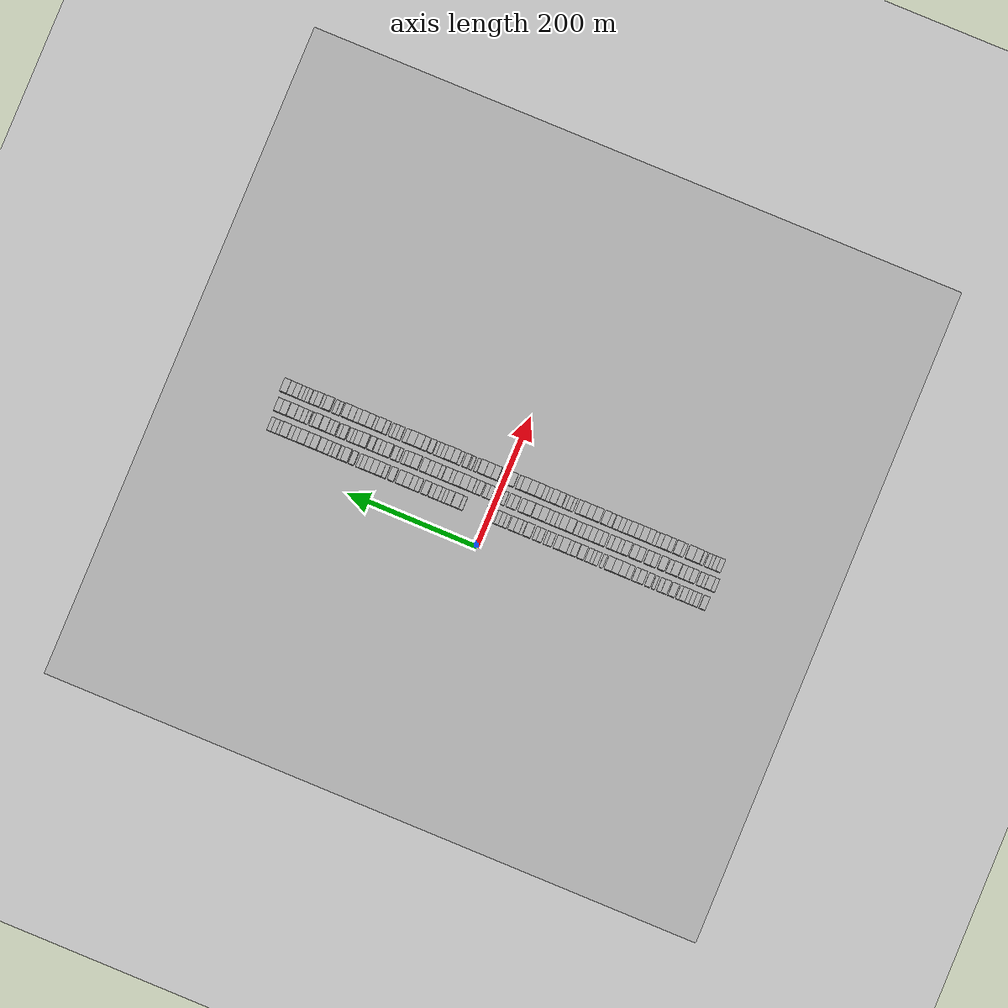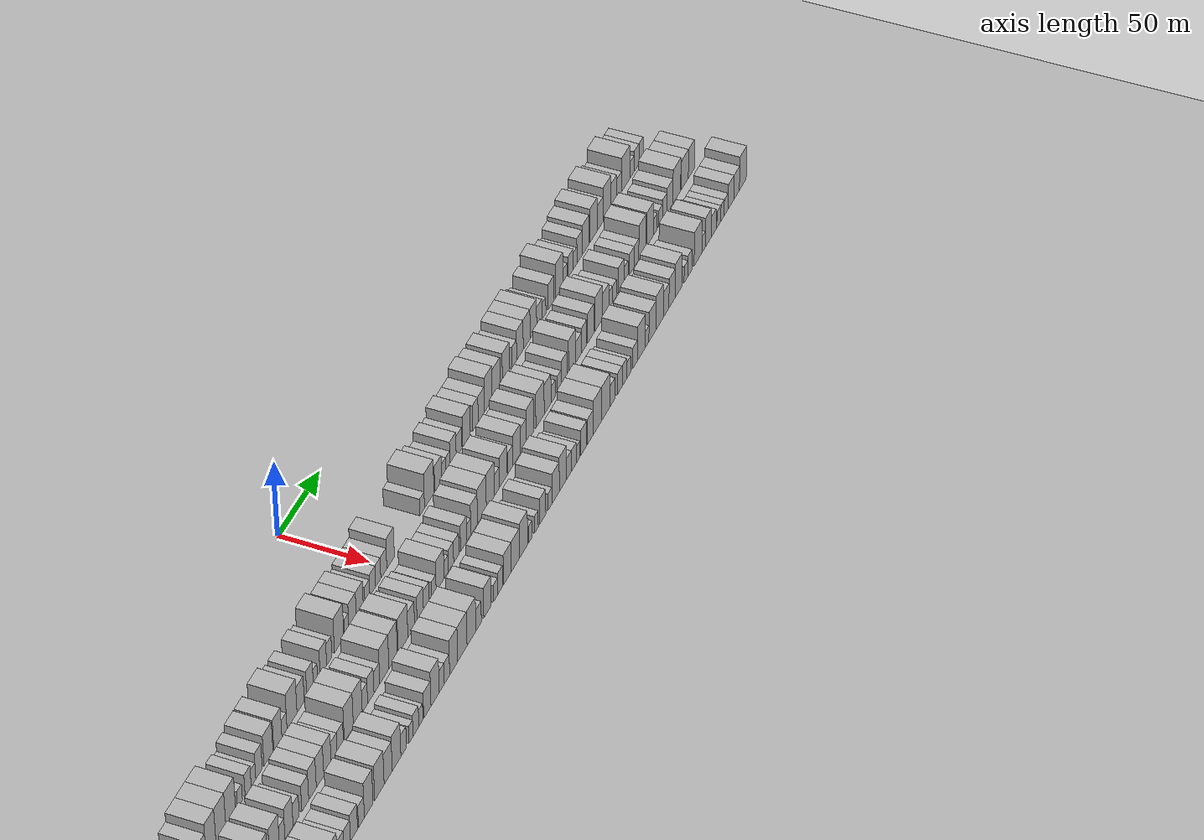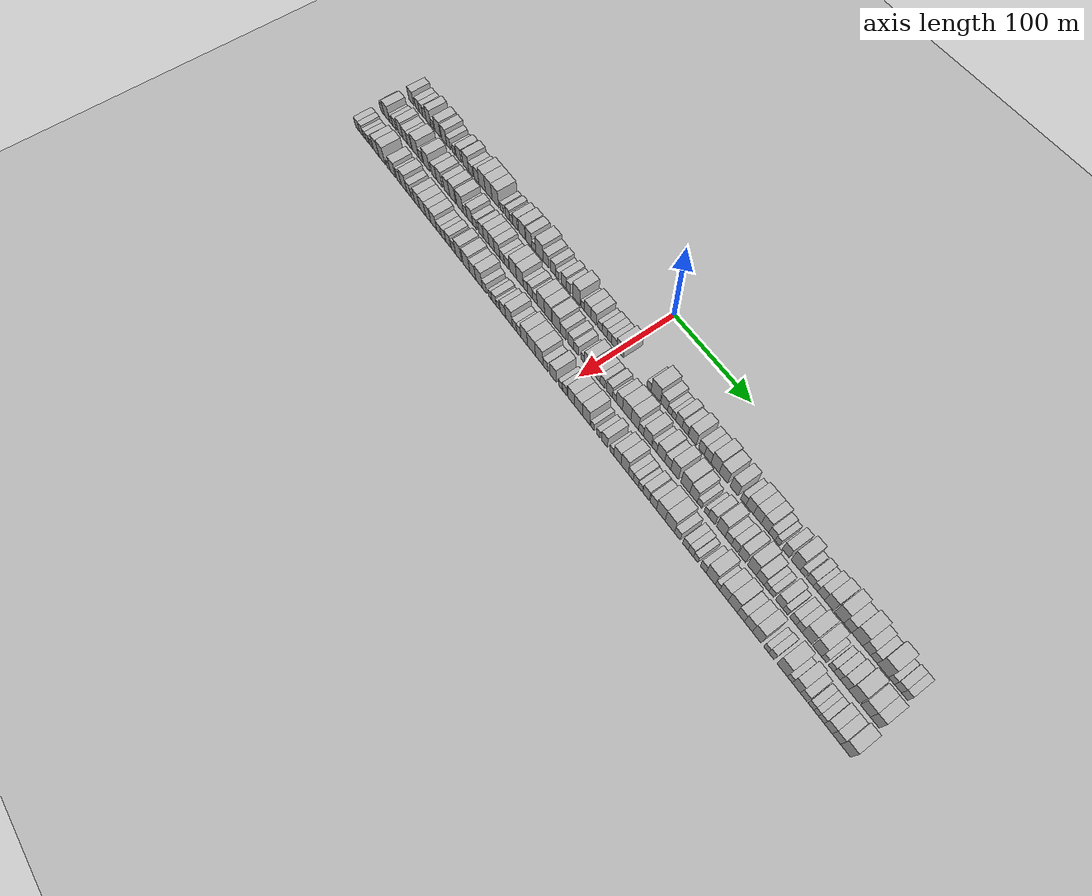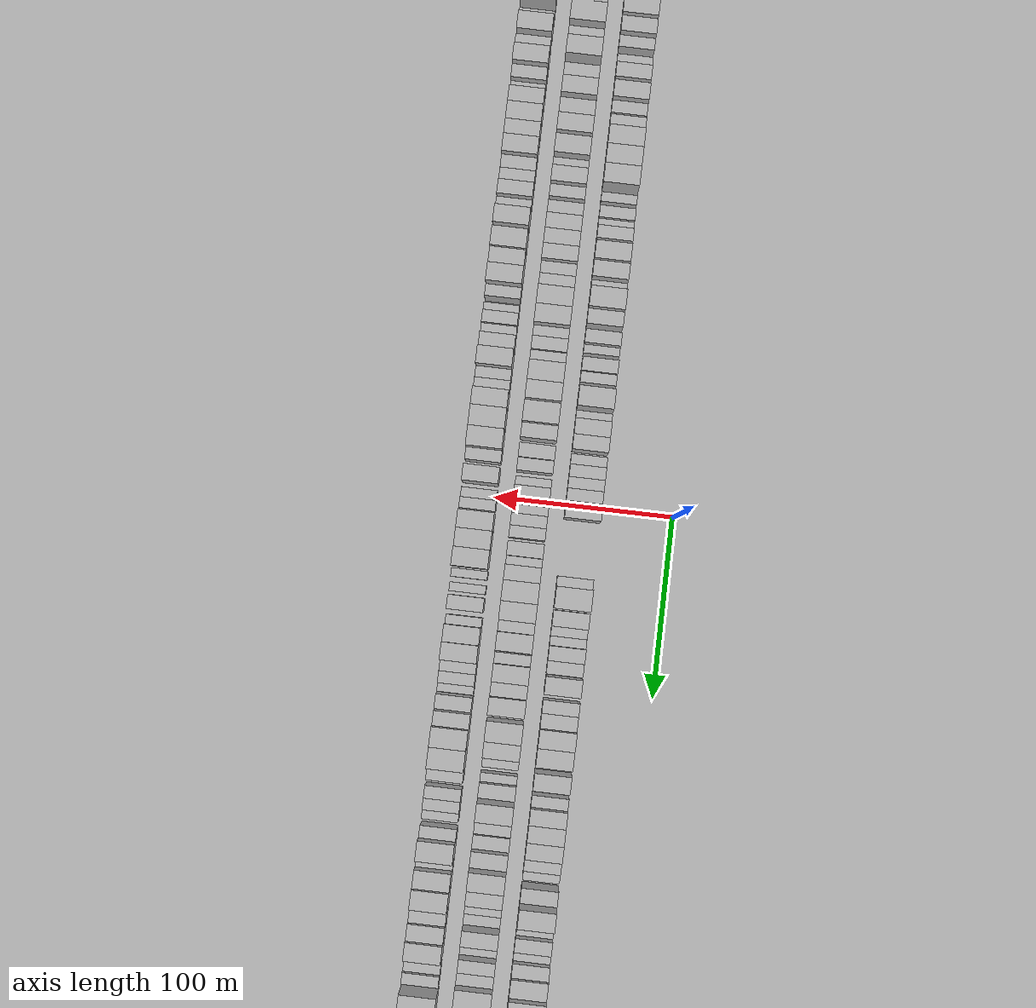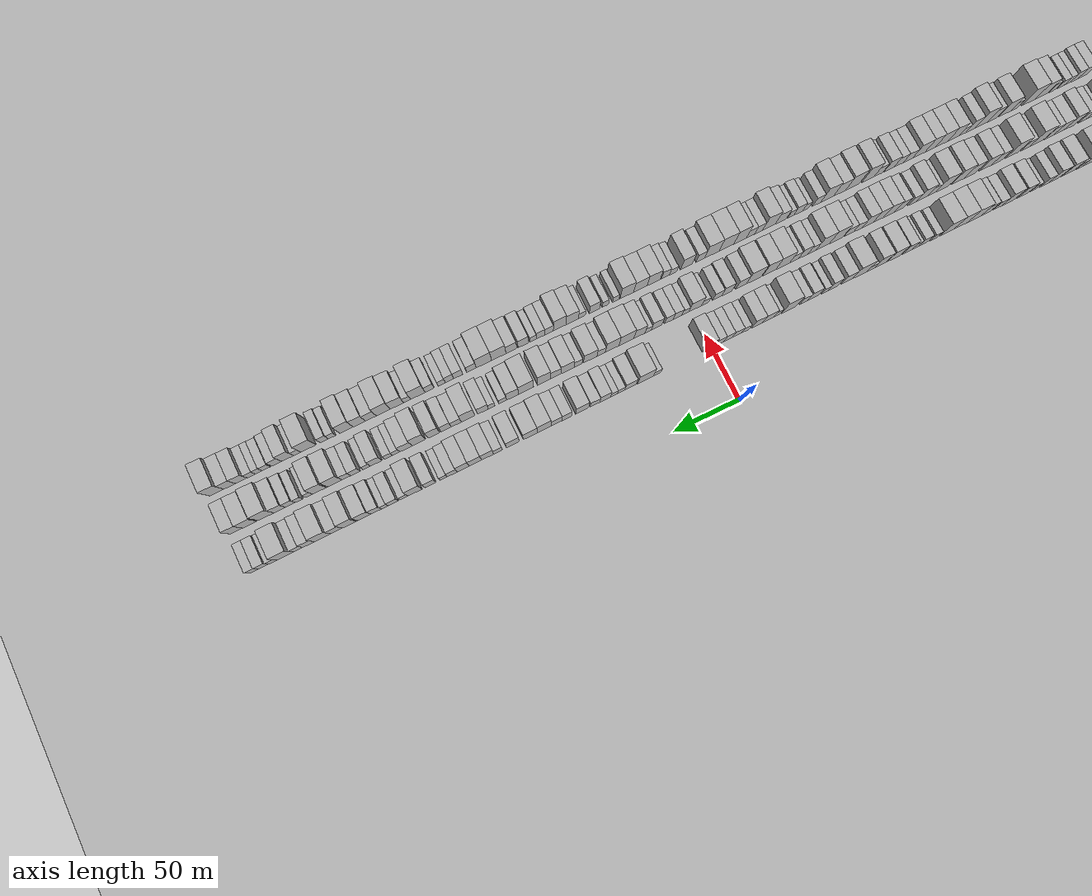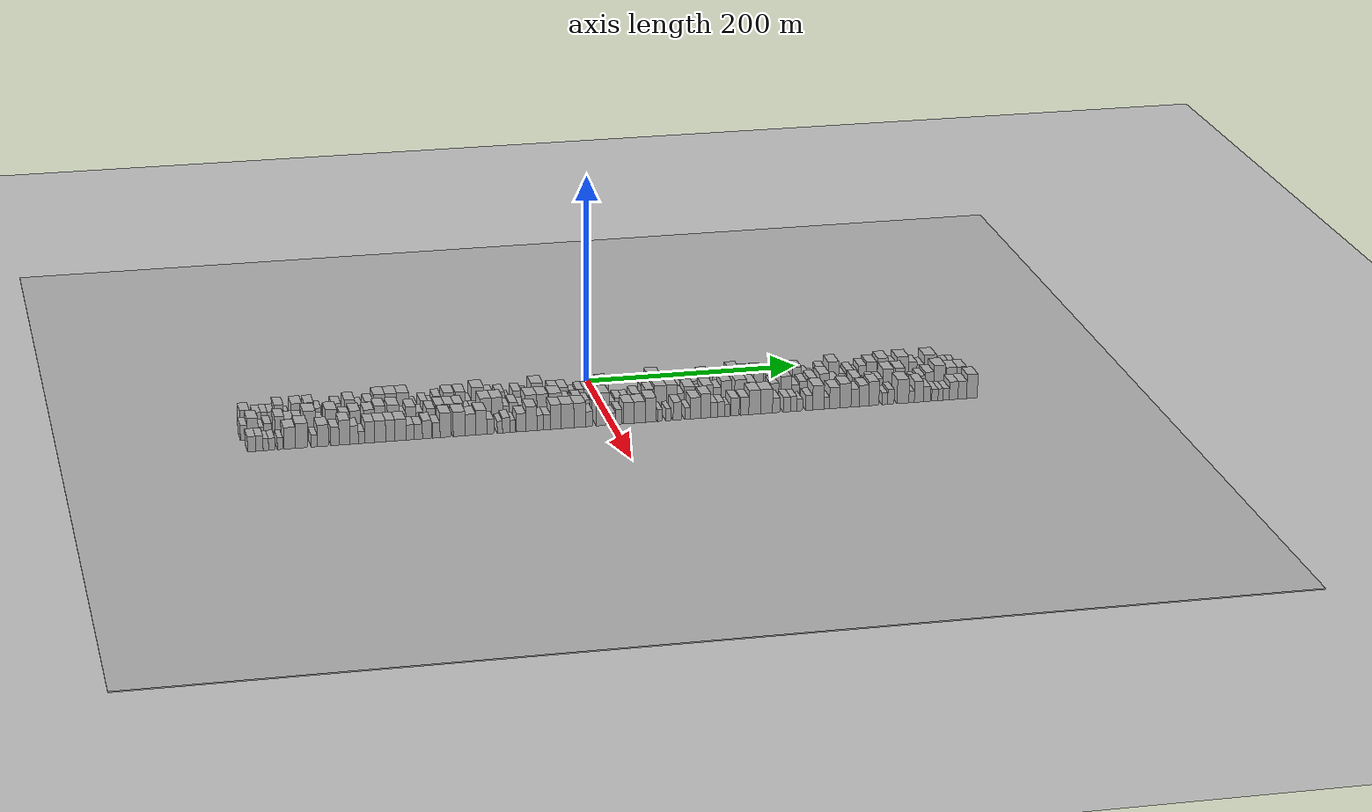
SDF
<?xml version="1.0" encoding="utf-8"?>

<sdf version="1.6">

   <world name="default">

      <gui fullscreen="0">

         <camera name="user_camera">

            <pose>-15 0 4.57585 0 0 0</pose>

            <view_controller>orbit</view_controller>

         </camera>

      </gui>

      <scene>

         <sky>

           <clouds>

             <speed>12</speed>

           </clouds>

         </sky>

         <ambient>0.4 0.4 0.4 1</ambient>

         <background>0.7 0.7 0.7 1</background>

         <shadows>1</shadows>

      </scene>

      <gravity>0 0 -9.8066</gravity>

      <magnetic_field>6e-06 2.3e-05 -4.2e-05</magnetic_field>

      <physics default="0" name="default_physics" type="ode">

         <ode>

            <solver>

               <type>quick</type>

               <iters>10</iters>

               <sor>1.0</sor>

               <use_dynamic_moi_rescaling>0</use_dynamic_moi_rescaling>

            </solver>

            <constraints>

               <cfm>0</cfm>

               <erp>0.2</erp>

               <contact_max_correcting_vel>100</contact_max_correcting_vel>

               <contact_surface_layer>0.001</contact_surface_layer>

            </constraints>

         </ode>

         <max_step_size>0.004</max_step_size>

         <real_time_factor>1</real_time_factor>

         <real_time_update_rate>250</real_time_update_rate>

      </physics>

      <light name="sun" type="directional">

         <cast_shadows>1</cast_shadows>

         <pose>0 0 10 0 0 0</pose>

         <diffuse>0.8 0.8 0.8 1</diffuse>

         <specular>0.2 0.2 0.2 1</specular>

         <attenuation>

            <range>1000</range>

            <constant>0.9</constant>

            <linear>0.01</linear>

            <quadratic>0.001</quadratic>

         </attenuation>

         <direction>-0.5 0.1 -0.9</direction>

      </light>

      <include>

         <name>ground_plane_1</name>

         <uri>model://HANNAS_ground_plane</uri>

         <pose>0 0 0  0 0 0</pose>

      </include>

      <include>

         <name>ground_plane_2</name>

         <uri>model://HANNAS_ground_plane</uri>

         <pose>100 0 0  0 0 0</pose>

      </include>

      <model name="building_1">

         <static>1</static>

         <pose frame="">50.0000 -328.5057 0 0.000000 0.000000 0.000000</pose>

         <link name="link">

            <pose frame="">0 0 9.00 0 0 0</pose>

            <collision name="collision">

               <geometry>

                  <box>

                     <size>20.0000 8.9886 18.0000</size>

                  </box>

               </geometry>

               <max_contacts>10</max_contacts>

               <surface>

                  <contact>

                     <ode/>

                  </contact>

                  <bounce/>

                  <friction>

                     <torsional>

                        <ode/>

                     </torsional>

                     <ode/>

                  </friction>

               </surface>

            </collision>

            <visual name="visual">

               <cast_shadows>0</cast_shadows>

               <geometry>

                  <box>

                     <size>20.0000 8.9886 18.0000</size>

                  </box>

               </geometry>

               <material>

                  <script>

                     <uri>model://HANNAS_wall/materials/scripts</uri>

                     <uri>model://HANNAS_wall/materials/textures</uri>

                     <name>vrc/HANNAS_wall</name>

                  </script>

               </material>

            </visual>

            <self_collide>0</self_collide>

            <enable_wind>0</enable_wind>

            <kinematic>0</kinematic>

         </link>

      </model>

      <model name="building_2">

         <static>1</static>

         <pose frame="">50.0000 -317.4604 0 0.000000 0.000000 0.000000</pose>

         <link name="link">

            <pose frame="">0 0 7.50 0 0 0</pose>

            <collision name="collision">

               <geometry>

                  <box>

                     <size>20.0000 7.1020 15.0000</size>

                  </box>

               </geometry>

               <max_contacts>10</max_contacts>

               <surface>

                  <contact>

                     <ode/>

                  </contact>

                  <bounce/>

                  <friction>

                     <torsional>

                        <ode/>

                     </torsional>

                     <ode/>

                  </friction>

               </surface>

            </collision>

            <visual name="visual">

               <cast_shadows>0</cast_shadows>

               <geometry>

                  <box>

                     <size>20.0000 7.1020 15.0000</size>

                  </box>

               </geometry>

               <material>

                  <script>

                     <uri>model://HANNAS_wall/materials/scripts</uri>

                     <uri>model://HANNAS_wall/materials/textures</uri>

                     <name>vrc/HANNAS_wall</name>

                  </script>

               </material>

            </visual>

            <self_collide>0</self_collide>

            <enable_wind>0</enable_wind>

            <kinematic>0</kinematic>

         </link>

      </model>

      <model name="building_3">

         <static>1</static>

         <pose frame="">50.0000 -310.8378 0 0.000000 0.000000 0.000000</pose>

         <link name="link">

            <pose frame="">0 0 7.50 0 0 0</pose>

            <collision name="collision">

               <geometry>

                  <box>

                     <size>20.0000 6.1432 15.0000</size>

                  </box>

               </geometry>

               <max_contacts>10</max_contacts>

               <surface>

                  <contact>

                     <ode/>

                  </contact>

                  <bounce/>

                  <friction>

                     <torsional>

                        <ode/>

                     </torsional>

                     <ode/>

                  </friction>

               </surface>

            </collision>

            <visual name="visual">

               <cast_shadows>0</cast_shadows>

               <geometry>

                  <box>

                     <size>20.0000 6.1432 15.0000</size>

                  </box>

               </geometry>

               <material>

                  <script>

                     <uri>model://HANNAS_wall/materials/scripts</uri>

                     <uri>model://HANNAS_wall/materials/textures</uri>

                     <name>vrc/HANNAS_wall</name>

                  </script>

               </material>

            </visual>

            <self_collide>0</self_collide>

            <enable_wind>0</enable_wind>

            <kinematic>0</kinematic>

         </link>

      </model>

      <model name="building_4">

         <static>1</static>

         <pose frame="">50.0000 -304.7060 0 0.000000 0.000000 0.000000</pose>

         <link name="link">

            <pose frame="">0 0 7.50 0 0 0</pose>

            <collision name="collision">

               <geometry>

                  <box>

                     <size>20.0000 6.1204 15.0000</size>

                  </box>

               </geometry>

               <max_contacts>10</max_contacts>

               <surface>

                  <contact>

                     <ode/>

                  </contact>

                  <bounce/>

                  <friction>

                     <torsional>

                        <ode/>

                     </torsional>

                     <ode/>

                  </friction>

               </surface>

            </collision>

            <visual name="visual">

               <cast_shadows>0</cast_shadows>

               <geometry>

                  <box>

                     <size>20.0000 6.1204 15.0000</size>

                  </box>

               </geometry>

               <material>

                  <script>

                     <uri>model://HANNAS_wall/materials/scripts</uri>

                     <uri>model://HANNAS_wall/materials/textures</uri>

                     <name>vrc/HANNAS_wall</name>

                  </script>

               </material>

            </visual>

            <self_collide>0</self_collide>

            <enable_wind>0</enable_wind>

            <kinematic>0</kinematic>

         </link>

      </model>

      <model name="building_5">

         <static>1</static>

         <pose frame="">50.0000 -297.3492 0 0.000000 0.000000 0.000000</pose>

         <link name="link">

            <pose frame="">0 0 10.50 0 0 0</pose>

            <collision name="collision">

               <geometry>

                  <box>

                     <size>20.0000 8.5932 21.0000</size>

                  </box>

               </geometry>

               <max_contacts>10</max_contacts>

               <surface>

                  <contact>

                     <ode/>

                  </contact>

                  <bounce/>

                  <friction>

                     <torsional>

                        <ode/>

                     </torsional>

                     <ode/>

                  </friction>

               </surface>

            </collision>

            <visual name="visual">

               <cast_shadows>0</cast_shadows>

               <geometry>

                  <box>

                     <size>20.0000 8.5932 21.0000</size>

                  </box>

               </geometry>

               <material>

                  <script>

                     <uri>model://HANNAS_wall/materials/scripts</uri>

                     <uri>model://HANNAS_wall/materials/textures</uri>

                     <name>vrc/HANNAS_wall</name>

                  </script>

               </material>

            </visual>

            <self_collide>0</self_collide>

            <enable_wind>0</enable_wind>

            <kinematic>0</kinematic>

         </link>

      </model>

      <model name="building_6">

         <static>1</static>

         <pose frame="">50.0000 -290.5450 0 0.000000 0.000000 0.000000</pose>

         <link name="link">

            <pose frame="">0 0 6.00 0 0 0</pose>

            <collision name="collision">

               <geometry>

                  <box>

                     <size>20.0000 5.0150 12.0000</size>

                  </box>

               </geometry>

               <max_contacts>10</max_contacts>

               <surface>

                  <contact>

                     <ode/>

                  </contact>

                  <bounce/>

                  <friction>

                     <torsional>

                        <ode/>

                     </torsional>

                     <ode/>

                  </friction>

               </surface>

            </collision>

            <visual name="visual">

               <cast_shadows>0</cast_shadows>

               <geometry>

                  <box>

                     <size>20.0000 5.0150 12.0000</size>

                  </box>

               </geometry>

               <material>

                  <script>

                     <uri>model://HANNAS_wall/materials/scripts</uri>

                     <uri>model://HANNAS_wall/materials/textures</uri>

                     <name>vrc/HANNAS_wall</name>

                  </script>

               </material>

            </visual>

            <self_collide>0</self_collide>

            <enable_wind>0</enable_wind>

            <kinematic>0</kinematic>

         </link>

      </model>

      <model name="building_7">

         <static>1</static>

         <pose frame="">50.0000 -281.1104 0 0.000000 0.000000 0.000000</pose>

         <link name="link">

            <pose frame="">0 0 10.50 0 0 0</pose>

            <collision name="collision">

               <geometry>

                  <box>

                     <size>20.0000 9.8542 21.0000</size>

                  </box>

               </geometry>

               <max_contacts>10</max_contacts>

               <surface>

                  <contact>

                     <ode/>

                  </contact>

                  <bounce/>

                  <friction>

                     <torsional>

                        <ode/>

                     </torsional>

                     <ode/>

                  </friction>

               </surface>

            </collision>

            <visual name="visual">

               <cast_shadows>0</cast_shadows>

               <geometry>

                  <box>

                     <size>20.0000 9.8542 21.0000</size>

                  </box>

               </geometry>

               <material>

                  <script>

                     <uri>model://HANNAS_wall/materials/scripts</uri>

                     <uri>model://HANNAS_wall/materials/textures</uri>

                     <name>vrc/HANNAS_wall</name>

                  </script>

               </material>

            </visual>

            <self_collide>0</self_collide>

            <enable_wind>0</enable_wind>

            <kinematic>0</kinematic>

         </link>

      </model>

      <model name="building_8">

         <static>1</static>

         <pose frame="">50.0000 -269.7870 0 0.000000 0.000000 0.000000</pose>

         <link name="link">

            <pose frame="">0 0 10.50 0 0 0</pose>

            <collision name="collision">

               <geometry>

                  <box>

                     <size>20.0000 8.7926 21.0000</size>

                  </box>

               </geometry>

               <max_contacts>10</max_contacts>

               <surface>

                  <contact>

                     <ode/>

                  </contact>

                  <bounce/>

                  <friction>

                     <torsional>

                        <ode/>

                     </torsional>

                     <ode/>

                  </friction>

               </surface>

            </collision>

            <visual name="visual">

               <cast_shadows>0</cast_shadows>

               <geometry>

                  <box>

                     <size>20.0000 8.7926 21.0000</size>

                  </box>

               </geometry>

               <material>

                  <script>

                     <uri>model://HANNAS_wall/materials/scripts</uri>

                     <uri>model://HANNAS_wall/materials/textures</uri>

                     <name>vrc/HANNAS_wall</name>

                  </script>

               </material>

            </visual>

            <self_collide>0</self_collide>

            <enable_wind>0</enable_wind>

            <kinematic>0</kinematic>

         </link>

      </model>

      <model name="building_9">

         <static>1</static>

         <pose frame="">50.0000 -262.0420 0 0.000000 0.000000 0.000000</pose>

         <link name="link">

            <pose frame="">0 0 7.50 0 0 0</pose>

            <collision name="collision">

               <geometry>

                  <box>

                     <size>20.0000 6.6973 15.0000</size>

                  </box>

               </geometry>

               <max_contacts>10</max_contacts>

               <surface>

                  <contact>

                     <ode/>

                  </contact>

                  <bounce/>

                  <friction>

                     <torsional>

                        <ode/>

                     </torsional>

                     <ode/>

                  </friction>

               </surface>

            </collision>

            <visual name="visual">

               <cast_shadows>0</cast_shadows>

               <geometry>

                  <box>

                     <size>20.0000 6.6973 15.0000</size>

                  </box>

               </geometry>

               <material>

                  <script>

                     <uri>model://HANNAS_wall/materials/scripts</uri>

                     <uri>model://HANNAS_wall/materials/textures</uri>

                     <name>vrc/HANNAS_wall</name>

                  </script>

               </material>

            </visual>

            <self_collide>0</self_collide>

            <enable_wind>0</enable_wind>

            <kinematic>0</kinematic>

         </link>

      </model>

      <model name="building_10">

         <static>1</static>

         <pose frame="">50.0000 -253.2328 0 0.000000 0.000000 0.000000</pose>

         <link name="link">

            <pose frame="">0 0 6.00 0 0 0</pose>

            <collision name="collision">

               <geometry>

                  <box>

                     <size>20.0000 4.9211 12.0000</size>

                  </box>

               </geometry>

               <max_contacts>10</max_contacts>

               <surface>

                  <contact>

                     <ode/>

                  </contact>

                  <bounce/>

                  <friction>

                     <torsional>

                        <ode/>

                     </torsional>

                     <ode/>

                  </friction>

               </surface>

            </collision>

            <visual name="visual">

               <cast_shadows>0</cast_shadows>

               <geometry>

                  <box>

                     <size>20.0000 4.9211 12.0000</size>

                  </box>

               </geometry>

               <material>

                  <script>

                     <uri>model://HANNAS_wall/materials/scripts</uri>

                     <uri>model://HANNAS_wall/materials/textures</uri>

                     <name>vrc/HANNAS_wall</name>

                  </script>

               </material>

            </visual>

            <self_collide>0</self_collide>

            <enable_wind>0</enable_wind>

            <kinematic>0</kinematic>

         </link>

      </model>

      <model name="building_11">

         <static>1</static>

         <pose frame="">50.0000 -244.5584 0 0.000000 0.000000 0.000000</pose>

         <link name="link">

            <pose frame="">0 0 9.00 0 0 0</pose>

            <collision name="collision">

               <geometry>

                  <box>

                     <size>20.0000 8.4279 18.0000</size>

                  </box>

               </geometry>

               <max_contacts>10</max_contacts>

               <surface>

                  <contact>

                     <ode/>

                  </contact>

                  <bounce/>

                  <friction>

                     <torsional>

                        <ode/>

                     </torsional>

                     <ode/>

                  </friction>

               </surface>

            </collision>

            <visual name="visual">

               <cast_shadows>0</cast_shadows>

               <geometry>

                  <box>

                     <size>20.0000 8.4279 18.0000</size>

                  </box>

               </geometry>

               <material>

                  <script>

                     <uri>model://HANNAS_wall/materials/scripts</uri>

                     <uri>model://HANNAS_wall/materials/textures</uri>

                     <name>vrc/HANNAS_wall</name>

                  </script>

               </material>

            </visual>

            <self_collide>0</self_collide>

            <enable_wind>0</enable_wind>

            <kinematic>0</kinematic>

         </link>

      </model>

      <model name="building_12">

         <static>1</static>

         <pose frame="">50.0000 -232.5456 0 0.000000 0.000000 0.000000</pose>

         <link name="link">

            <pose frame="">0 0 10.50 0 0 0</pose>

            <collision name="collision">

               <geometry>

                  <box>

                     <size>20.0000 9.5977 21.0000</size>

                  </box>

               </geometry>

               <max_contacts>10</max_contacts>

               <surface>

                  <contact>

                     <ode/>

                  </contact>

                  <bounce/>

                  <friction>

                     <torsional>

                        <ode/>

                     </torsional>

                     <ode/>

                  </friction>

               </surface>

            </collision>

            <visual name="visual">

               <cast_shadows>0</cast_shadows>

               <geometry>

                  <box>

                     <size>20.0000 9.5977 21.0000</size>

                  </box>

               </geometry>

               <material>

                  <script>

                     <uri>model://HANNAS_wall/materials/scripts</uri>

                     <uri>model://HANNAS_wall/materials/textures</uri>

                     <name>vrc/HANNAS_wall</name>

                  </script>

               </material>

            </visual>

            <self_collide>0</self_collide>

            <enable_wind>0</enable_wind>

            <kinematic>0</kinematic>

         </link>

      </model>

      <model name="building_13">

         <static>1</static>

         <pose frame="">50.0000 -224.1726 0 0.000000 0.000000 0.000000</pose>

         <link name="link">

            <pose frame="">0 0 7.50 0 0 0</pose>

            <collision name="collision">

               <geometry>

                  <box>

                     <size>20.0000 7.1484 15.0000</size>

                  </box>

               </geometry>

               <max_contacts>10</max_contacts>

               <surface>

                  <contact>

                     <ode/>

                  </contact>

                  <bounce/>

                  <friction>

                     <torsional>

                        <ode/>

                     </torsional>

                     <ode/>

                  </friction>

               </surface>

            </collision>

            <visual name="visual">

               <cast_shadows>0</cast_shadows>

               <geometry>

                  <box>

                     <size>20.0000 7.1484 15.0000</size>

                  </box>

               </geometry>

               <material>

                  <script>

                     <uri>model://HANNAS_wall/materials/scripts</uri>

                     <uri>model://HANNAS_wall/materials/textures</uri>

                     <name>vrc/HANNAS_wall</name>

                  </script>

               </material>

            </visual>

            <self_collide>0</self_collide>

            <enable_wind>0</enable_wind>

            <kinematic>0</kinematic>

         </link>

      </model>

      <model name="building_14">

         <static>1</static>

         <pose frame="">50.0000 -214.6508 0 0.000000 0.000000 0.000000</pose>

         <link name="link">

            <pose frame="">0 0 9.00 0 0 0</pose>

            <collision name="collision">

               <geometry>

                  <box>

                     <size>20.0000 7.8951 18.0000</size>

                  </box>

               </geometry>

               <max_contacts>10</max_contacts>

               <surface>

                  <contact>

                     <ode/>

                  </contact>

                  <bounce/>

                  <friction>

                     <torsional>

                        <ode/>

                     </torsional>

                     <ode/>

                  </friction>

               </surface>

            </collision>

            <visual name="visual">

               <cast_shadows>0</cast_shadows>

               <geometry>

                  <box>

                     <size>20.0000 7.8951 18.0000</size>

                  </box>

               </geometry>

               <material>

                  <script>

                     <uri>model://HANNAS_wall/materials/scripts</uri>

                     <uri>model://HANNAS_wall/materials/textures</uri>

                     <name>vrc/HANNAS_wall</name>

                  </script>

               </material>

            </visual>

            <self_collide>0</self_collide>

            <enable_wind>0</enable_wind>

            <kinematic>0</kinematic>

         </link>

      </model>

      <model name="building_15">

         <static>1</static>

         <pose frame="">50.0000 -205.3336 0 0.000000 0.000000 0.000000</pose>

         <link name="link">

            <pose frame="">0 0 12.00 0 0 0</pose>

            <collision name="collision">

               <geometry>

                  <box>

                     <size>20.0000 10.7393 24.0000</size>

                  </box>

               </geometry>

               <max_contacts>10</max_contacts>

               <surface>

                  <contact>

                     <ode/>

                  </contact>

                  <bounce/>

                  <friction>

                     <torsional>

                        <ode/>

                     </torsional>

                     <ode/>

                  </friction>

               </surface>

            </collision>

            <visual name="visual">

               <cast_shadows>0</cast_shadows>

               <geometry>

                  <box>

                     <size>20.0000 10.7393 24.0000</size>

                  </box>

               </geometry>

               <material>

                  <script>

                     <uri>model://HANNAS_wall/materials/scripts</uri>

                     <uri>model://HANNAS_wall/materials/textures</uri>

                     <name>vrc/HANNAS_wall</name>

                  </script>

               </material>

            </visual>

            <self_collide>0</self_collide>

            <enable_wind>0</enable_wind>

            <kinematic>0</kinematic>

         </link>

      </model>

      <model name="building_16">

         <static>1</static>

         <pose frame="">50.0000 -194.4689 0 0.000000 0.000000 0.000000</pose>

         <link name="link">

            <pose frame="">0 0 12.00 0 0 0</pose>

            <collision name="collision">

               <geometry>

                  <box>

                     <size>20.0000 10.9901 24.0000</size>

                  </box>

               </geometry>

               <max_contacts>10</max_contacts>

               <surface>

                  <contact>

                     <ode/>

                  </contact>

                  <bounce/>

                  <friction>

                     <torsional>

                        <ode/>

                     </torsional>

                     <ode/>

                  </friction>

               </surface>

            </collision>

            <visual name="visual">

               <cast_shadows>0</cast_shadows>

               <geometry>

                  <box>

                     <size>20.0000 10.9901 24.0000</size>

                  </box>

               </geometry>

               <material>

                  <script>

                     <uri>model://HANNAS_wall/materials/scripts</uri>

                     <uri>model://HANNAS_wall/materials/textures</uri>

                     <name>vrc/HANNAS_wall</name>

                  </script>

               </material>

            </visual>

            <self_collide>0</self_collide>

            <enable_wind>0</enable_wind>

            <kinematic>0</kinematic>

         </link>

      </model>

      <model name="building_17">

         <static>1</static>

         <pose frame="">50.0000 -183.5001 0 0.000000 0.000000 0.000000</pose>

         <link name="link">

            <pose frame="">0 0 12.00 0 0 0</pose>

            <collision name="collision">

               <geometry>

                  <box>

                     <size>20.0000 10.9474 24.0000</size>

                  </box>

               </geometry>

               <max_contacts>10</max_contacts>

               <surface>

                  <contact>

                     <ode/>

                  </contact>

                  <bounce/>

                  <friction>

                     <torsional>

                        <ode/>

                     </torsional>

                     <ode/>

                  </friction>

               </surface>

            </collision>

            <visual name="visual">

               <cast_shadows>0</cast_shadows>

               <geometry>

                  <box>

                     <size>20.0000 10.9474 24.0000</size>

                  </box>

               </geometry>

               <material>

                  <script>

                     <uri>model://HANNAS_wall/materials/scripts</uri>

                     <uri>model://HANNAS_wall/materials/textures</uri>

                     <name>vrc/HANNAS_wall</name>

                  </script>

               </material>

            </visual>

            <self_collide>0</self_collide>

            <enable_wind>0</enable_wind>

            <kinematic>0</kinematic>

         </link>

      </model>

      <model name="building_18">

         <static>1</static>

         <pose frame="">50.0000 -173.3073 0 0.000000 0.000000 0.000000</pose>

         <link name="link">

            <pose frame="">0 0 6.00 0 0 0</pose>

            <collision name="collision">

               <geometry>

                  <box>

                     <size>20.0000 5.4383 12.0000</size>

                  </box>

               </geometry>

               <max_contacts>10</max_contacts>

               <surface>

                  <contact>

                     <ode/>

                  </contact>

                  <bounce/>

                  <friction>

                     <torsional>

                        <ode/>

                     </torsional>

                     <ode/>

                  </friction>

               </surface>

            </collision>

            <visual name="visual">

               <cast_shadows>0</cast_shadows>

               <geometry>

                  <box>

                     <size>20.0000 5.4383 12.0000</size>

                  </box>

               </geometry>

               <material>

                  <script>

                     <uri>model://HANNAS_wall/materials/scripts</uri>

                     <uri>model://HANNAS_wall/materials/textures</uri>

                     <name>vrc/HANNAS_wall</name>

                  </script>

               </material>

            </visual>

            <self_collide>0</self_collide>

            <enable_wind>0</enable_wind>

            <kinematic>0</kinematic>

         </link>

      </model>

      <model name="building_19">

         <static>1</static>

         <pose frame="">50.0000 -164.1934 0 0.000000 0.000000 0.000000</pose>

         <link name="link">

            <pose frame="">0 0 7.50 0 0 0</pose>

            <collision name="collision">

               <geometry>

                  <box>

                     <size>20.0000 6.7896 15.0000</size>

                  </box>

               </geometry>

               <max_contacts>10</max_contacts>

               <surface>

                  <contact>

                     <ode/>

                  </contact>

                  <bounce/>

                  <friction>

                     <torsional>

                        <ode/>

                     </torsional>

                     <ode/>

                  </friction>

               </surface>

            </collision>

            <visual name="visual">

               <cast_shadows>0</cast_shadows>

               <geometry>

                  <box>

                     <size>20.0000 6.7896 15.0000</size>

                  </box>

               </geometry>

               <material>

                  <script>

                     <uri>model://HANNAS_wall/materials/scripts</uri>

                     <uri>model://HANNAS_wall/materials/textures</uri>

                     <name>vrc/HANNAS_wall</name>

                  </script>

               </material>

            </visual>

            <self_collide>0</self_collide>

            <enable_wind>0</enable_wind>

            <kinematic>0</kinematic>

         </link>

      </model>

      <model name="building_20">

         <static>1</static>

         <pose frame="">50.0000 -158.1950 0 0.000000 0.000000 0.000000</pose>

         <link name="link">

            <pose frame="">0 0 6.00 0 0 0</pose>

            <collision name="collision">

               <geometry>

                  <box>

                     <size>20.0000 5.2070 12.0000</size>

                  </box>

               </geometry>

               <max_contacts>10</max_contacts>

               <surface>

                  <contact>

                     <ode/>

                  </contact>

                  <bounce/>

                  <friction>

                     <torsional>

                        <ode/>

                     </torsional>

                     <ode/>

                  </friction>

               </surface>

            </collision>

            <visual name="visual">

               <cast_shadows>0</cast_shadows>

               <geometry>

                  <box>

                     <size>20.0000 5.2070 12.0000</size>

                  </box>

               </geometry>

               <material>

                  <script>

                     <uri>model://HANNAS_wall/materials/scripts</uri>

                     <uri>model://HANNAS_wall/materials/textures</uri>

                     <name>vrc/HANNAS_wall</name>

                  </script>

               </material>

            </visual>

            <self_collide>0</self_collide>

            <enable_wind>0</enable_wind>

            <kinematic>0</kinematic>

         </link>

      </model>

      <model name="building_21">

         <static>1</static>

         <pose frame="">50.0000 -151.9357 0 0.000000 0.000000 0.000000</pose>

         <link name="link">

            <pose frame="">0 0 9.00 0 0 0</pose>

            <collision name="collision">

               <geometry>

                  <box>

                     <size>20.0000 7.3116 18.0000</size>

                  </box>

               </geometry>

               <max_contacts>10</max_contacts>

               <surface>

                  <contact>

                     <ode/>

                  </contact>

                  <bounce/>

                  <friction>

                     <torsional>

                        <ode/>

                     </torsional>

                     <ode/>

                  </friction>

               </surface>

            </collision>

            <visual name="visual">

               <cast_shadows>0</cast_shadows>

               <geometry>

                  <box>

                     <size>20.0000 7.3116 18.0000</size>

                  </box>

               </geometry>

               <material>

                  <script>

                     <uri>model://HANNAS_wall/materials/scripts</uri>

                     <uri>model://HANNAS_wall/materials/textures</uri>

                     <name>vrc/HANNAS_wall</name>

                  </script>

               </material>

            </visual>

            <self_collide>0</self_collide>

            <enable_wind>0</enable_wind>

            <kinematic>0</kinematic>

         </link>

      </model>

      <model name="building_22">

         <static>1</static>

         <pose frame="">50.0000 -141.1871 0 0.000000 0.000000 0.000000</pose>

         <link name="link">

            <pose frame="">0 0 10.50 0 0 0</pose>

            <collision name="collision">

               <geometry>

                  <box>

                     <size>20.0000 10.1855 21.0000</size>

                  </box>

               </geometry>

               <max_contacts>10</max_contacts>

               <surface>

                  <contact>

                     <ode/>

                  </contact>

                  <bounce/>

                  <friction>

                     <torsional>

                        <ode/>

                     </torsional>

                     <ode/>

                  </friction>

               </surface>

            </collision>

            <visual name="visual">

               <cast_shadows>0</cast_shadows>

               <geometry>

                  <box>

                     <size>20.0000 10.1855 21.0000</size>

                  </box>

               </geometry>

               <material>

                  <script>

                     <uri>model://HANNAS_wall/materials/scripts</uri>

                     <uri>model://HANNAS_wall/materials/textures</uri>

                     <name>vrc/HANNAS_wall</name>

                  </script>

               </material>

            </visual>

            <self_collide>0</self_collide>

            <enable_wind>0</enable_wind>

            <kinematic>0</kinematic>

         </link>

      </model>

      <model name="building_23">

         <static>1</static>

         <pose frame="">50.0000 -130.5088 0 0.000000 0.000000 0.000000</pose>

         <link name="link">

            <pose frame="">0 0 10.50 0 0 0</pose>

            <collision name="collision">

               <geometry>

                  <box>

                     <size>20.0000 9.1711 21.0000</size>

                  </box>

               </geometry>

               <max_contacts>10</max_contacts>

               <surface>

                  <contact>

                     <ode/>

                  </contact>

                  <bounce/>

                  <friction>

                     <torsional>

                        <ode/>

                     </torsional>

                     <ode/>

                  </friction>

               </surface>

            </collision>

            <visual name="visual">

               <cast_shadows>0</cast_shadows>

               <geometry>

                  <box>

                     <size>20.0000 9.1711 21.0000</size>

                  </box>

               </geometry>

               <material>

                  <script>

                     <uri>model://HANNAS_wall/materials/scripts</uri>

                     <uri>model://HANNAS_wall/materials/textures</uri>

                     <name>vrc/HANNAS_wall</name>

                  </script>

               </material>

            </visual>

            <self_collide>0</self_collide>

            <enable_wind>0</enable_wind>

            <kinematic>0</kinematic>

         </link>

      </model>

      <model name="building_24">

         <static>1</static>

         <pose frame="">50.0000 -122.9851 0 0.000000 0.000000 0.000000</pose>

         <link name="link">

            <pose frame="">0 0 6.00 0 0 0</pose>

            <collision name="collision">

               <geometry>

                  <box>

                     <size>20.0000 5.8763 12.0000</size>

                  </box>

               </geometry>

               <max_contacts>10</max_contacts>

               <surface>

                  <contact>

                     <ode/>

                  </contact>

                  <bounce/>

                  <friction>

                     <torsional>

                        <ode/>

                     </torsional>

                     <ode/>

                  </friction>

               </surface>

            </collision>

            <visual name="visual">

               <cast_shadows>0</cast_shadows>

               <geometry>

                  <box>

                     <size>20.0000 5.8763 12.0000</size>

                  </box>

               </geometry>

               <material>

                  <script>

                     <uri>model://HANNAS_wall/materials/scripts</uri>

                     <uri>model://HANNAS_wall/materials/textures</uri>

                     <name>vrc/HANNAS_wall</name>

                  </script>

               </material>

            </visual>

            <self_collide>0</self_collide>

            <enable_wind>0</enable_wind>

            <kinematic>0</kinematic>

         </link>

      </model>

      <model name="building_25">

         <static>1</static>

         <pose frame="">50.0000 -114.2810 0 0.000000 0.000000 0.000000</pose>

         <link name="link">

            <pose frame="">0 0 12.00 0 0 0</pose>

            <collision name="collision">

               <geometry>

                  <box>

                     <size>20.0000 11.5320 24.0000</size>

                  </box>

               </geometry>

               <max_contacts>10</max_contacts>

               <surface>

                  <contact>

                     <ode/>

                  </contact>

                  <bounce/>

                  <friction>

                     <torsional>

                        <ode/>

                     </torsional>

                     <ode/>

                  </friction>

               </surface>

            </collision>

            <visual name="visual">

               <cast_shadows>0</cast_shadows>

               <geometry>

                  <box>

                     <size>20.0000 11.5320 24.0000</size>

                  </box>

               </geometry>

               <material>

                  <script>

                     <uri>model://HANNAS_wall/materials/scripts</uri>

                     <uri>model://HANNAS_wall/materials/textures</uri>

                     <name>vrc/HANNAS_wall</name>

                  </script>

               </material>

            </visual>

            <self_collide>0</self_collide>

            <enable_wind>0</enable_wind>

            <kinematic>0</kinematic>

         </link>

      </model>

      <model name="building_26">

         <static>1</static>

         <pose frame="">50.0000 -104.2789 0 0.000000 0.000000 0.000000</pose>

         <link name="link">

            <pose frame="">0 0 9.00 0 0 0</pose>

            <collision name="collision">

               <geometry>

                  <box>

                     <size>20.0000 8.4722 18.0000</size>

                  </box>

               </geometry>

               <max_contacts>10</max_contacts>

               <surface>

                  <contact>

                     <ode/>

                  </contact>

                  <bounce/>

                  <friction>

                     <torsional>

                        <ode/>

                     </torsional>

                     <ode/>

                  </friction>

               </surface>

            </collision>

            <visual name="visual">

               <cast_shadows>0</cast_shadows>

               <geometry>

                  <box>

                     <size>20.0000 8.4722 18.0000</size>

                  </box>

               </geometry>

               <material>

                  <script>

                     <uri>model://HANNAS_wall/materials/scripts</uri>

                     <uri>model://HANNAS_wall/materials/textures</uri>

                     <name>vrc/HANNAS_wall</name>

                  </script>

               </material>

            </visual>

            <self_collide>0</self_collide>

            <enable_wind>0</enable_wind>

            <kinematic>0</kinematic>

         </link>

      </model>

      <model name="building_27">

         <static>1</static>

         <pose frame="">50.0000 -93.2435 0 0.000000 0.000000 0.000000</pose>

         <link name="link">

            <pose frame="">0 0 9.00 0 0 0</pose>

            <collision name="collision">

               <geometry>

                  <box>

                     <size>20.0000 7.5985 18.0000</size>

                  </box>

               </geometry>

               <max_contacts>10</max_contacts>

               <surface>

                  <contact>

                     <ode/>

                  </contact>

                  <bounce/>

                  <friction>

                     <torsional>

                        <ode/>

                     </torsional>

                     <ode/>

                  </friction>

               </surface>

            </collision>

            <visual name="visual">

               <cast_shadows>0</cast_shadows>

               <geometry>

                  <box>

                     <size>20.0000 7.5985 18.0000</size>

                  </box>

               </geometry>

               <material>

                  <script>

                     <uri>model://HANNAS_wall/materials/scripts</uri>

                     <uri>model://HANNAS_wall/materials/textures</uri>

                     <name>vrc/HANNAS_wall</name>

                  </script>

               </material>

            </visual>

            <self_collide>0</self_collide>

            <enable_wind>0</enable_wind>

            <kinematic>0</kinematic>

         </link>

      </model>

      <model name="building_28">

         <static>1</static>

         <pose frame="">50.0000 -86.9962 0 0.000000 0.000000 0.000000</pose>

         <link name="link">

            <pose frame="">0 0 6.00 0 0 0</pose>

            <collision name="collision">

               <geometry>

                  <box>

                     <size>20.0000 4.8962 12.0000</size>

                  </box>

               </geometry>

               <max_contacts>10</max_contacts>

               <surface>

                  <contact>

                     <ode/>

                  </contact>

                  <bounce/>

                  <friction>

                     <torsional>

                        <ode/>

                     </torsional>

                     <ode/>

                  </friction>

               </surface>

            </collision>

            <visual name="visual">

               <cast_shadows>0</cast_shadows>

               <geometry>

                  <box>

                     <size>20.0000 4.8962 12.0000</size>

                  </box>

               </geometry>

               <material>

                  <script>

                     <uri>model://HANNAS_wall/materials/scripts</uri>

                     <uri>model://HANNAS_wall/materials/textures</uri>

                     <name>vrc/HANNAS_wall</name>

                  </script>

               </material>

            </visual>

            <self_collide>0</self_collide>

            <enable_wind>0</enable_wind>

            <kinematic>0</kinematic>

         </link>

      </model>

      <model name="building_29">

         <static>1</static>

         <pose frame="">50.0000 -77.6888 0 0.000000 0.000000 0.000000</pose>

         <link name="link">

            <pose frame="">0 0 9.00 0 0 0</pose>

            <collision name="collision">

               <geometry>

                  <box>

                     <size>20.0000 7.7185 18.0000</size>

                  </box>

               </geometry>

               <max_contacts>10</max_contacts>

               <surface>

                  <contact>

                     <ode/>

                  </contact>

                  <bounce/>

                  <friction>

                     <torsional>

                        <ode/>

                     </torsional>

                     <ode/>

                  </friction>

               </surface>

            </collision>

            <visual name="visual">

               <cast_shadows>0</cast_shadows>

               <geometry>

                  <box>

                     <size>20.0000 7.7185 18.0000</size>

                  </box>

               </geometry>

               <material>

                  <script>

                     <uri>model://HANNAS_wall/materials/scripts</uri>

                     <uri>model://HANNAS_wall/materials/textures</uri>

                     <name>vrc/HANNAS_wall</name>

                  </script>

               </material>

            </visual>

            <self_collide>0</self_collide>

            <enable_wind>0</enable_wind>

            <kinematic>0</kinematic>

         </link>

      </model>

      <model name="building_30">

         <static>1</static>

         <pose frame="">50.0000 -70.7583 0 0.000000 0.000000 0.000000</pose>

         <link name="link">

            <pose frame="">0 0 7.50 0 0 0</pose>

            <collision name="collision">

               <geometry>

                  <box>

                     <size>20.0000 6.1424 15.0000</size>

                  </box>

               </geometry>

               <max_contacts>10</max_contacts>

               <surface>

                  <contact>

                     <ode/>

                  </contact>

                  <bounce/>

                  <friction>

                     <torsional>

                        <ode/>

                     </torsional>

                     <ode/>

                  </friction>

               </surface>

            </collision>

            <visual name="visual">

               <cast_shadows>0</cast_shadows>

               <geometry>

                  <box>

                     <size>20.0000 6.1424 15.0000</size>

                  </box>

               </geometry>

               <material>

                  <script>

                     <uri>model://HANNAS_wall/materials/scripts</uri>

                     <uri>model://HANNAS_wall/materials/textures</uri>

                     <name>vrc/HANNAS_wall</name>

                  </script>

               </material>

            </visual>

            <self_collide>0</self_collide>

            <enable_wind>0</enable_wind>

            <kinematic>0</kinematic>

         </link>

      </model>

      <model name="building_31">

         <static>1</static>

         <pose frame="">50.0000 -59.0798 0 0.000000 0.000000 0.000000</pose>

         <link name="link">

            <pose frame="">0 0 12.00 0 0 0</pose>

            <collision name="collision">

               <geometry>

                  <box>

                     <size>20.0000 11.2145 24.0000</size>

                  </box>

               </geometry>

               <max_contacts>10</max_contacts>

               <surface>

                  <contact>

                     <ode/>

                  </contact>

                  <bounce/>

                  <friction>

                     <torsional>

                        <ode/>

                     </torsional>

                     <ode/>

                  </friction>

               </surface>

            </collision>

            <visual name="visual">

               <cast_shadows>0</cast_shadows>

               <geometry>

                  <box>

                     <size>20.0000 11.2145 24.0000</size>

                  </box>

               </geometry>

               <material>

                  <script>

                     <uri>model://HANNAS_wall/materials/scripts</uri>

                     <uri>model://HANNAS_wall/materials/textures</uri>

                     <name>vrc/HANNAS_wall</name>

                  </script>

               </material>

            </visual>

            <self_collide>0</self_collide>

            <enable_wind>0</enable_wind>

            <kinematic>0</kinematic>

         </link>

      </model>

      <model name="building_32">

         <static>1</static>

         <pose frame="">50.0000 -49.9756 0 0.000000 0.000000 0.000000</pose>

         <link name="link">

            <pose frame="">0 0 6.00 0 0 0</pose>

            <collision name="collision">

               <geometry>

                  <box>

                     <size>20.0000 4.9939 12.0000</size>

                  </box>

               </geometry>

               <max_contacts>10</max_contacts>

               <surface>

                  <contact>

                     <ode/>

                  </contact>

                  <bounce/>

                  <friction>

                     <torsional>

                        <ode/>

                     </torsional>

                     <ode/>

                  </friction>

               </surface>

            </collision>

            <visual name="visual">

               <cast_shadows>0</cast_shadows>

               <geometry>

                  <box>

                     <size>20.0000 4.9939 12.0000</size>

                  </box>

               </geometry>

               <material>

                  <script>

                     <uri>model://HANNAS_wall/materials/scripts</uri>

                     <uri>model://HANNAS_wall/materials/textures</uri>

                     <name>vrc/HANNAS_wall</name>

                  </script>

               </material>

            </visual>

            <self_collide>0</self_collide>

            <enable_wind>0</enable_wind>

            <kinematic>0</kinematic>

         </link>

      </model>

      <model name="building_33">

         <static>1</static>

         <pose frame="">50.0000 -43.0488 0 0.000000 0.000000 0.000000</pose>

         <link name="link">

            <pose frame="">0 0 9.00 0 0 0</pose>

            <collision name="collision">

               <geometry>

                  <box>

                     <size>20.0000 8.8598 18.0000</size>

                  </box>

               </geometry>

               <max_contacts>10</max_contacts>

               <surface>

                  <contact>

                     <ode/>

                  </contact>

                  <bounce/>

                  <friction>

                     <torsional>

                        <ode/>

                     </torsional>

                     <ode/>

                  </friction>

               </surface>

            </collision>

            <visual name="visual">

               <cast_shadows>0</cast_shadows>

               <geometry>

                  <box>

                     <size>20.0000 8.8598 18.0000</size>

                  </box>

               </geometry>

               <material>

                  <script>

                     <uri>model://HANNAS_wall/materials/scripts</uri>

                     <uri>model://HANNAS_wall/materials/textures</uri>

                     <name>vrc/HANNAS_wall</name>

                  </script>

               </material>

            </visual>

            <self_collide>0</self_collide>

            <enable_wind>0</enable_wind>

            <kinematic>0</kinematic>

         </link>

      </model>

      <model name="building_34">

         <static>1</static>

         <pose frame="">50.0000 -34.4231 0 0.000000 0.000000 0.000000</pose>

         <link name="link">

            <pose frame="">0 0 9.00 0 0 0</pose>

            <collision name="collision">

               <geometry>

                  <box>

                     <size>20.0000 8.3916 18.0000</size>

                  </box>

               </geometry>

               <max_contacts>10</max_contacts>

               <surface>

                  <contact>

                     <ode/>

                  </contact>

                  <bounce/>

                  <friction>

                     <torsional>

                        <ode/>

                     </torsional>

                     <ode/>

                  </friction>

               </surface>

            </collision>

            <visual name="visual">

               <cast_shadows>0</cast_shadows>

               <geometry>

                  <box>

                     <size>20.0000 8.3916 18.0000</size>

                  </box>

               </geometry>

               <material>

                  <script>

                     <uri>model://HANNAS_wall/materials/scripts</uri>

                     <uri>model://HANNAS_wall/materials/textures</uri>

                     <name>vrc/HANNAS_wall</name>

                  </script>

               </material>

            </visual>

            <self_collide>0</self_collide>

            <enable_wind>0</enable_wind>

            <kinematic>0</kinematic>

         </link>

      </model>

      <model name="building_35">

         <static>1</static>

         <pose frame="">50.0000 -25.2457 0 0.000000 0.000000 0.000000</pose>

         <link name="link">

            <pose frame="">0 0 6.00 0 0 0</pose>

            <collision name="collision">

               <geometry>

                  <box>

                     <size>20.0000 5.9630 12.0000</size>

                  </box>

               </geometry>

               <max_contacts>10</max_contacts>

               <surface>

                  <contact>

                     <ode/>

                  </contact>

                  <bounce/>

                  <friction>

                     <torsional>

                        <ode/>

                     </torsional>

                     <ode/>

                  </friction>

               </surface>

            </collision>

            <visual name="visual">

               <cast_shadows>0</cast_shadows>

               <geometry>

                  <box>

                     <size>20.0000 5.9630 12.0000</size>

                  </box>

               </geometry>

               <material>

                  <script>

                     <uri>model://HANNAS_wall/materials/scripts</uri>

                     <uri>model://HANNAS_wall/materials/textures</uri>

                     <name>vrc/HANNAS_wall</name>

                  </script>

               </material>

            </visual>

            <self_collide>0</self_collide>

            <enable_wind>0</enable_wind>

            <kinematic>0</kinematic>

         </link>

      </model>

      <model name="building_36">

         <static>1</static>

         <pose frame="">50.0000 -18.7778 0 0.000000 0.000000 0.000000</pose>

         <link name="link">

            <pose frame="">0 0 7.50 0 0 0</pose>

            <collision name="collision">

               <geometry>

                  <box>

                     <size>20.0000 6.9728 15.0000</size>

                  </box>

               </geometry>

               <max_contacts>10</max_contacts>

               <surface>

                  <contact>

                     <ode/>

                  </contact>

                  <bounce/>

                  <friction>

                     <torsional>

                        <ode/>

                     </torsional>

                     <ode/>

                  </friction>

               </surface>

            </collision>

            <visual name="visual">

               <cast_shadows>0</cast_shadows>

               <geometry>

                  <box>

                     <size>20.0000 6.9728 15.0000</size>

                  </box>

               </geometry>

               <material>

                  <script>

                     <uri>model://HANNAS_wall/materials/scripts</uri>

                     <uri>model://HANNAS_wall/materials/textures</uri>

                     <name>vrc/HANNAS_wall</name>

                  </script>

               </material>

            </visual>

            <self_collide>0</self_collide>

            <enable_wind>0</enable_wind>

            <kinematic>0</kinematic>

         </link>

      </model>

      <model name="building_37">

         <static>1</static>

         <pose frame="">50.0000 -12.1373 0 0.000000 0.000000 0.000000</pose>

         <link name="link">

            <pose frame="">0 0 7.50 0 0 0</pose>

            <collision name="collision">

               <geometry>

                  <box>

                     <size>20.0000 6.3082 15.0000</size>

                  </box>

               </geometry>

               <max_contacts>10</max_contacts>

               <surface>

                  <contact>

                     <ode/>

                  </contact>

                  <bounce/>

                  <friction>

                     <torsional>

                        <ode/>

                     </torsional>

                     <ode/>

                  </friction>

               </surface>

            </collision>

            <visual name="visual">

               <cast_shadows>0</cast_shadows>

               <geometry>

                  <box>

                     <size>20.0000 6.3082 15.0000</size>

                  </box>

               </geometry>

               <material>

                  <script>

                     <uri>model://HANNAS_wall/materials/scripts</uri>

                     <uri>model://HANNAS_wall/materials/textures</uri>

                     <name>vrc/HANNAS_wall</name>

                  </script>

               </material>

            </visual>

            <self_collide>0</self_collide>

            <enable_wind>0</enable_wind>

            <kinematic>0</kinematic>

         </link>

      </model>

      <model name="building_38">

         <static>1</static>

         <pose frame="">50.0000 -5.3247 0 0.000000 0.000000 0.000000</pose>

         <link name="link">

            <pose frame="">0 0 7.50 0 0 0</pose>

            <collision name="collision">

               <geometry>

                  <box>

                     <size>20.0000 7.3171 15.0000</size>

                  </box>

               </geometry>

               <max_contacts>10</max_contacts>

               <surface>

                  <contact>

                     <ode/>

                  </contact>

                  <bounce/>

                  <friction>

                     <torsional>

                        <ode/>

                     </torsional>

                     <ode/>

                  </friction>

               </surface>

            </collision>

            <visual name="visual">

               <cast_shadows>0</cast_shadows>

               <geometry>

                  <box>

                     <size>20.0000 7.3171 15.0000</size>

                  </box>

               </geometry>

               <material>

                  <script>

                     <uri>model://HANNAS_wall/materials/scripts</uri>

                     <uri>model://HANNAS_wall/materials/textures</uri>

                     <name>vrc/HANNAS_wall</name>

                  </script>

               </material>

            </visual>

            <self_collide>0</self_collide>

            <enable_wind>0</enable_wind>

            <kinematic>0</kinematic>

         </link>

      </model>

      <model name="building_39">

         <static>1</static>

         <pose frame="">50.0000 3.0005 0 0.000000 0.000000 0.000000</pose>

         <link name="link">

            <pose frame="">0 0 10.50 0 0 0</pose>

            <collision name="collision">

               <geometry>

                  <box>

                     <size>20.0000 9.3334 21.0000</size>

                  </box>

               </geometry>

               <max_contacts>10</max_contacts>

               <surface>

                  <contact>

                     <ode/>

                  </contact>

                  <bounce/>

                  <friction>

                     <torsional>

                        <ode/>

                     </torsional>

                     <ode/>

                  </friction>

               </surface>

            </collision>

            <visual name="visual">

               <cast_shadows>0</cast_shadows>

               <geometry>

                  <box>

                     <size>20.0000 9.3334 21.0000</size>

                  </box>

               </geometry>

               <material>

                  <script>

                     <uri>model://HANNAS_wall/materials/scripts</uri>

                     <uri>model://HANNAS_wall/materials/textures</uri>

                     <name>vrc/HANNAS_wall</name>

                  </script>

               </material>

            </visual>

            <self_collide>0</self_collide>

            <enable_wind>0</enable_wind>

            <kinematic>0</kinematic>

         </link>

      </model>

      <model name="building_40">

         <static>1</static>

         <pose frame="">50.0000 42.2225 0 0.000000 0.000000 0.000000</pose>

         <link name="link">

            <pose frame="">0 0 6.00 0 0 0</pose>

            <collision name="collision">

               <geometry>

                  <box>

                     <size>20.0000 5.7035 12.0000</size>

                  </box>

               </geometry>

               <max_contacts>10</max_contacts>

               <surface>

                  <contact>

                     <ode/>

                  </contact>

                  <bounce/>

                  <friction>

                     <torsional>

                        <ode/>

                     </torsional>

                     <ode/>

                  </friction>

               </surface>

            </collision>

            <visual name="visual">

               <cast_shadows>0</cast_shadows>

               <geometry>

                  <box>

                     <size>20.0000 5.7035 12.0000</size>

                  </box>

               </geometry>

               <material>

                  <script>

                     <uri>model://HANNAS_wall/materials/scripts</uri>

                     <uri>model://HANNAS_wall/materials/textures</uri>

                     <name>vrc/HANNAS_wall</name>

                  </script>

               </material>

            </visual>

            <self_collide>0</self_collide>

            <enable_wind>0</enable_wind>

            <kinematic>0</kinematic>

         </link>

      </model>

      <model name="building_41">

         <static>1</static>

         <pose frame="">50.0000 51.0257 0 0.000000 0.000000 0.000000</pose>

         <link name="link">

            <pose frame="">0 0 12.00 0 0 0</pose>

            <collision name="collision">

               <geometry>

                  <box>

                     <size>20.0000 11.9029 24.0000</size>

                  </box>

               </geometry>

               <max_contacts>10</max_contacts>

               <surface>

                  <contact>

                     <ode/>

                  </contact>

                  <bounce/>

                  <friction>

                     <torsional>

                        <ode/>

                     </torsional>

                     <ode/>

                  </friction>

               </surface>

            </collision>

            <visual name="visual">

               <cast_shadows>0</cast_shadows>

               <geometry>

                  <box>

                     <size>20.0000 11.9029 24.0000</size>

                  </box>

               </geometry>

               <material>

                  <script>

                     <uri>model://HANNAS_wall/materials/scripts</uri>

                     <uri>model://HANNAS_wall/materials/textures</uri>

                     <name>vrc/HANNAS_wall</name>

                  </script>

               </material>

            </visual>

            <self_collide>0</self_collide>

            <enable_wind>0</enable_wind>

            <kinematic>0</kinematic>

         </link>

      </model>

      <model name="building_42">

         <static>1</static>

         <pose frame="">50.0000 62.3337 0 0.000000 0.000000 0.000000</pose>

         <link name="link">

            <pose frame="">0 0 9.00 0 0 0</pose>

            <collision name="collision">

               <geometry>

                  <box>

                     <size>20.0000 8.7130 18.0000</size>

                  </box>

               </geometry>

               <max_contacts>10</max_contacts>

               <surface>

                  <contact>

                     <ode/>

                  </contact>

                  <bounce/>

                  <friction>

                     <torsional>

                        <ode/>

                     </torsional>

                     <ode/>

                  </friction>

               </surface>

            </collision>

            <visual name="visual">

               <cast_shadows>0</cast_shadows>

               <geometry>

                  <box>

                     <size>20.0000 8.7130 18.0000</size>

                  </box>

               </geometry>

               <material>

                  <script>

                     <uri>model://HANNAS_wall/materials/scripts</uri>

                     <uri>model://HANNAS_wall/materials/textures</uri>

                     <name>vrc/HANNAS_wall</name>

                  </script>

               </material>

            </visual>

            <self_collide>0</self_collide>

            <enable_wind>0</enable_wind>

            <kinematic>0</kinematic>

         </link>

      </model>

      <model name="building_43">

         <static>1</static>

         <pose frame="">50.0000 69.3938 0 0.000000 0.000000 0.000000</pose>

         <link name="link">

            <pose frame="">0 0 6.00 0 0 0</pose>

            <collision name="collision">

               <geometry>

                  <box>

                     <size>20.0000 5.4072 12.0000</size>

                  </box>

               </geometry>

               <max_contacts>10</max_contacts>

               <surface>

                  <contact>

                     <ode/>

                  </contact>

                  <bounce/>

                  <friction>

                     <torsional>

                        <ode/>

                     </torsional>

                     <ode/>

                  </friction>

               </surface>

            </collision>

            <visual name="visual">

               <cast_shadows>0</cast_shadows>

               <geometry>

                  <box>

                     <size>20.0000 5.4072 12.0000</size>

                  </box>

               </geometry>

               <material>

                  <script>

                     <uri>model://HANNAS_wall/materials/scripts</uri>

                     <uri>model://HANNAS_wall/materials/textures</uri>

                     <name>vrc/HANNAS_wall</name>

                  </script>

               </material>

            </visual>

            <self_collide>0</self_collide>

            <enable_wind>0</enable_wind>

            <kinematic>0</kinematic>

         </link>

      </model>

      <model name="building_44">

         <static>1</static>

         <pose frame="">50.0000 74.6967 0 0.000000 0.000000 0.000000</pose>

         <link name="link">

            <pose frame="">0 0 6.00 0 0 0</pose>

            <collision name="collision">

               <geometry>

                  <box>

                     <size>20.0000 5.1987 12.0000</size>

                  </box>

               </geometry>

               <max_contacts>10</max_contacts>

               <surface>

                  <contact>

                     <ode/>

                  </contact>

                  <bounce/>

                  <friction>

                     <torsional>

                        <ode/>

                     </torsional>

                     <ode/>

                  </friction>

               </surface>

            </collision>

            <visual name="visual">

               <cast_shadows>0</cast_shadows>

               <geometry>

                  <box>

                     <size>20.0000 5.1987 12.0000</size>

                  </box>

               </geometry>

               <material>

                  <script>

                     <uri>model://HANNAS_wall/materials/scripts</uri>

                     <uri>model://HANNAS_wall/materials/textures</uri>

                     <name>vrc/HANNAS_wall</name>

                  </script>

               </material>

            </visual>

            <self_collide>0</self_collide>

            <enable_wind>0</enable_wind>

            <kinematic>0</kinematic>

         </link>

      </model>

      <model name="building_45">

         <static>1</static>

         <pose frame="">50.0000 81.2949 0 0.000000 0.000000 0.000000</pose>

         <link name="link">

            <pose frame="">0 0 9.00 0 0 0</pose>

            <collision name="collision">

               <geometry>

                  <box>

                     <size>20.0000 7.9976 18.0000</size>

                  </box>

               </geometry>

               <max_contacts>10</max_contacts>

               <surface>

                  <contact>

                     <ode/>

                  </contact>

                  <bounce/>

                  <friction>

                     <torsional>

                        <ode/>

                     </torsional>

                     <ode/>

                  </friction>

               </surface>

            </collision>

            <visual name="visual">

               <cast_shadows>0</cast_shadows>

               <geometry>

                  <box>

                     <size>20.0000 7.9976 18.0000</size>

                  </box>

               </geometry>

               <material>

                  <script>

                     <uri>model://HANNAS_wall/materials/scripts</uri>

                     <uri>model://HANNAS_wall/materials/textures</uri>

                     <name>vrc/HANNAS_wall</name>

                  </script>

               </material>

            </visual>

            <self_collide>0</self_collide>

            <enable_wind>0</enable_wind>

            <kinematic>0</kinematic>

         </link>

      </model>

      <model name="building_46">

         <static>1</static>

         <pose frame="">50.0000 88.9735 0 0.000000 0.000000 0.000000</pose>

         <link name="link">

            <pose frame="">0 0 7.50 0 0 0</pose>

            <collision name="collision">

               <geometry>

                  <box>

                     <size>20.0000 7.3596 15.0000</size>

                  </box>

               </geometry>

               <max_contacts>10</max_contacts>

               <surface>

                  <contact>

                     <ode/>

                  </contact>

                  <bounce/>

                  <friction>

                     <torsional>

                        <ode/>

                     </torsional>

                     <ode/>

                  </friction>

               </surface>

            </collision>

            <visual name="visual">

               <cast_shadows>0</cast_shadows>

               <geometry>

                  <box>

                     <size>20.0000 7.3596 15.0000</size>

                  </box>

               </geometry>

               <material>

                  <script>

                     <uri>model://HANNAS_wall/materials/scripts</uri>

                     <uri>model://HANNAS_wall/materials/textures</uri>

                     <name>vrc/HANNAS_wall</name>

                  </script>

               </material>

            </visual>

            <self_collide>0</self_collide>

            <enable_wind>0</enable_wind>

            <kinematic>0</kinematic>

         </link>

      </model>

      <model name="building_47">

         <static>1</static>

         <pose frame="">50.0000 98.5302 0 0.000000 0.000000 0.000000</pose>

         <link name="link">

            <pose frame="">0 0 10.50 0 0 0</pose>

            <collision name="collision">

               <geometry>

                  <box>

                     <size>20.0000 9.7538 21.0000</size>

                  </box>

               </geometry>

               <max_contacts>10</max_contacts>

               <surface>

                  <contact>

                     <ode/>

                  </contact>

                  <bounce/>

                  <friction>

                     <torsional>

                        <ode/>

                     </torsional>

                     <ode/>

                  </friction>

               </surface>

            </collision>

            <visual name="visual">

               <cast_shadows>0</cast_shadows>

               <geometry>

                  <box>

                     <size>20.0000 9.7538 21.0000</size>

                  </box>

               </geometry>

               <material>

                  <script>

                     <uri>model://HANNAS_wall/materials/scripts</uri>

                     <uri>model://HANNAS_wall/materials/textures</uri>

                     <name>vrc/HANNAS_wall</name>

                  </script>

               </material>

            </visual>

            <self_collide>0</self_collide>

            <enable_wind>0</enable_wind>

            <kinematic>0</kinematic>

         </link>

      </model>

      <model name="building_48">

         <static>1</static>

         <pose frame="">50.0000 110.0364 0 0.000000 0.000000 0.000000</pose>

         <link name="link">

            <pose frame="">0 0 9.00 0 0 0</pose>

            <collision name="collision">

               <geometry>

                  <box>

                     <size>20.0000 7.2588 18.0000</size>

                  </box>

               </geometry>

               <max_contacts>10</max_contacts>

               <surface>

                  <contact>

                     <ode/>

                  </contact>

                  <bounce/>

                  <friction>

                     <torsional>

                        <ode/>

                     </torsional>

                     <ode/>

                  </friction>

               </surface>

            </collision>

            <visual name="visual">

               <cast_shadows>0</cast_shadows>

               <geometry>

                  <box>

                     <size>20.0000 7.2588 18.0000</size>

                  </box>

               </geometry>

               <material>

                  <script>

                     <uri>model://HANNAS_wall/materials/scripts</uri>

                     <uri>model://HANNAS_wall/materials/textures</uri>

                     <name>vrc/HANNAS_wall</name>

                  </script>

               </material>

            </visual>

            <self_collide>0</self_collide>

            <enable_wind>0</enable_wind>

            <kinematic>0</kinematic>

         </link>

      </model>

      <model name="building_49">

         <static>1</static>

         <pose frame="">50.0000 117.7422 0 0.000000 0.000000 0.000000</pose>

         <link name="link">

            <pose frame="">0 0 9.00 0 0 0</pose>

            <collision name="collision">

               <geometry>

                  <box>

                     <size>20.0000 8.1528 18.0000</size>

                  </box>

               </geometry>

               <max_contacts>10</max_contacts>

               <surface>

                  <contact>

                     <ode/>

                  </contact>

                  <bounce/>

                  <friction>

                     <torsional>

                        <ode/>

                     </torsional>

                     <ode/>

                  </friction>

               </surface>

            </collision>

            <visual name="visual">

               <cast_shadows>0</cast_shadows>

               <geometry>

                  <box>

                     <size>20.0000 8.1528 18.0000</size>

                  </box>

               </geometry>

               <material>

                  <script>

                     <uri>model://HANNAS_wall/materials/scripts</uri>

                     <uri>model://HANNAS_wall/materials/textures</uri>

                     <name>vrc/HANNAS_wall</name>

                  </script>

               </material>

            </visual>

            <self_collide>0</self_collide>

            <enable_wind>0</enable_wind>

            <kinematic>0</kinematic>

         </link>

      </model>

      <model name="building_50">

         <static>1</static>

         <pose frame="">50.0000 126.8508 0 0.000000 0.000000 0.000000</pose>

         <link name="link">

            <pose frame="">0 0 12.00 0 0 0</pose>

            <collision name="collision">

               <geometry>

                  <box>

                     <size>20.0000 10.0644 24.0000</size>

                  </box>

               </geometry>

               <max_contacts>10</max_contacts>

               <surface>

                  <contact>

                     <ode/>

                  </contact>

                  <bounce/>

                  <friction>

                     <torsional>

                        <ode/>

                     </torsional>

                     <ode/>

                  </friction>

               </surface>

            </collision>

            <visual name="visual">

               <cast_shadows>0</cast_shadows>

               <geometry>

                  <box>

                     <size>20.0000 10.0644 24.0000</size>

                  </box>

               </geometry>

               <material>

                  <script>

                     <uri>model://HANNAS_wall/materials/scripts</uri>

                     <uri>model://HANNAS_wall/materials/textures</uri>

                     <name>vrc/HANNAS_wall</name>

                  </script>

               </material>

            </visual>

            <self_collide>0</self_collide>

            <enable_wind>0</enable_wind>

            <kinematic>0</kinematic>

         </link>

      </model>

      <model name="building_51">

         <static>1</static>

         <pose frame="">50.0000 137.1314 0 0.000000 0.000000 0.000000</pose>

         <link name="link">

            <pose frame="">0 0 10.50 0 0 0</pose>

            <collision name="collision">

               <geometry>

                  <box>

                     <size>20.0000 10.4969 21.0000</size>

                  </box>

               </geometry>

               <max_contacts>10</max_contacts>

               <surface>

                  <contact>

                     <ode/>

                  </contact>

                  <bounce/>

                  <friction>

                     <torsional>

                        <ode/>

                     </torsional>

                     <ode/>

                  </friction>

               </surface>

            </collision>

            <visual name="visual">

               <cast_shadows>0</cast_shadows>

               <geometry>

                  <box>

                     <size>20.0000 10.4969 21.0000</size>

                  </box>

               </geometry>

               <material>

                  <script>

                     <uri>model://HANNAS_wall/materials/scripts</uri>

                     <uri>model://HANNAS_wall/materials/textures</uri>

                     <name>vrc/HANNAS_wall</name>

                  </script>

               </material>

            </visual>

            <self_collide>0</self_collide>

            <enable_wind>0</enable_wind>

            <kinematic>0</kinematic>

         </link>

      </model>

      <model name="building_52">

         <static>1</static>

         <pose frame="">50.0000 150.1075 0 0.000000 0.000000 0.000000</pose>

         <link name="link">

            <pose frame="">0 0 10.50 0 0 0</pose>

            <collision name="collision">

               <geometry>

                  <box>

                     <size>20.0000 9.4551 21.0000</size>

                  </box>

               </geometry>

               <max_contacts>10</max_contacts>

               <surface>

                  <contact>

                     <ode/>

                  </contact>

                  <bounce/>

                  <friction>

                     <torsional>

                        <ode/>

                     </torsional>

                     <ode/>

                  </friction>

               </surface>

            </collision>

            <visual name="visual">

               <cast_shadows>0</cast_shadows>

               <geometry>

                  <box>

                     <size>20.0000 9.4551 21.0000</size>

                  </box>

               </geometry>

               <material>

                  <script>

                     <uri>model://HANNAS_wall/materials/scripts</uri>

                     <uri>model://HANNAS_wall/materials/textures</uri>

                     <name>vrc/HANNAS_wall</name>

                  </script>

               </material>

            </visual>

            <self_collide>0</self_collide>

            <enable_wind>0</enable_wind>

            <kinematic>0</kinematic>

         </link>

      </model>

      <model name="building_53">

         <static>1</static>

         <pose frame="">50.0000 161.0399 0 0.000000 0.000000 0.000000</pose>

         <link name="link">

            <pose frame="">0 0 7.50 0 0 0</pose>

            <collision name="collision">

               <geometry>

                  <box>

                     <size>20.0000 6.4098 15.0000</size>

                  </box>

               </geometry>

               <max_contacts>10</max_contacts>

               <surface>

                  <contact>

                     <ode/>

                  </contact>

                  <bounce/>

                  <friction>

                     <torsional>

                        <ode/>

                     </torsional>

                     <ode/>

                  </friction>

               </surface>

            </collision>

            <visual name="visual">

               <cast_shadows>0</cast_shadows>

               <geometry>

                  <box>

                     <size>20.0000 6.4098 15.0000</size>

                  </box>

               </geometry>

               <material>

                  <script>

                     <uri>model://HANNAS_wall/materials/scripts</uri>

                     <uri>model://HANNAS_wall/materials/textures</uri>

                     <name>vrc/HANNAS_wall</name>

                  </script>

               </material>

            </visual>

            <self_collide>0</self_collide>

            <enable_wind>0</enable_wind>

            <kinematic>0</kinematic>

         </link>

      </model>

      <model name="building_54">

         <static>1</static>

         <pose frame="">50.0000 168.6595 0 0.000000 0.000000 0.000000</pose>

         <link name="link">

            <pose frame="">0 0 10.50 0 0 0</pose>

            <collision name="collision">

               <geometry>

                  <box>

                     <size>20.0000 8.8295 21.0000</size>

                  </box>

               </geometry>

               <max_contacts>10</max_contacts>

               <surface>

                  <contact>

                     <ode/>

                  </contact>

                  <bounce/>

                  <friction>

                     <torsional>

                        <ode/>

                     </torsional>

                     <ode/>

                  </friction>

               </surface>

            </collision>

            <visual name="visual">

               <cast_shadows>0</cast_shadows>

               <geometry>

                  <box>

                     <size>20.0000 8.8295 21.0000</size>

                  </box>

               </geometry>

               <material>

                  <script>

                     <uri>model://HANNAS_wall/materials/scripts</uri>

                     <uri>model://HANNAS_wall/materials/textures</uri>

                     <name>vrc/HANNAS_wall</name>

                  </script>

               </material>

            </visual>

            <self_collide>0</self_collide>

            <enable_wind>0</enable_wind>

            <kinematic>0</kinematic>

         </link>

      </model>

      <model name="building_55">

         <static>1</static>

         <pose frame="">50.0000 177.6646 0 0.000000 0.000000 0.000000</pose>

         <link name="link">

            <pose frame="">0 0 10.50 0 0 0</pose>

            <collision name="collision">

               <geometry>

                  <box>

                     <size>20.0000 9.1806 21.0000</size>

                  </box>

               </geometry>

               <max_contacts>10</max_contacts>

               <surface>

                  <contact>

                     <ode/>

                  </contact>

                  <bounce/>

                  <friction>

                     <torsional>

                        <ode/>

                     </torsional>

                     <ode/>

                  </friction>

               </surface>

            </collision>

            <visual name="visual">

               <cast_shadows>0</cast_shadows>

               <geometry>

                  <box>

                     <size>20.0000 9.1806 21.0000</size>

                  </box>

               </geometry>

               <material>

                  <script>

                     <uri>model://HANNAS_wall/materials/scripts</uri>

                     <uri>model://HANNAS_wall/materials/textures</uri>

                     <name>vrc/HANNAS_wall</name>

                  </script>

               </material>

            </visual>

            <self_collide>0</self_collide>

            <enable_wind>0</enable_wind>

            <kinematic>0</kinematic>

         </link>

      </model>

      <model name="building_56">

         <static>1</static>

         <pose frame="">50.0000 186.6588 0 0.000000 0.000000 0.000000</pose>

         <link name="link">

            <pose frame="">0 0 10.50 0 0 0</pose>

            <collision name="collision">

               <geometry>

                  <box>

                     <size>20.0000 8.8078 21.0000</size>

                  </box>

               </geometry>

               <max_contacts>10</max_contacts>

               <surface>

                  <contact>

                     <ode/>

                  </contact>

                  <bounce/>

                  <friction>

                     <torsional>

                        <ode/>

                     </torsional>

                     <ode/>

                  </friction>

               </surface>

            </collision>

            <visual name="visual">

               <cast_shadows>0</cast_shadows>

               <geometry>

                  <box>

                     <size>20.0000 8.8078 21.0000</size>

                  </box>

               </geometry>

               <material>

                  <script>

                     <uri>model://HANNAS_wall/materials/scripts</uri>

                     <uri>model://HANNAS_wall/materials/textures</uri>

                     <name>vrc/HANNAS_wall</name>

                  </script>

               </material>

            </visual>

            <self_collide>0</self_collide>

            <enable_wind>0</enable_wind>

            <kinematic>0</kinematic>

         </link>

      </model>

      <model name="building_57">

         <static>1</static>

         <pose frame="">50.0000 194.6586 0 0.000000 0.000000 0.000000</pose>

         <link name="link">

            <pose frame="">0 0 7.50 0 0 0</pose>

            <collision name="collision">

               <geometry>

                  <box>

                     <size>20.0000 7.1919 15.0000</size>

                  </box>

               </geometry>

               <max_contacts>10</max_contacts>

               <surface>

                  <contact>

                     <ode/>

                  </contact>

                  <bounce/>

                  <friction>

                     <torsional>

                        <ode/>

                     </torsional>

                     <ode/>

                  </friction>

               </surface>

            </collision>

            <visual name="visual">

               <cast_shadows>0</cast_shadows>

               <geometry>

                  <box>

                     <size>20.0000 7.1919 15.0000</size>

                  </box>

               </geometry>

               <material>

                  <script>

                     <uri>model://HANNAS_wall/materials/scripts</uri>

                     <uri>model://HANNAS_wall/materials/textures</uri>

                     <name>vrc/HANNAS_wall</name>

                  </script>

               </material>

            </visual>

            <self_collide>0</self_collide>

            <enable_wind>0</enable_wind>

            <kinematic>0</kinematic>

         </link>

      </model>

      <model name="building_58">

         <static>1</static>

         <pose frame="">50.0000 200.8763 0 0.000000 0.000000 0.000000</pose>

         <link name="link">

            <pose frame="">0 0 6.00 0 0 0</pose>

            <collision name="collision">

               <geometry>

                  <box>

                     <size>20.0000 5.2436 12.0000</size>

                  </box>

               </geometry>

               <max_contacts>10</max_contacts>

               <surface>

                  <contact>

                     <ode/>

                  </contact>

                  <bounce/>

                  <friction>

                     <torsional>

                        <ode/>

                     </torsional>

                     <ode/>

                  </friction>

               </surface>

            </collision>

            <visual name="visual">

               <cast_shadows>0</cast_shadows>

               <geometry>

                  <box>

                     <size>20.0000 5.2436 12.0000</size>

                  </box>

               </geometry>

               <material>

                  <script>

                     <uri>model://HANNAS_wall/materials/scripts</uri>

                     <uri>model://HANNAS_wall/materials/textures</uri>

                     <name>vrc/HANNAS_wall</name>

                  </script>

               </material>

            </visual>

            <self_collide>0</self_collide>

            <enable_wind>0</enable_wind>

            <kinematic>0</kinematic>

         </link>

      </model>

      <model name="building_59">

         <static>1</static>

         <pose frame="">50.0000 210.5300 0 0.000000 0.000000 0.000000</pose>

         <link name="link">

            <pose frame="">0 0 9.00 0 0 0</pose>

            <collision name="collision">

               <geometry>

                  <box>

                     <size>20.0000 8.0638 18.0000</size>

                  </box>

               </geometry>

               <max_contacts>10</max_contacts>

               <surface>

                  <contact>

                     <ode/>

                  </contact>

                  <bounce/>

                  <friction>

                     <torsional>

                        <ode/>

                     </torsional>

                     <ode/>

                  </friction>

               </surface>

            </collision>

            <visual name="visual">

               <cast_shadows>0</cast_shadows>

               <geometry>

                  <box>

                     <size>20.0000 8.0638 18.0000</size>

                  </box>

               </geometry>

               <material>

                  <script>

                     <uri>model://HANNAS_wall/materials/scripts</uri>

                     <uri>model://HANNAS_wall/materials/textures</uri>

                     <name>vrc/HANNAS_wall</name>

                  </script>

               </material>

            </visual>

            <self_collide>0</self_collide>

            <enable_wind>0</enable_wind>

            <kinematic>0</kinematic>

         </link>

      </model>

      <model name="building_60">

         <static>1</static>

         <pose frame="">50.0000 221.6558 0 0.000000 0.000000 0.000000</pose>

         <link name="link">

            <pose frame="">0 0 12.00 0 0 0</pose>

            <collision name="collision">

               <geometry>

                  <box>

                     <size>20.0000 10.1877 24.0000</size>

                  </box>

               </geometry>

               <max_contacts>10</max_contacts>

               <surface>

                  <contact>

                     <ode/>

                  </contact>

                  <bounce/>

                  <friction>

                     <torsional>

                        <ode/>

                     </torsional>

                     <ode/>

                  </friction>

               </surface>

            </collision>

            <visual name="visual">

               <cast_shadows>0</cast_shadows>

               <geometry>

                  <box>

                     <size>20.0000 10.1877 24.0000</size>

                  </box>

               </geometry>

               <material>

                  <script>

                     <uri>model://HANNAS_wall/materials/scripts</uri>

                     <uri>model://HANNAS_wall/materials/textures</uri>

                     <name>vrc/HANNAS_wall</name>

                  </script>

               </material>

            </visual>

            <self_collide>0</self_collide>

            <enable_wind>0</enable_wind>

            <kinematic>0</kinematic>

         </link>

      </model>

      <model name="building_61">

         <static>1</static>

         <pose frame="">50.0000 229.7219 0 0.000000 0.000000 0.000000</pose>

         <link name="link">

            <pose frame="">0 0 6.00 0 0 0</pose>

            <collision name="collision">

               <geometry>

                  <box>

                     <size>20.0000 5.9446 12.0000</size>

                  </box>

               </geometry>

               <max_contacts>10</max_contacts>

               <surface>

                  <contact>

                     <ode/>

                  </contact>

                  <bounce/>

                  <friction>

                     <torsional>

                        <ode/>

                     </torsional>

                     <ode/>

                  </friction>

               </surface>

            </collision>

            <visual name="visual">

               <cast_shadows>0</cast_shadows>

               <geometry>

                  <box>

                     <size>20.0000 5.9446 12.0000</size>

                  </box>

               </geometry>

               <material>

                  <script>

                     <uri>model://HANNAS_wall/materials/scripts</uri>

                     <uri>model://HANNAS_wall/materials/textures</uri>

                     <name>vrc/HANNAS_wall</name>

                  </script>

               </material>

            </visual>

            <self_collide>0</self_collide>

            <enable_wind>0</enable_wind>

            <kinematic>0</kinematic>

         </link>

      </model>

      <model name="building_62">

         <static>1</static>

         <pose frame="">50.0000 237.4242 0 0.000000 0.000000 0.000000</pose>

         <link name="link">

            <pose frame="">0 0 7.50 0 0 0</pose>

            <collision name="collision">

               <geometry>

                  <box>

                     <size>20.0000 7.4600 15.0000</size>

                  </box>

               </geometry>

               <max_contacts>10</max_contacts>

               <surface>

                  <contact>

                     <ode/>

                  </contact>

                  <bounce/>

                  <friction>

                     <torsional>

                        <ode/>

                     </torsional>

                     <ode/>

                  </friction>

               </surface>

            </collision>

            <visual name="visual">

               <cast_shadows>0</cast_shadows>

               <geometry>

                  <box>

                     <size>20.0000 7.4600 15.0000</size>

                  </box>

               </geometry>

               <material>

                  <script>

                     <uri>model://HANNAS_wall/materials/scripts</uri>

                     <uri>model://HANNAS_wall/materials/textures</uri>

                     <name>vrc/HANNAS_wall</name>

                  </script>

               </material>

            </visual>

            <self_collide>0</self_collide>

            <enable_wind>0</enable_wind>

            <kinematic>0</kinematic>

         </link>

      </model>

      <model name="building_63">

         <static>1</static>

         <pose frame="">50.0000 243.6281 0 0.000000 0.000000 0.000000</pose>

         <link name="link">

            <pose frame="">0 0 6.00 0 0 0</pose>

            <collision name="collision">

               <geometry>

                  <box>

                     <size>20.0000 4.9477 12.0000</size>

                  </box>

               </geometry>

               <max_contacts>10</max_contacts>

               <surface>

                  <contact>

                     <ode/>

                  </contact>

                  <bounce/>

                  <friction>

                     <torsional>

                        <ode/>

                     </torsional>

                     <ode/>

                  </friction>

               </surface>

            </collision>

            <visual name="visual">

               <cast_shadows>0</cast_shadows>

               <geometry>

                  <box>

                     <size>20.0000 4.9477 12.0000</size>

                  </box>

               </geometry>

               <material>

                  <script>

                     <uri>model://HANNAS_wall/materials/scripts</uri>

                     <uri>model://HANNAS_wall/materials/textures</uri>

                     <name>vrc/HANNAS_wall</name>

                  </script>

               </material>

            </visual>

            <self_collide>0</self_collide>

            <enable_wind>0</enable_wind>

            <kinematic>0</kinematic>

         </link>

      </model>

      <model name="building_64">

         <static>1</static>

         <pose frame="">50.0000 249.8682 0 0.000000 0.000000 0.000000</pose>

         <link name="link">

            <pose frame="">0 0 9.00 0 0 0</pose>

            <collision name="collision">

               <geometry>

                  <box>

                     <size>20.0000 7.5326 18.0000</size>

                  </box>

               </geometry>

               <max_contacts>10</max_contacts>

               <surface>

                  <contact>

                     <ode/>

                  </contact>

                  <bounce/>

                  <friction>

                     <torsional>

                        <ode/>

                     </torsional>

                     <ode/>

                  </friction>

               </surface>

            </collision>

            <visual name="visual">

               <cast_shadows>0</cast_shadows>

               <geometry>

                  <box>

                     <size>20.0000 7.5326 18.0000</size>

                  </box>

               </geometry>

               <material>

                  <script>

                     <uri>model://HANNAS_wall/materials/scripts</uri>

                     <uri>model://HANNAS_wall/materials/textures</uri>

                     <name>vrc/HANNAS_wall</name>

                  </script>

               </material>

            </visual>

            <self_collide>0</self_collide>

            <enable_wind>0</enable_wind>

            <kinematic>0</kinematic>

         </link>

      </model>

      <model name="building_65">

         <static>1</static>

         <pose frame="">50.0000 258.4494 0 0.000000 0.000000 0.000000</pose>

         <link name="link">

            <pose frame="">0 0 10.50 0 0 0</pose>

            <collision name="collision">

               <geometry>

                  <box>

                     <size>20.0000 9.6297 21.0000</size>

                  </box>

               </geometry>

               <max_contacts>10</max_contacts>

               <surface>

                  <contact>

                     <ode/>

                  </contact>

                  <bounce/>

                  <friction>

                     <torsional>

                        <ode/>

                     </torsional>

                     <ode/>

                  </friction>

               </surface>

            </collision>

            <visual name="visual">

               <cast_shadows>0</cast_shadows>

               <geometry>

                  <box>

                     <size>20.0000 9.6297 21.0000</size>

                  </box>

               </geometry>

               <material>

                  <script>

                     <uri>model://HANNAS_wall/materials/scripts</uri>

                     <uri>model://HANNAS_wall/materials/textures</uri>

                     <name>vrc/HANNAS_wall</name>

                  </script>

               </material>

            </visual>

            <self_collide>0</self_collide>

            <enable_wind>0</enable_wind>

            <kinematic>0</kinematic>

         </link>

      </model>

      <model name="building_66">

         <static>1</static>

         <pose frame="">50.0000 269.2735 0 0.000000 0.000000 0.000000</pose>

         <link name="link">

            <pose frame="">0 0 12.00 0 0 0</pose>

            <collision name="collision">

               <geometry>

                  <box>

                     <size>20.0000 10.0184 24.0000</size>

                  </box>

               </geometry>

               <max_contacts>10</max_contacts>

               <surface>

                  <contact>

                     <ode/>

                  </contact>

                  <bounce/>

                  <friction>

                     <torsional>

                        <ode/>

                     </torsional>

                     <ode/>

                  </friction>

               </surface>

            </collision>

            <visual name="visual">

               <cast_shadows>0</cast_shadows>

               <geometry>

                  <box>

                     <size>20.0000 10.0184 24.0000</size>

                  </box>

               </geometry>

               <material>

                  <script>

                     <uri>model://HANNAS_wall/materials/scripts</uri>

                     <uri>model://HANNAS_wall/materials/textures</uri>

                     <name>vrc/HANNAS_wall</name>

                  </script>

               </material>

            </visual>

            <self_collide>0</self_collide>

            <enable_wind>0</enable_wind>

            <kinematic>0</kinematic>

         </link>

      </model>

      <model name="building_67">

         <static>1</static>

         <pose frame="">50.0000 278.4871 0 0.000000 0.000000 0.000000</pose>

         <link name="link">

            <pose frame="">0 0 9.00 0 0 0</pose>

            <collision name="collision">

               <geometry>

                  <box>

                     <size>20.0000 8.4088 18.0000</size>

                  </box>

               </geometry>

               <max_contacts>10</max_contacts>

               <surface>

                  <contact>

                     <ode/>

                  </contact>

                  <bounce/>

                  <friction>

                     <torsional>

                        <ode/>

                     </torsional>

                     <ode/>

                  </friction>

               </surface>

            </collision>

            <visual name="visual">

               <cast_shadows>0</cast_shadows>

               <geometry>

                  <box>

                     <size>20.0000 8.4088 18.0000</size>

                  </box>

               </geometry>

               <material>

                  <script>

                     <uri>model://HANNAS_wall/materials/scripts</uri>

                     <uri>model://HANNAS_wall/materials/textures</uri>

                     <name>vrc/HANNAS_wall</name>

                  </script>

               </material>

            </visual>

            <self_collide>0</self_collide>

            <enable_wind>0</enable_wind>

            <kinematic>0</kinematic>

         </link>

      </model>

      <model name="building_68">

         <static>1</static>

         <pose frame="">50.0000 288.3942 0 0.000000 0.000000 0.000000</pose>

         <link name="link">

            <pose frame="">0 0 12.00 0 0 0</pose>

            <collision name="collision">

               <geometry>

                  <box>

                     <size>20.0000 11.4055 24.0000</size>

                  </box>

               </geometry>

               <max_contacts>10</max_contacts>

               <surface>

                  <contact>

                     <ode/>

                  </contact>

                  <bounce/>

                  <friction>

                     <torsional>

                        <ode/>

                     </torsional>

                     <ode/>

                  </friction>

               </surface>

            </collision>

            <visual name="visual">

               <cast_shadows>0</cast_shadows>

               <geometry>

                  <box>

                     <size>20.0000 11.4055 24.0000</size>

                  </box>

               </geometry>

               <material>

                  <script>

                     <uri>model://HANNAS_wall/materials/scripts</uri>

                     <uri>model://HANNAS_wall/materials/textures</uri>

                     <name>vrc/HANNAS_wall</name>

                  </script>

               </material>

            </visual>

            <self_collide>0</self_collide>

            <enable_wind>0</enable_wind>

            <kinematic>0</kinematic>

         </link>

      </model>

      <model name="building_69">

         <static>1</static>

         <pose frame="">50.0000 298.1663 0 0.000000 0.000000 0.000000</pose>

         <link name="link">

            <pose frame="">0 0 9.00 0 0 0</pose>

            <collision name="collision">

               <geometry>

                  <box>

                     <size>20.0000 8.1387 18.0000</size>

                  </box>

               </geometry>

               <max_contacts>10</max_contacts>

               <surface>

                  <contact>

                     <ode/>

                  </contact>

                  <bounce/>

                  <friction>

                     <torsional>

                        <ode/>

                     </torsional>

                     <ode/>

                  </friction>

               </surface>

            </collision>

            <visual name="visual">

               <cast_shadows>0</cast_shadows>

               <geometry>

                  <box>

                     <size>20.0000 8.1387 18.0000</size>

                  </box>

               </geometry>

               <material>

                  <script>

                     <uri>model://HANNAS_wall/materials/scripts</uri>

                     <uri>model://HANNAS_wall/materials/textures</uri>

                     <name>vrc/HANNAS_wall</name>

                  </script>

               </material>

            </visual>

            <self_collide>0</self_collide>

            <enable_wind>0</enable_wind>

            <kinematic>0</kinematic>

         </link>

      </model>

      <model name="building_70">

         <static>1</static>

         <pose frame="">50.0000 305.6790 0 0.000000 0.000000 0.000000</pose>

         <link name="link">

            <pose frame="">0 0 7.50 0 0 0</pose>

            <collision name="collision">

               <geometry>

                  <box>

                     <size>20.0000 6.8867 15.0000</size>

                  </box>

               </geometry>

               <max_contacts>10</max_contacts>

               <surface>

                  <contact>

                     <ode/>

                  </contact>

                  <bounce/>

                  <friction>

                     <torsional>

                        <ode/>

                     </torsional>

                     <ode/>

                  </friction>

               </surface>

            </collision>

            <visual name="visual">

               <cast_shadows>0</cast_shadows>

               <geometry>

                  <box>

                     <size>20.0000 6.8867 15.0000</size>

                  </box>

               </geometry>

               <material>

                  <script>

                     <uri>model://HANNAS_wall/materials/scripts</uri>

                     <uri>model://HANNAS_wall/materials/textures</uri>

                     <name>vrc/HANNAS_wall</name>

                  </script>

               </material>

            </visual>

            <self_collide>0</self_collide>

            <enable_wind>0</enable_wind>

            <kinematic>0</kinematic>

         </link>

      </model>

      <model name="building_71">

         <static>1</static>

         <pose frame="">50.0000 314.9829 0 0.000000 0.000000 0.000000</pose>

         <link name="link">

            <pose frame="">0 0 12.00 0 0 0</pose>

            <collision name="collision">

               <geometry>

                  <box>

                     <size>20.0000 11.7210 24.0000</size>

                  </box>

               </geometry>

               <max_contacts>10</max_contacts>

               <surface>

                  <contact>

                     <ode/>

                  </contact>

                  <bounce/>

                  <friction>

                     <torsional>

                        <ode/>

                     </torsional>

                     <ode/>

                  </friction>

               </surface>

            </collision>

            <visual name="visual">

               <cast_shadows>0</cast_shadows>

               <geometry>

                  <box>

                     <size>20.0000 11.7210 24.0000</size>

                  </box>

               </geometry>

               <material>

                  <script>

                     <uri>model://HANNAS_wall/materials/scripts</uri>

                     <uri>model://HANNAS_wall/materials/textures</uri>

                     <name>vrc/HANNAS_wall</name>

                  </script>

               </material>

            </visual>

            <self_collide>0</self_collide>

            <enable_wind>0</enable_wind>

            <kinematic>0</kinematic>

         </link>

      </model>

      <model name="building_72">

         <static>1</static>

         <pose frame="">50.0000 323.7966 0 0.000000 0.000000 0.000000</pose>

         <link name="link">

            <pose frame="">0 0 6.00 0 0 0</pose>

            <collision name="collision">

               <geometry>

                  <box>

                     <size>20.0000 5.9063 12.0000</size>

                  </box>

               </geometry>

               <max_contacts>10</max_contacts>

               <surface>

                  <contact>

                     <ode/>

                  </contact>

                  <bounce/>

                  <friction>

                     <torsional>

                        <ode/>

                     </torsional>

                     <ode/>

                  </friction>

               </surface>

            </collision>

            <visual name="visual">

               <cast_shadows>0</cast_shadows>

               <geometry>

                  <box>

                     <size>20.0000 5.9063 12.0000</size>

                  </box>

               </geometry>

               <material>

                  <script>

                     <uri>model://HANNAS_wall/materials/scripts</uri>

                     <uri>model://HANNAS_wall/materials/textures</uri>

                     <name>vrc/HANNAS_wall</name>

                  </script>

               </material>

            </visual>

            <self_collide>0</self_collide>

            <enable_wind>0</enable_wind>

            <kinematic>0</kinematic>

         </link>

      </model>

      <model name="building_73">

         <static>1</static>

         <pose frame="">50.0000 330.3270 0 0.000000 0.000000 0.000000</pose>

         <link name="link">

            <pose frame="">0 0 7.50 0 0 0</pose>

            <collision name="collision">

               <geometry>

                  <box>

                     <size>20.0000 7.1544 15.0000</size>

                  </box>

               </geometry>

               <max_contacts>10</max_contacts>

               <surface>

                  <contact>

                     <ode/>

                  </contact>

                  <bounce/>

                  <friction>

                     <torsional>

                        <ode/>

                     </torsional>

                     <ode/>

                  </friction>

               </surface>

            </collision>

            <visual name="visual">

               <cast_shadows>0</cast_shadows>

               <geometry>

                  <box>

                     <size>20.0000 7.1544 15.0000</size>

                  </box>

               </geometry>

               <material>

                  <script>

                     <uri>model://HANNAS_wall/materials/scripts</uri>

                     <uri>model://HANNAS_wall/materials/textures</uri>

                     <name>vrc/HANNAS_wall</name>

                  </script>

               </material>

            </visual>

            <self_collide>0</self_collide>

            <enable_wind>0</enable_wind>

            <kinematic>0</kinematic>

         </link>

      </model>

      <model name="building_74">

         <static>1</static>

         <pose frame="">50.0000 336.9763 0 0.000000 0.000000 0.000000</pose>

         <link name="link">

            <pose frame="">0 0 7.50 0 0 0</pose>

            <collision name="collision">

               <geometry>

                  <box>

                     <size>20.0000 6.1443 15.0000</size>

                  </box>

               </geometry>

               <max_contacts>10</max_contacts>

               <surface>

                  <contact>

                     <ode/>

                  </contact>

                  <bounce/>

                  <friction>

                     <torsional>

                        <ode/>

                     </torsional>

                     <ode/>

                  </friction>

               </surface>

            </collision>

            <visual name="visual">

               <cast_shadows>0</cast_shadows>

               <geometry>

                  <box>

                     <size>20.0000 6.1443 15.0000</size>

                  </box>

               </geometry>

               <material>

                  <script>

                     <uri>model://HANNAS_wall/materials/scripts</uri>

                     <uri>model://HANNAS_wall/materials/textures</uri>

                     <name>vrc/HANNAS_wall</name>

                  </script>

               </material>

            </visual>

            <self_collide>0</self_collide>

            <enable_wind>0</enable_wind>

            <kinematic>0</kinematic>

         </link>

      </model>

      <model name="building_75">

         <static>1</static>

         <pose frame="">79.0000 -332.9037 0 0.000000 0.000000 0.000000</pose>

         <link name="link">

            <pose frame="">0 0 7.50 0 0 0</pose>

            <collision name="collision">

               <geometry>

                  <box>

                     <size>20.0000 6.1927 15.0000</size>

                  </box>

               </geometry>

               <max_contacts>10</max_contacts>

               <surface>

                  <contact>

                     <ode/>

                  </contact>

                  <bounce/>

                  <friction>

                     <torsional>

                        <ode/>

                     </torsional>

                     <ode/>

                  </friction>

               </surface>

            </collision>

            <visual name="visual">

               <cast_shadows>0</cast_shadows>

               <geometry>

                  <box>

                     <size>20.0000 6.1927 15.0000</size>

                  </box>

               </geometry>

               <material>

                  <script>

                     <uri>model://HANNAS_wall/materials/scripts</uri>

                     <uri>model://HANNAS_wall/materials/textures</uri>

                     <name>vrc/HANNAS_wall</name>

                  </script>

               </material>

            </visual>

            <self_collide>0</self_collide>

            <enable_wind>0</enable_wind>

            <kinematic>0</kinematic>

         </link>

      </model>

      <model name="building_76">

         <static>1</static>

         <pose frame="">79.0000 -324.8283 0 0.000000 0.000000 0.000000</pose>

         <link name="link">

            <pose frame="">0 0 10.50 0 0 0</pose>

            <collision name="collision">

               <geometry>

                  <box>

                     <size>20.0000 9.9581 21.0000</size>

                  </box>

               </geometry>

               <max_contacts>10</max_contacts>

               <surface>

                  <contact>

                     <ode/>

                  </contact>

                  <bounce/>

                  <friction>

                     <torsional>

                        <ode/>

                     </torsional>

                     <ode/>

                  </friction>

               </surface>

            </collision>

            <visual name="visual">

               <cast_shadows>0</cast_shadows>

               <geometry>

                  <box>

                     <size>20.0000 9.9581 21.0000</size>

                  </box>

               </geometry>

               <material>

                  <script>

                     <uri>model://HANNAS_wall/materials/scripts</uri>

                     <uri>model://HANNAS_wall/materials/textures</uri>

                     <name>vrc/HANNAS_wall</name>

                  </script>

               </material>

            </visual>

            <self_collide>0</self_collide>

            <enable_wind>0</enable_wind>

            <kinematic>0</kinematic>

         </link>

      </model>

      <model name="building_77">

         <static>1</static>

         <pose frame="">79.0000 -317.2124 0 0.000000 0.000000 0.000000</pose>

         <link name="link">

            <pose frame="">0 0 6.00 0 0 0</pose>

            <collision name="collision">

               <geometry>

                  <box>

                     <size>20.0000 5.2736 12.0000</size>

                  </box>

               </geometry>

               <max_contacts>10</max_contacts>

               <surface>

                  <contact>

                     <ode/>

                  </contact>

                  <bounce/>

                  <friction>

                     <torsional>

                        <ode/>

                     </torsional>

                     <ode/>

                  </friction>

               </surface>

            </collision>

            <visual name="visual">

               <cast_shadows>0</cast_shadows>

               <geometry>

                  <box>

                     <size>20.0000 5.2736 12.0000</size>

                  </box>

               </geometry>

               <material>

                  <script>

                     <uri>model://HANNAS_wall/materials/scripts</uri>

                     <uri>model://HANNAS_wall/materials/textures</uri>

                     <name>vrc/HANNAS_wall</name>

                  </script>

               </material>

            </visual>

            <self_collide>0</self_collide>

            <enable_wind>0</enable_wind>

            <kinematic>0</kinematic>

         </link>

      </model>

      <model name="building_78">

         <static>1</static>

         <pose frame="">79.0000 -311.1137 0 0.000000 0.000000 0.000000</pose>

         <link name="link">

            <pose frame="">0 0 7.50 0 0 0</pose>

            <collision name="collision">

               <geometry>

                  <box>

                     <size>20.0000 6.9238 15.0000</size>

                  </box>

               </geometry>

               <max_contacts>10</max_contacts>

               <surface>

                  <contact>

                     <ode/>

                  </contact>

                  <bounce/>

                  <friction>

                     <torsional>

                        <ode/>

                     </torsional>

                     <ode/>

                  </friction>

               </surface>

            </collision>

            <visual name="visual">

               <cast_shadows>0</cast_shadows>

               <geometry>

                  <box>

                     <size>20.0000 6.9238 15.0000</size>

                  </box>

               </geometry>

               <material>

                  <script>

                     <uri>model://HANNAS_wall/materials/scripts</uri>

                     <uri>model://HANNAS_wall/materials/textures</uri>

                     <name>vrc/HANNAS_wall</name>

                  </script>

               </material>

            </visual>

            <self_collide>0</self_collide>

            <enable_wind>0</enable_wind>

            <kinematic>0</kinematic>

         </link>

      </model>

      <model name="building_79">

         <static>1</static>

         <pose frame="">79.0000 -300.3573 0 0.000000 0.000000 0.000000</pose>

         <link name="link">

            <pose frame="">0 0 10.50 0 0 0</pose>

            <collision name="collision">

               <geometry>

                  <box>

                     <size>20.0000 8.5891 21.0000</size>

                  </box>

               </geometry>

               <max_contacts>10</max_contacts>

               <surface>

                  <contact>

                     <ode/>

                  </contact>

                  <bounce/>

                  <friction>

                     <torsional>

                        <ode/>

                     </torsional>

                     <ode/>

                  </friction>

               </surface>

            </collision>

            <visual name="visual">

               <cast_shadows>0</cast_shadows>

               <geometry>

                  <box>

                     <size>20.0000 8.5891 21.0000</size>

                  </box>

               </geometry>

               <material>

                  <script>

                     <uri>model://HANNAS_wall/materials/scripts</uri>

                     <uri>model://HANNAS_wall/materials/textures</uri>

                     <name>vrc/HANNAS_wall</name>

                  </script>

               </material>

            </visual>

            <self_collide>0</self_collide>

            <enable_wind>0</enable_wind>

            <kinematic>0</kinematic>

         </link>

      </model>

      <model name="building_80">

         <static>1</static>

         <pose frame="">79.0000 -291.8221 0 0.000000 0.000000 0.000000</pose>

         <link name="link">

            <pose frame="">0 0 9.00 0 0 0</pose>

            <collision name="collision">

               <geometry>

                  <box>

                     <size>20.0000 8.4813 18.0000</size>

                  </box>

               </geometry>

               <max_contacts>10</max_contacts>

               <surface>

                  <contact>

                     <ode/>

                  </contact>

                  <bounce/>

                  <friction>

                     <torsional>

                        <ode/>

                     </torsional>

                     <ode/>

                  </friction>

               </surface>

            </collision>

            <visual name="visual">

               <cast_shadows>0</cast_shadows>

               <geometry>

                  <box>

                     <size>20.0000 8.4813 18.0000</size>

                  </box>

               </geometry>

               <material>

                  <script>

                     <uri>model://HANNAS_wall/materials/scripts</uri>

                     <uri>model://HANNAS_wall/materials/textures</uri>

                     <name>vrc/HANNAS_wall</name>

                  </script>

               </material>

            </visual>

            <self_collide>0</self_collide>

            <enable_wind>0</enable_wind>

            <kinematic>0</kinematic>

         </link>

      </model>

      <model name="building_81">

         <static>1</static>

         <pose frame="">79.0000 -283.7361 0 0.000000 0.000000 0.000000</pose>

         <link name="link">

            <pose frame="">0 0 9.00 0 0 0</pose>

            <collision name="collision">

               <geometry>

                  <box>

                     <size>20.0000 7.6907 18.0000</size>

                  </box>

               </geometry>

               <max_contacts>10</max_contacts>

               <surface>

                  <contact>

                     <ode/>

                  </contact>

                  <bounce/>

                  <friction>

                     <torsional>

                        <ode/>

                     </torsional>

                     <ode/>

                  </friction>

               </surface>

            </collision>

            <visual name="visual">

               <cast_shadows>0</cast_shadows>

               <geometry>

                  <box>

                     <size>20.0000 7.6907 18.0000</size>

                  </box>

               </geometry>

               <material>

                  <script>

                     <uri>model://HANNAS_wall/materials/scripts</uri>

                     <uri>model://HANNAS_wall/materials/textures</uri>

                     <name>vrc/HANNAS_wall</name>

                  </script>

               </material>

            </visual>

            <self_collide>0</self_collide>

            <enable_wind>0</enable_wind>

            <kinematic>0</kinematic>

         </link>

      </model>

      <model name="building_82">

         <static>1</static>

         <pose frame="">79.0000 -273.1829 0 0.000000 0.000000 0.000000</pose>

         <link name="link">

            <pose frame="">0 0 12.00 0 0 0</pose>

            <collision name="collision">

               <geometry>

                  <box>

                     <size>20.0000 11.4158 24.0000</size>

                  </box>

               </geometry>

               <max_contacts>10</max_contacts>

               <surface>

                  <contact>

                     <ode/>

                  </contact>

                  <bounce/>

                  <friction>

                     <torsional>

                        <ode/>

                     </torsional>

                     <ode/>

                  </friction>

               </surface>

            </collision>

            <visual name="visual">

               <cast_shadows>0</cast_shadows>

               <geometry>

                  <box>

                     <size>20.0000 11.4158 24.0000</size>

                  </box>

               </geometry>

               <material>

                  <script>

                     <uri>model://HANNAS_wall/materials/scripts</uri>

                     <uri>model://HANNAS_wall/materials/textures</uri>

                     <name>vrc/HANNAS_wall</name>

                  </script>

               </material>

            </visual>

            <self_collide>0</self_collide>

            <enable_wind>0</enable_wind>

            <kinematic>0</kinematic>

         </link>

      </model>

      <model name="building_83">

         <static>1</static>

         <pose frame="">79.0000 -264.0875 0 0.000000 0.000000 0.000000</pose>

         <link name="link">

            <pose frame="">0 0 7.50 0 0 0</pose>

            <collision name="collision">

               <geometry>

                  <box>

                     <size>20.0000 6.7750 15.0000</size>

                  </box>

               </geometry>

               <max_contacts>10</max_contacts>

               <surface>

                  <contact>

                     <ode/>

                  </contact>

                  <bounce/>

                  <friction>

                     <torsional>

                        <ode/>

                     </torsional>

                     <ode/>

                  </friction>

               </surface>

            </collision>

            <visual name="visual">

               <cast_shadows>0</cast_shadows>

               <geometry>

                  <box>

                     <size>20.0000 6.7750 15.0000</size>

                  </box>

               </geometry>

               <material>

                  <script>

                     <uri>model://HANNAS_wall/materials/scripts</uri>

                     <uri>model://HANNAS_wall/materials/textures</uri>

                     <name>vrc/HANNAS_wall</name>

                  </script>

               </material>

            </visual>

            <self_collide>0</self_collide>

            <enable_wind>0</enable_wind>

            <kinematic>0</kinematic>

         </link>

      </model>

      <model name="building_84">

         <static>1</static>

         <pose frame="">79.0000 -253.3897 0 0.000000 0.000000 0.000000</pose>

         <link name="link">

            <pose frame="">0 0 12.00 0 0 0</pose>

            <collision name="collision">

               <geometry>

                  <box>

                     <size>20.0000 10.6205 24.0000</size>

                  </box>

               </geometry>

               <max_contacts>10</max_contacts>

               <surface>

                  <contact>

                     <ode/>

                  </contact>

                  <bounce/>

                  <friction>

                     <torsional>

                        <ode/>

                     </torsional>

                     <ode/>

                  </friction>

               </surface>

            </collision>

            <visual name="visual">

               <cast_shadows>0</cast_shadows>

               <geometry>

                  <box>

                     <size>20.0000 10.6205 24.0000</size>

                  </box>

               </geometry>

               <material>

                  <script>

                     <uri>model://HANNAS_wall/materials/scripts</uri>

                     <uri>model://HANNAS_wall/materials/textures</uri>

                     <name>vrc/HANNAS_wall</name>

                  </script>

               </material>

            </visual>

            <self_collide>0</self_collide>

            <enable_wind>0</enable_wind>

            <kinematic>0</kinematic>

         </link>

      </model>

      <model name="building_85">

         <static>1</static>

         <pose frame="">79.0000 -240.8766 0 0.000000 0.000000 0.000000</pose>

         <link name="link">

            <pose frame="">0 0 9.00 0 0 0</pose>

            <collision name="collision">

               <geometry>

                  <box>

                     <size>20.0000 8.4058 18.0000</size>

                  </box>

               </geometry>

               <max_contacts>10</max_contacts>

               <surface>

                  <contact>

                     <ode/>

                  </contact>

                  <bounce/>

                  <friction>

                     <torsional>

                        <ode/>

                     </torsional>

                     <ode/>

                  </friction>

               </surface>

            </collision>

            <visual name="visual">

               <cast_shadows>0</cast_shadows>

               <geometry>

                  <box>

                     <size>20.0000 8.4058 18.0000</size>

                  </box>

               </geometry>

               <material>

                  <script>

                     <uri>model://HANNAS_wall/materials/scripts</uri>

                     <uri>model://HANNAS_wall/materials/textures</uri>

                     <name>vrc/HANNAS_wall</name>

                  </script>

               </material>

            </visual>

            <self_collide>0</self_collide>

            <enable_wind>0</enable_wind>

            <kinematic>0</kinematic>

         </link>

      </model>

      <model name="building_86">

         <static>1</static>

         <pose frame="">79.0000 -231.7666 0 0.000000 0.000000 0.000000</pose>

         <link name="link">

            <pose frame="">0 0 10.50 0 0 0</pose>

            <collision name="collision">

               <geometry>

                  <box>

                     <size>20.0000 9.8141 21.0000</size>

                  </box>

               </geometry>

               <max_contacts>10</max_contacts>

               <surface>

                  <contact>

                     <ode/>

                  </contact>

                  <bounce/>

                  <friction>

                     <torsional>

                        <ode/>

                     </torsional>

                     <ode/>

                  </friction>

               </surface>

            </collision>

            <visual name="visual">

               <cast_shadows>0</cast_shadows>

               <geometry>

                  <box>

                     <size>20.0000 9.8141 21.0000</size>

                  </box>

               </geometry>

               <material>

                  <script>

                     <uri>model://HANNAS_wall/materials/scripts</uri>

                     <uri>model://HANNAS_wall/materials/textures</uri>

                     <name>vrc/HANNAS_wall</name>

                  </script>

               </material>

            </visual>

            <self_collide>0</self_collide>

            <enable_wind>0</enable_wind>

            <kinematic>0</kinematic>

         </link>

      </model>

      <model name="building_87">

         <static>1</static>

         <pose frame="">79.0000 -219.0505 0 0.000000 0.000000 0.000000</pose>

         <link name="link">

            <pose frame="">0 0 10.50 0 0 0</pose>

            <collision name="collision">

               <geometry>

                  <box>

                     <size>20.0000 9.6182 21.0000</size>

                  </box>

               </geometry>

               <max_contacts>10</max_contacts>

               <surface>

                  <contact>

                     <ode/>

                  </contact>

                  <bounce/>

                  <friction>

                     <torsional>

                        <ode/>

                     </torsional>

                     <ode/>

                  </friction>

               </surface>

            </collision>

            <visual name="visual">

               <cast_shadows>0</cast_shadows>

               <geometry>

                  <box>

                     <size>20.0000 9.6182 21.0000</size>

                  </box>

               </geometry>

               <material>

                  <script>

                     <uri>model://HANNAS_wall/materials/scripts</uri>

                     <uri>model://HANNAS_wall/materials/textures</uri>

                     <name>vrc/HANNAS_wall</name>

                  </script>

               </material>

            </visual>

            <self_collide>0</self_collide>

            <enable_wind>0</enable_wind>

            <kinematic>0</kinematic>

         </link>

      </model>

      <model name="building_88">

         <static>1</static>

         <pose frame="">79.0000 -209.2514 0 0.000000 0.000000 0.000000</pose>

         <link name="link">

            <pose frame="">0 0 12.00 0 0 0</pose>

            <collision name="collision">

               <geometry>

                  <box>

                     <size>20.0000 9.9800 24.0000</size>

                  </box>

               </geometry>

               <max_contacts>10</max_contacts>

               <surface>

                  <contact>

                     <ode/>

                  </contact>

                  <bounce/>

                  <friction>

                     <torsional>

                        <ode/>

                     </torsional>

                     <ode/>

                  </friction>

               </surface>

            </collision>

            <visual name="visual">

               <cast_shadows>0</cast_shadows>

               <geometry>

                  <box>

                     <size>20.0000 9.9800 24.0000</size>

                  </box>

               </geometry>

               <material>

                  <script>

                     <uri>model://HANNAS_wall/materials/scripts</uri>

                     <uri>model://HANNAS_wall/materials/textures</uri>

                     <name>vrc/HANNAS_wall</name>

                  </script>

               </material>

            </visual>

            <self_collide>0</self_collide>

            <enable_wind>0</enable_wind>

            <kinematic>0</kinematic>

         </link>

      </model>

      <model name="building_89">

         <static>1</static>

         <pose frame="">79.0000 -196.9439 0 0.000000 0.000000 0.000000</pose>

         <link name="link">

            <pose frame="">0 0 12.00 0 0 0</pose>

            <collision name="collision">

               <geometry>

                  <box>

                     <size>20.0000 10.6351 24.0000</size>

                  </box>

               </geometry>

               <max_contacts>10</max_contacts>

               <surface>

                  <contact>

                     <ode/>

                  </contact>

                  <bounce/>

                  <friction>

                     <torsional>

                        <ode/>

                     </torsional>

                     <ode/>

                  </friction>

               </surface>

            </collision>

            <visual name="visual">

               <cast_shadows>0</cast_shadows>

               <geometry>

                  <box>

                     <size>20.0000 10.6351 24.0000</size>

                  </box>

               </geometry>

               <material>

                  <script>

                     <uri>model://HANNAS_wall/materials/scripts</uri>

                     <uri>model://HANNAS_wall/materials/textures</uri>

                     <name>vrc/HANNAS_wall</name>

                  </script>

               </material>

            </visual>

            <self_collide>0</self_collide>

            <enable_wind>0</enable_wind>

            <kinematic>0</kinematic>

         </link>

      </model>

      <model name="building_90">

         <static>1</static>

         <pose frame="">79.0000 -188.5260 0 0.000000 0.000000 0.000000</pose>

         <link name="link">

            <pose frame="">0 0 7.50 0 0 0</pose>

            <collision name="collision">

               <geometry>

                  <box>

                     <size>20.0000 6.2005 15.0000</size>

                  </box>

               </geometry>

               <max_contacts>10</max_contacts>

               <surface>

                  <contact>

                     <ode/>

                  </contact>

                  <bounce/>

                  <friction>

                     <torsional>

                        <ode/>

                     </torsional>

                     <ode/>

                  </friction>

               </surface>

            </collision>

            <visual name="visual">

               <cast_shadows>0</cast_shadows>

               <geometry>

                  <box>

                     <size>20.0000 6.2005 15.0000</size>

                  </box>

               </geometry>

               <material>

                  <script>

                     <uri>model://HANNAS_wall/materials/scripts</uri>

                     <uri>model://HANNAS_wall/materials/textures</uri>

                     <name>vrc/HANNAS_wall</name>

                  </script>

               </material>

            </visual>

            <self_collide>0</self_collide>

            <enable_wind>0</enable_wind>

            <kinematic>0</kinematic>

         </link>

      </model>

      <model name="building_91">

         <static>1</static>

         <pose frame="">79.0000 -180.8947 0 0.000000 0.000000 0.000000</pose>

         <link name="link">

            <pose frame="">0 0 10.50 0 0 0</pose>

            <collision name="collision">

               <geometry>

                  <box>

                     <size>20.0000 9.0622 21.0000</size>

                  </box>

               </geometry>

               <max_contacts>10</max_contacts>

               <surface>

                  <contact>

                     <ode/>

                  </contact>

                  <bounce/>

                  <friction>

                     <torsional>

                        <ode/>

                     </torsional>

                     <ode/>

                  </friction>

               </surface>

            </collision>

            <visual name="visual">

               <cast_shadows>0</cast_shadows>

               <geometry>

                  <box>

                     <size>20.0000 9.0622 21.0000</size>

                  </box>

               </geometry>

               <material>

                  <script>

                     <uri>model://HANNAS_wall/materials/scripts</uri>

                     <uri>model://HANNAS_wall/materials/textures</uri>

                     <name>vrc/HANNAS_wall</name>

                  </script>

               </material>

            </visual>

            <self_collide>0</self_collide>

            <enable_wind>0</enable_wind>

            <kinematic>0</kinematic>

         </link>

      </model>

      <model name="building_92">

         <static>1</static>

         <pose frame="">79.0000 -172.8697 0 0.000000 0.000000 0.000000</pose>

         <link name="link">

            <pose frame="">0 0 7.50 0 0 0</pose>

            <collision name="collision">

               <geometry>

                  <box>

                     <size>20.0000 6.9878 15.0000</size>

                  </box>

               </geometry>

               <max_contacts>10</max_contacts>

               <surface>

                  <contact>

                     <ode/>

                  </contact>

                  <bounce/>

                  <friction>

                     <torsional>

                        <ode/>

                     </torsional>

                     <ode/>

                  </friction>

               </surface>

            </collision>

            <visual name="visual">

               <cast_shadows>0</cast_shadows>

               <geometry>

                  <box>

                     <size>20.0000 6.9878 15.0000</size>

                  </box>

               </geometry>

               <material>

                  <script>

                     <uri>model://HANNAS_wall/materials/scripts</uri>

                     <uri>model://HANNAS_wall/materials/textures</uri>

                     <name>vrc/HANNAS_wall</name>

                  </script>

               </material>

            </visual>

            <self_collide>0</self_collide>

            <enable_wind>0</enable_wind>

            <kinematic>0</kinematic>

         </link>

      </model>

      <model name="building_93">

         <static>1</static>

         <pose frame="">79.0000 -162.4441 0 0.000000 0.000000 0.000000</pose>

         <link name="link">

            <pose frame="">0 0 9.00 0 0 0</pose>

            <collision name="collision">

               <geometry>

                  <box>

                     <size>20.0000 7.8634 18.0000</size>

                  </box>

               </geometry>

               <max_contacts>10</max_contacts>

               <surface>

                  <contact>

                     <ode/>

                  </contact>

                  <bounce/>

                  <friction>

                     <torsional>

                        <ode/>

                     </torsional>

                     <ode/>

                  </friction>

               </surface>

            </collision>

            <visual name="visual">

               <cast_shadows>0</cast_shadows>

               <geometry>

                  <box>

                     <size>20.0000 7.8634 18.0000</size>

                  </box>

               </geometry>

               <material>

                  <script>

                     <uri>model://HANNAS_wall/materials/scripts</uri>

                     <uri>model://HANNAS_wall/materials/textures</uri>

                     <name>vrc/HANNAS_wall</name>

                  </script>

               </material>

            </visual>

            <self_collide>0</self_collide>

            <enable_wind>0</enable_wind>

            <kinematic>0</kinematic>

         </link>

      </model>

      <model name="building_94">

         <static>1</static>

         <pose frame="">79.0000 -154.1680 0 0.000000 0.000000 0.000000</pose>

         <link name="link">

            <pose frame="">0 0 10.50 0 0 0</pose>

            <collision name="collision">

               <geometry>

                  <box>

                     <size>20.0000 8.6888 21.0000</size>

                  </box>

               </geometry>

               <max_contacts>10</max_contacts>

               <surface>

                  <contact>

                     <ode/>

                  </contact>

                  <bounce/>

                  <friction>

                     <torsional>

                        <ode/>

                     </torsional>

                     <ode/>

                  </friction>

               </surface>

            </collision>

            <visual name="visual">

               <cast_shadows>0</cast_shadows>

               <geometry>

                  <box>

                     <size>20.0000 8.6888 21.0000</size>

                  </box>

               </geometry>

               <material>

                  <script>

                     <uri>model://HANNAS_wall/materials/scripts</uri>

                     <uri>model://HANNAS_wall/materials/textures</uri>

                     <name>vrc/HANNAS_wall</name>

                  </script>

               </material>

            </visual>

            <self_collide>0</self_collide>

            <enable_wind>0</enable_wind>

            <kinematic>0</kinematic>

         </link>

      </model>

      <model name="building_95">

         <static>1</static>

         <pose frame="">79.0000 -145.5344 0 0.000000 0.000000 0.000000</pose>

         <link name="link">

            <pose frame="">0 0 10.50 0 0 0</pose>

            <collision name="collision">

               <geometry>

                  <box>

                     <size>20.0000 8.5784 21.0000</size>

                  </box>

               </geometry>

               <max_contacts>10</max_contacts>

               <surface>

                  <contact>

                     <ode/>

                  </contact>

                  <bounce/>

                  <friction>

                     <torsional>

                        <ode/>

                     </torsional>

                     <ode/>

                  </friction>

               </surface>

            </collision>

            <visual name="visual">

               <cast_shadows>0</cast_shadows>

               <geometry>

                  <box>

                     <size>20.0000 8.5784 21.0000</size>

                  </box>

               </geometry>

               <material>

                  <script>

                     <uri>model://HANNAS_wall/materials/scripts</uri>

                     <uri>model://HANNAS_wall/materials/textures</uri>

                     <name>vrc/HANNAS_wall</name>

                  </script>

               </material>

            </visual>

            <self_collide>0</self_collide>

            <enable_wind>0</enable_wind>

            <kinematic>0</kinematic>

         </link>

      </model>

      <model name="building_96">

         <static>1</static>

         <pose frame="">79.0000 -136.9657 0 0.000000 0.000000 0.000000</pose>

         <link name="link">

            <pose frame="">0 0 10.50 0 0 0</pose>

            <collision name="collision">

               <geometry>

                  <box>

                     <size>20.0000 8.5591 21.0000</size>

                  </box>

               </geometry>

               <max_contacts>10</max_contacts>

               <surface>

                  <contact>

                     <ode/>

                  </contact>

                  <bounce/>

                  <friction>

                     <torsional>

                        <ode/>

                     </torsional>

                     <ode/>

                  </friction>

               </surface>

            </collision>

            <visual name="visual">

               <cast_shadows>0</cast_shadows>

               <geometry>

                  <box>

                     <size>20.0000 8.5591 21.0000</size>

                  </box>

               </geometry>

               <material>

                  <script>

                     <uri>model://HANNAS_wall/materials/scripts</uri>

                     <uri>model://HANNAS_wall/materials/textures</uri>

                     <name>vrc/HANNAS_wall</name>

                  </script>

               </material>

            </visual>

            <self_collide>0</self_collide>

            <enable_wind>0</enable_wind>

            <kinematic>0</kinematic>

         </link>

      </model>

      <model name="building_97">

         <static>1</static>

         <pose frame="">79.0000 -129.2474 0 0.000000 0.000000 0.000000</pose>

         <link name="link">

            <pose frame="">0 0 7.50 0 0 0</pose>

            <collision name="collision">

               <geometry>

                  <box>

                     <size>20.0000 6.8774 15.0000</size>

                  </box>

               </geometry>

               <max_contacts>10</max_contacts>

               <surface>

                  <contact>

                     <ode/>

                  </contact>

                  <bounce/>

                  <friction>

                     <torsional>

                        <ode/>

                     </torsional>

                     <ode/>

                  </friction>

               </surface>

            </collision>

            <visual name="visual">

               <cast_shadows>0</cast_shadows>

               <geometry>

                  <box>

                     <size>20.0000 6.8774 15.0000</size>

                  </box>

               </geometry>

               <material>

                  <script>

                     <uri>model://HANNAS_wall/materials/scripts</uri>

                     <uri>model://HANNAS_wall/materials/textures</uri>

                     <name>vrc/HANNAS_wall</name>

                  </script>

               </material>

            </visual>

            <self_collide>0</self_collide>

            <enable_wind>0</enable_wind>

            <kinematic>0</kinematic>

         </link>

      </model>

      <model name="building_98">

         <static>1</static>

         <pose frame="">79.0000 -122.1143 0 0.000000 0.000000 0.000000</pose>

         <link name="link">

            <pose frame="">0 0 7.50 0 0 0</pose>

            <collision name="collision">

               <geometry>

                  <box>

                     <size>20.0000 7.3887 15.0000</size>

                  </box>

               </geometry>

               <max_contacts>10</max_contacts>

               <surface>

                  <contact>

                     <ode/>

                  </contact>

                  <bounce/>

                  <friction>

                     <torsional>

                        <ode/>

                     </torsional>

                     <ode/>

                  </friction>

               </surface>

            </collision>

            <visual name="visual">

               <cast_shadows>0</cast_shadows>

               <geometry>

                  <box>

                     <size>20.0000 7.3887 15.0000</size>

                  </box>

               </geometry>

               <material>

                  <script>

                     <uri>model://HANNAS_wall/materials/scripts</uri>

                     <uri>model://HANNAS_wall/materials/textures</uri>

                     <name>vrc/HANNAS_wall</name>

                  </script>

               </material>

            </visual>

            <self_collide>0</self_collide>

            <enable_wind>0</enable_wind>

            <kinematic>0</kinematic>

         </link>

      </model>

      <model name="building_99">

         <static>1</static>

         <pose frame="">79.0000 -112.1099 0 0.000000 0.000000 0.000000</pose>

         <link name="link">

            <pose frame="">0 0 12.00 0 0 0</pose>

            <collision name="collision">

               <geometry>

                  <box>

                     <size>20.0000 10.6200 24.0000</size>

                  </box>

               </geometry>

               <max_contacts>10</max_contacts>

               <surface>

                  <contact>

                     <ode/>

                  </contact>

                  <bounce/>

                  <friction>

                     <torsional>

                        <ode/>

                     </torsional>

                     <ode/>

                  </friction>

               </surface>

            </collision>

            <visual name="visual">

               <cast_shadows>0</cast_shadows>

               <geometry>

                  <box>

                     <size>20.0000 10.6200 24.0000</size>

                  </box>

               </geometry>

               <material>

                  <script>

                     <uri>model://HANNAS_wall/materials/scripts</uri>

                     <uri>model://HANNAS_wall/materials/textures</uri>

                     <name>vrc/HANNAS_wall</name>

                  </script>

               </material>

            </visual>

            <self_collide>0</self_collide>

            <enable_wind>0</enable_wind>

            <kinematic>0</kinematic>

         </link>

      </model>

      <model name="building_100">

         <static>1</static>

         <pose frame="">79.0000 -101.5886 0 0.000000 0.000000 0.000000</pose>

         <link name="link">

            <pose frame="">0 0 12.00 0 0 0</pose>

            <collision name="collision">

               <geometry>

                  <box>

                     <size>20.0000 10.4227 24.0000</size>

                  </box>

               </geometry>

               <max_contacts>10</max_contacts>

               <surface>

                  <contact>

                     <ode/>

                  </contact>

                  <bounce/>

                  <friction>

                     <torsional>

                        <ode/>

                     </torsional>

                     <ode/>

                  </friction>

               </surface>

            </collision>

            <visual name="visual">

               <cast_shadows>0</cast_shadows>

               <geometry>

                  <box>

                     <size>20.0000 10.4227 24.0000</size>

                  </box>

               </geometry>

               <material>

                  <script>

                     <uri>model://HANNAS_wall/materials/scripts</uri>

                     <uri>model://HANNAS_wall/materials/textures</uri>

                     <name>vrc/HANNAS_wall</name>

                  </script>

               </material>

            </visual>

            <self_collide>0</self_collide>

            <enable_wind>0</enable_wind>

            <kinematic>0</kinematic>

         </link>

      </model>

      <model name="building_101">

         <static>1</static>

         <pose frame="">79.0000 -93.1747 0 0.000000 0.000000 0.000000</pose>

         <link name="link">

            <pose frame="">0 0 7.50 0 0 0</pose>

            <collision name="collision">

               <geometry>

                  <box>

                     <size>20.0000 6.4050 15.0000</size>

                  </box>

               </geometry>

               <max_contacts>10</max_contacts>

               <surface>

                  <contact>

                     <ode/>

                  </contact>

                  <bounce/>

                  <friction>

                     <torsional>

                        <ode/>

                     </torsional>

                     <ode/>

                  </friction>

               </surface>

            </collision>

            <visual name="visual">

               <cast_shadows>0</cast_shadows>

               <geometry>

                  <box>

                     <size>20.0000 6.4050 15.0000</size>

                  </box>

               </geometry>

               <material>

                  <script>

                     <uri>model://HANNAS_wall/materials/scripts</uri>

                     <uri>model://HANNAS_wall/materials/textures</uri>

                     <name>vrc/HANNAS_wall</name>

                  </script>

               </material>

            </visual>

            <self_collide>0</self_collide>

            <enable_wind>0</enable_wind>

            <kinematic>0</kinematic>

         </link>

      </model>

      <model name="building_102">

         <static>1</static>

         <pose frame="">79.0000 -86.2484 0 0.000000 0.000000 0.000000</pose>

         <link name="link">

            <pose frame="">0 0 9.00 0 0 0</pose>

            <collision name="collision">

               <geometry>

                  <box>

                     <size>20.0000 7.4476 18.0000</size>

                  </box>

               </geometry>

               <max_contacts>10</max_contacts>

               <surface>

                  <contact>

                     <ode/>

                  </contact>

                  <bounce/>

                  <friction>

                     <torsional>

                        <ode/>

                     </torsional>

                     <ode/>

                  </friction>

               </surface>

            </collision>

            <visual name="visual">

               <cast_shadows>0</cast_shadows>

               <geometry>

                  <box>

                     <size>20.0000 7.4476 18.0000</size>

                  </box>

               </geometry>

               <material>

                  <script>

                     <uri>model://HANNAS_wall/materials/scripts</uri>

                     <uri>model://HANNAS_wall/materials/textures</uri>

                     <name>vrc/HANNAS_wall</name>

                  </script>

               </material>

            </visual>

            <self_collide>0</self_collide>

            <enable_wind>0</enable_wind>

            <kinematic>0</kinematic>

         </link>

      </model>

      <model name="building_103">

         <static>1</static>

         <pose frame="">79.0000 -79.0832 0 0.000000 0.000000 0.000000</pose>

         <link name="link">

            <pose frame="">0 0 7.50 0 0 0</pose>

            <collision name="collision">

               <geometry>

                  <box>

                     <size>20.0000 6.8829 15.0000</size>

                  </box>

               </geometry>

               <max_contacts>10</max_contacts>

               <surface>

                  <contact>

                     <ode/>

                  </contact>

                  <bounce/>

                  <friction>

                     <torsional>

                        <ode/>

                     </torsional>

                     <ode/>

                  </friction>

               </surface>

            </collision>

            <visual name="visual">

               <cast_shadows>0</cast_shadows>

               <geometry>

                  <box>

                     <size>20.0000 6.8829 15.0000</size>

                  </box>

               </geometry>

               <material>

                  <script>

                     <uri>model://HANNAS_wall/materials/scripts</uri>

                     <uri>model://HANNAS_wall/materials/textures</uri>

                     <name>vrc/HANNAS_wall</name>

                  </script>

               </material>

            </visual>

            <self_collide>0</self_collide>

            <enable_wind>0</enable_wind>

            <kinematic>0</kinematic>

         </link>

      </model>

      <model name="building_104">

         <static>1</static>

         <pose frame="">79.0000 -70.1405 0 0.000000 0.000000 0.000000</pose>

         <link name="link">

            <pose frame="">0 0 12.00 0 0 0</pose>

            <collision name="collision">

               <geometry>

                  <box>

                     <size>20.0000 11.0026 24.0000</size>

                  </box>

               </geometry>

               <max_contacts>10</max_contacts>

               <surface>

                  <contact>

                     <ode/>

                  </contact>

                  <bounce/>

                  <friction>

                     <torsional>

                        <ode/>

                     </torsional>

                     <ode/>

                  </friction>

               </surface>

            </collision>

            <visual name="visual">

               <cast_shadows>0</cast_shadows>

               <geometry>

                  <box>

                     <size>20.0000 11.0026 24.0000</size>

                  </box>

               </geometry>

               <material>

                  <script>

                     <uri>model://HANNAS_wall/materials/scripts</uri>

                     <uri>model://HANNAS_wall/materials/textures</uri>

                     <name>vrc/HANNAS_wall</name>

                  </script>

               </material>

            </visual>

            <self_collide>0</self_collide>

            <enable_wind>0</enable_wind>

            <kinematic>0</kinematic>

         </link>

      </model>

      <model name="building_105">

         <static>1</static>

         <pose frame="">79.0000 -59.5394 0 0.000000 0.000000 0.000000</pose>

         <link name="link">

            <pose frame="">0 0 12.00 0 0 0</pose>

            <collision name="collision">

               <geometry>

                  <box>

                     <size>20.0000 10.1994 24.0000</size>

                  </box>

               </geometry>

               <max_contacts>10</max_contacts>

               <surface>

                  <contact>

                     <ode/>

                  </contact>

                  <bounce/>

                  <friction>

                     <torsional>

                        <ode/>

                     </torsional>

                     <ode/>

                  </friction>

               </surface>

            </collision>

            <visual name="visual">

               <cast_shadows>0</cast_shadows>

               <geometry>

                  <box>

                     <size>20.0000 10.1994 24.0000</size>

                  </box>

               </geometry>

               <material>

                  <script>

                     <uri>model://HANNAS_wall/materials/scripts</uri>

                     <uri>model://HANNAS_wall/materials/textures</uri>

                     <name>vrc/HANNAS_wall</name>

                  </script>

               </material>

            </visual>

            <self_collide>0</self_collide>

            <enable_wind>0</enable_wind>

            <kinematic>0</kinematic>

         </link>

      </model>

      <model name="building_106">

         <static>1</static>

         <pose frame="">79.0000 -47.5764 0 0.000000 0.000000 0.000000</pose>

         <link name="link">

            <pose frame="">0 0 12.00 0 0 0</pose>

            <collision name="collision">

               <geometry>

                  <box>

                     <size>20.0000 11.7266 24.0000</size>

                  </box>

               </geometry>

               <max_contacts>10</max_contacts>

               <surface>

                  <contact>

                     <ode/>

                  </contact>

                  <bounce/>

                  <friction>

                     <torsional>

                        <ode/>

                     </torsional>

                     <ode/>

                  </friction>

               </surface>

            </collision>

            <visual name="visual">

               <cast_shadows>0</cast_shadows>

               <geometry>

                  <box>

                     <size>20.0000 11.7266 24.0000</size>

                  </box>

               </geometry>

               <material>

                  <script>

                     <uri>model://HANNAS_wall/materials/scripts</uri>

                     <uri>model://HANNAS_wall/materials/textures</uri>

                     <name>vrc/HANNAS_wall</name>

                  </script>

               </material>

            </visual>

            <self_collide>0</self_collide>

            <enable_wind>0</enable_wind>

            <kinematic>0</kinematic>

         </link>

      </model>

      <model name="building_107">

         <static>1</static>

         <pose frame="">79.0000 -37.6157 0 0.000000 0.000000 0.000000</pose>

         <link name="link">

            <pose frame="">0 0 9.00 0 0 0</pose>

            <collision name="collision">

               <geometry>

                  <box>

                     <size>20.0000 8.1949 18.0000</size>

                  </box>

               </geometry>

               <max_contacts>10</max_contacts>

               <surface>

                  <contact>

                     <ode/>

                  </contact>

                  <bounce/>

                  <friction>

                     <torsional>

                        <ode/>

                     </torsional>

                     <ode/>

                  </friction>

               </surface>

            </collision>

            <visual name="visual">

               <cast_shadows>0</cast_shadows>

               <geometry>

                  <box>

                     <size>20.0000 8.1949 18.0000</size>

                  </box>

               </geometry>

               <material>

                  <script>

                     <uri>model://HANNAS_wall/materials/scripts</uri>

                     <uri>model://HANNAS_wall/materials/textures</uri>

                     <name>vrc/HANNAS_wall</name>

                  </script>

               </material>

            </visual>

            <self_collide>0</self_collide>

            <enable_wind>0</enable_wind>

            <kinematic>0</kinematic>

         </link>

      </model>

      <model name="building_108">

         <static>1</static>

         <pose frame="">79.0000 -26.5701 0 0.000000 0.000000 0.000000</pose>

         <link name="link">

            <pose frame="">0 0 9.00 0 0 0</pose>

            <collision name="collision">

               <geometry>

                  <box>

                     <size>20.0000 7.8962 18.0000</size>

                  </box>

               </geometry>

               <max_contacts>10</max_contacts>

               <surface>

                  <contact>

                     <ode/>

                  </contact>

                  <bounce/>

                  <friction>

                     <torsional>

                        <ode/>

                     </torsional>

                     <ode/>

                  </friction>

               </surface>

            </collision>

            <visual name="visual">

               <cast_shadows>0</cast_shadows>

               <geometry>

                  <box>

                     <size>20.0000 7.8962 18.0000</size>

                  </box>

               </geometry>

               <material>

                  <script>

                     <uri>model://HANNAS_wall/materials/scripts</uri>

                     <uri>model://HANNAS_wall/materials/textures</uri>

                     <name>vrc/HANNAS_wall</name>

                  </script>

               </material>

            </visual>

            <self_collide>0</self_collide>

            <enable_wind>0</enable_wind>

            <kinematic>0</kinematic>

         </link>

      </model>

      <model name="building_109">

         <static>1</static>

         <pose frame="">79.0000 -19.0780 0 0.000000 0.000000 0.000000</pose>

         <link name="link">

            <pose frame="">0 0 7.50 0 0 0</pose>

            <collision name="collision">

               <geometry>

                  <box>

                     <size>20.0000 7.0879 15.0000</size>

                  </box>

               </geometry>

               <max_contacts>10</max_contacts>

               <surface>

                  <contact>

                     <ode/>

                  </contact>

                  <bounce/>

                  <friction>

                     <torsional>

                        <ode/>

                     </torsional>

                     <ode/>

                  </friction>

               </surface>

            </collision>

            <visual name="visual">

               <cast_shadows>0</cast_shadows>

               <geometry>

                  <box>

                     <size>20.0000 7.0879 15.0000</size>

                  </box>

               </geometry>

               <material>

                  <script>

                     <uri>model://HANNAS_wall/materials/scripts</uri>

                     <uri>model://HANNAS_wall/materials/textures</uri>

                     <name>vrc/HANNAS_wall</name>

                  </script>

               </material>

            </visual>

            <self_collide>0</self_collide>

            <enable_wind>0</enable_wind>

            <kinematic>0</kinematic>

         </link>

      </model>

      <model name="building_110">

         <static>1</static>

         <pose frame="">79.0000 -9.7975 0 0.000000 0.000000 0.000000</pose>

         <link name="link">

            <pose frame="">0 0 6.00 0 0 0</pose>

            <collision name="collision">

               <geometry>

                  <box>

                     <size>20.0000 5.4732 12.0000</size>

                  </box>

               </geometry>

               <max_contacts>10</max_contacts>

               <surface>

                  <contact>

                     <ode/>

                  </contact>

                  <bounce/>

                  <friction>

                     <torsional>

                        <ode/>

                     </torsional>

                     <ode/>

                  </friction>

               </surface>

            </collision>

            <visual name="visual">

               <cast_shadows>0</cast_shadows>

               <geometry>

                  <box>

                     <size>20.0000 5.4732 12.0000</size>

                  </box>

               </geometry>

               <material>

                  <script>

                     <uri>model://HANNAS_wall/materials/scripts</uri>

                     <uri>model://HANNAS_wall/materials/textures</uri>

                     <name>vrc/HANNAS_wall</name>

                  </script>

               </material>

            </visual>

            <self_collide>0</self_collide>

            <enable_wind>0</enable_wind>

            <kinematic>0</kinematic>

         </link>

      </model>

      <model name="building_111">

         <static>1</static>

         <pose frame="">79.0000 -2.1053 0 0.000000 0.000000 0.000000</pose>

         <link name="link">

            <pose frame="">0 0 10.50 0 0 0</pose>

            <collision name="collision">

               <geometry>

                  <box>

                     <size>20.0000 9.9112 21.0000</size>

                  </box>

               </geometry>

               <max_contacts>10</max_contacts>

               <surface>

                  <contact>

                     <ode/>

                  </contact>

                  <bounce/>

                  <friction>

                     <torsional>

                        <ode/>

                     </torsional>

                     <ode/>

                  </friction>

               </surface>

            </collision>

            <visual name="visual">

               <cast_shadows>0</cast_shadows>

               <geometry>

                  <box>

                     <size>20.0000 9.9112 21.0000</size>

                  </box>

               </geometry>

               <material>

                  <script>

                     <uri>model://HANNAS_wall/materials/scripts</uri>

                     <uri>model://HANNAS_wall/materials/textures</uri>

                     <name>vrc/HANNAS_wall</name>

                  </script>

               </material>

            </visual>

            <self_collide>0</self_collide>

            <enable_wind>0</enable_wind>

            <kinematic>0</kinematic>

         </link>

      </model>

      <model name="building_112">

         <static>1</static>

         <pose frame="">79.0000 5.4487 0 0.000000 0.000000 0.000000</pose>

         <link name="link">

            <pose frame="">0 0 6.00 0 0 0</pose>

            <collision name="collision">

               <geometry>

                  <box>

                     <size>20.0000 5.1969 12.0000</size>

                  </box>

               </geometry>

               <max_contacts>10</max_contacts>

               <surface>

                  <contact>

                     <ode/>

                  </contact>

                  <bounce/>

                  <friction>

                     <torsional>

                        <ode/>

                     </torsional>

                     <ode/>

                  </friction>

               </surface>

            </collision>

            <visual name="visual">

               <cast_shadows>0</cast_shadows>

               <geometry>

                  <box>

                     <size>20.0000 5.1969 12.0000</size>

                  </box>

               </geometry>

               <material>

                  <script>

                     <uri>model://HANNAS_wall/materials/scripts</uri>

                     <uri>model://HANNAS_wall/materials/textures</uri>

                     <name>vrc/HANNAS_wall</name>

                  </script>

               </material>

            </visual>

            <self_collide>0</self_collide>

            <enable_wind>0</enable_wind>

            <kinematic>0</kinematic>

         </link>

      </model>

      <model name="building_113">

         <static>1</static>

         <pose frame="">79.0000 11.4059 0 0.000000 0.000000 0.000000</pose>

         <link name="link">

            <pose frame="">0 0 7.50 0 0 0</pose>

            <collision name="collision">

               <geometry>

                  <box>

                     <size>20.0000 6.7175 15.0000</size>

                  </box>

               </geometry>

               <max_contacts>10</max_contacts>

               <surface>

                  <contact>

                     <ode/>

                  </contact>

                  <bounce/>

                  <friction>

                     <torsional>

                        <ode/>

                     </torsional>

                     <ode/>

                  </friction>

               </surface>

            </collision>

            <visual name="visual">

               <cast_shadows>0</cast_shadows>

               <geometry>

                  <box>

                     <size>20.0000 6.7175 15.0000</size>

                  </box>

               </geometry>

               <material>

                  <script>

                     <uri>model://HANNAS_wall/materials/scripts</uri>

                     <uri>model://HANNAS_wall/materials/textures</uri>

                     <name>vrc/HANNAS_wall</name>

                  </script>

               </material>

            </visual>

            <self_collide>0</self_collide>

            <enable_wind>0</enable_wind>

            <kinematic>0</kinematic>

         </link>

      </model>

      <model name="building_114">

         <static>1</static>

         <pose frame="">79.0000 18.1170 0 0.000000 0.000000 0.000000</pose>

         <link name="link">

            <pose frame="">0 0 7.50 0 0 0</pose>

            <collision name="collision">

               <geometry>

                  <box>

                     <size>20.0000 6.7046 15.0000</size>

                  </box>

               </geometry>

               <max_contacts>10</max_contacts>

               <surface>

                  <contact>

                     <ode/>

                  </contact>

                  <bounce/>

                  <friction>

                     <torsional>

                        <ode/>

                     </torsional>

                     <ode/>

                  </friction>

               </surface>

            </collision>

            <visual name="visual">

               <cast_shadows>0</cast_shadows>

               <geometry>

                  <box>

                     <size>20.0000 6.7046 15.0000</size>

                  </box>

               </geometry>

               <material>

                  <script>

                     <uri>model://HANNAS_wall/materials/scripts</uri>

                     <uri>model://HANNAS_wall/materials/textures</uri>

                     <name>vrc/HANNAS_wall</name>

                  </script>

               </material>

            </visual>

            <self_collide>0</self_collide>

            <enable_wind>0</enable_wind>

            <kinematic>0</kinematic>

         </link>

      </model>

      <model name="building_115">

         <static>1</static>

         <pose frame="">79.0000 27.4595 0 0.000000 0.000000 0.000000</pose>

         <link name="link">

            <pose frame="">0 0 9.00 0 0 0</pose>

            <collision name="collision">

               <geometry>

                  <box>

                     <size>20.0000 7.9805 18.0000</size>

                  </box>

               </geometry>

               <max_contacts>10</max_contacts>

               <surface>

                  <contact>

                     <ode/>

                  </contact>

                  <bounce/>

                  <friction>

                     <torsional>

                        <ode/>

                     </torsional>

                     <ode/>

                  </friction>

               </surface>

            </collision>

            <visual name="visual">

               <cast_shadows>0</cast_shadows>

               <geometry>

                  <box>

                     <size>20.0000 7.9805 18.0000</size>

                  </box>

               </geometry>

               <material>

                  <script>

                     <uri>model://HANNAS_wall/materials/scripts</uri>

                     <uri>model://HANNAS_wall/materials/textures</uri>

                     <name>vrc/HANNAS_wall</name>

                  </script>

               </material>

            </visual>

            <self_collide>0</self_collide>

            <enable_wind>0</enable_wind>

            <kinematic>0</kinematic>

         </link>

      </model>

      <model name="building_116">

         <static>1</static>

         <pose frame="">79.0000 33.9303 0 0.000000 0.000000 0.000000</pose>

         <link name="link">

            <pose frame="">0 0 6.00 0 0 0</pose>

            <collision name="collision">

               <geometry>

                  <box>

                     <size>20.0000 4.9611 12.0000</size>

                  </box>

               </geometry>

               <max_contacts>10</max_contacts>

               <surface>

                  <contact>

                     <ode/>

                  </contact>

                  <bounce/>

                  <friction>

                     <torsional>

                        <ode/>

                     </torsional>

                     <ode/>

                  </friction>

               </surface>

            </collision>

            <visual name="visual">

               <cast_shadows>0</cast_shadows>

               <geometry>

                  <box>

                     <size>20.0000 4.9611 12.0000</size>

                  </box>

               </geometry>

               <material>

                  <script>

                     <uri>model://HANNAS_wall/materials/scripts</uri>

                     <uri>model://HANNAS_wall/materials/textures</uri>

                     <name>vrc/HANNAS_wall</name>

                  </script>

               </material>

            </visual>

            <self_collide>0</self_collide>

            <enable_wind>0</enable_wind>

            <kinematic>0</kinematic>

         </link>

      </model>

      <model name="building_117">

         <static>1</static>

         <pose frame="">79.0000 40.6628 0 0.000000 0.000000 0.000000</pose>

         <link name="link">

            <pose frame="">0 0 10.50 0 0 0</pose>

            <collision name="collision">

               <geometry>

                  <box>

                     <size>20.0000 8.5040 21.0000</size>

                  </box>

               </geometry>

               <max_contacts>10</max_contacts>

               <surface>

                  <contact>

                     <ode/>

                  </contact>

                  <bounce/>

                  <friction>

                     <torsional>

                        <ode/>

                     </torsional>

                     <ode/>

                  </friction>

               </surface>

            </collision>

            <visual name="visual">

               <cast_shadows>0</cast_shadows>

               <geometry>

                  <box>

                     <size>20.0000 8.5040 21.0000</size>

                  </box>

               </geometry>

               <material>

                  <script>

                     <uri>model://HANNAS_wall/materials/scripts</uri>

                     <uri>model://HANNAS_wall/materials/textures</uri>

                     <name>vrc/HANNAS_wall</name>

                  </script>

               </material>

            </visual>

            <self_collide>0</self_collide>

            <enable_wind>0</enable_wind>

            <kinematic>0</kinematic>

         </link>

      </model>

      <model name="building_118">

         <static>1</static>

         <pose frame="">79.0000 50.5598 0 0.000000 0.000000 0.000000</pose>

         <link name="link">

            <pose frame="">0 0 12.00 0 0 0</pose>

            <collision name="collision">

               <geometry>

                  <box>

                     <size>20.0000 11.2899 24.0000</size>

                  </box>

               </geometry>

               <max_contacts>10</max_contacts>

               <surface>

                  <contact>

                     <ode/>

                  </contact>

                  <bounce/>

                  <friction>

                     <torsional>

                        <ode/>

                     </torsional>

                     <ode/>

                  </friction>

               </surface>

            </collision>

            <visual name="visual">

               <cast_shadows>0</cast_shadows>

               <geometry>

                  <box>

                     <size>20.0000 11.2899 24.0000</size>

                  </box>

               </geometry>

               <material>

                  <script>

                     <uri>model://HANNAS_wall/materials/scripts</uri>

                     <uri>model://HANNAS_wall/materials/textures</uri>

                     <name>vrc/HANNAS_wall</name>

                  </script>

               </material>

            </visual>

            <self_collide>0</self_collide>

            <enable_wind>0</enable_wind>

            <kinematic>0</kinematic>

         </link>

      </model>

      <model name="building_119">

         <static>1</static>

         <pose frame="">79.0000 61.3663 0 0.000000 0.000000 0.000000</pose>

         <link name="link">

            <pose frame="">0 0 12.00 0 0 0</pose>

            <collision name="collision">

               <geometry>

                  <box>

                     <size>20.0000 10.3231 24.0000</size>

                  </box>

               </geometry>

               <max_contacts>10</max_contacts>

               <surface>

                  <contact>

                     <ode/>

                  </contact>

                  <bounce/>

                  <friction>

                     <torsional>

                        <ode/>

                     </torsional>

                     <ode/>

                  </friction>

               </surface>

            </collision>

            <visual name="visual">

               <cast_shadows>0</cast_shadows>

               <geometry>

                  <box>

                     <size>20.0000 10.3231 24.0000</size>

                  </box>

               </geometry>

               <material>

                  <script>

                     <uri>model://HANNAS_wall/materials/scripts</uri>

                     <uri>model://HANNAS_wall/materials/textures</uri>

                     <name>vrc/HANNAS_wall</name>

                  </script>

               </material>

            </visual>

            <self_collide>0</self_collide>

            <enable_wind>0</enable_wind>

            <kinematic>0</kinematic>

         </link>

      </model>

      <model name="building_120">

         <static>1</static>

         <pose frame="">79.0000 69.7067 0 0.000000 0.000000 0.000000</pose>

         <link name="link">

            <pose frame="">0 0 7.50 0 0 0</pose>

            <collision name="collision">

               <geometry>

                  <box>

                     <size>20.0000 6.3578 15.0000</size>

                  </box>

               </geometry>

               <max_contacts>10</max_contacts>

               <surface>

                  <contact>

                     <ode/>

                  </contact>

                  <bounce/>

                  <friction>

                     <torsional>

                        <ode/>

                     </torsional>

                     <ode/>

                  </friction>

               </surface>

            </collision>

            <visual name="visual">

               <cast_shadows>0</cast_shadows>

               <geometry>

                  <box>

                     <size>20.0000 6.3578 15.0000</size>

                  </box>

               </geometry>

               <material>

                  <script>

                     <uri>model://HANNAS_wall/materials/scripts</uri>

                     <uri>model://HANNAS_wall/materials/textures</uri>

                     <name>vrc/HANNAS_wall</name>

                  </script>

               </material>

            </visual>

            <self_collide>0</self_collide>

            <enable_wind>0</enable_wind>

            <kinematic>0</kinematic>

         </link>

      </model>

      <model name="building_121">

         <static>1</static>

         <pose frame="">79.0000 77.9744 0 0.000000 0.000000 0.000000</pose>

         <link name="link">

            <pose frame="">0 0 10.50 0 0 0</pose>

            <collision name="collision">

               <geometry>

                  <box>

                     <size>20.0000 10.1776 21.0000</size>

                  </box>

               </geometry>

               <max_contacts>10</max_contacts>

               <surface>

                  <contact>

                     <ode/>

                  </contact>

                  <bounce/>

                  <friction>

                     <torsional>

                        <ode/>

                     </torsional>

                     <ode/>

                  </friction>

               </surface>

            </collision>

            <visual name="visual">

               <cast_shadows>0</cast_shadows>

               <geometry>

                  <box>

                     <size>20.0000 10.1776 21.0000</size>

                  </box>

               </geometry>

               <material>

                  <script>

                     <uri>model://HANNAS_wall/materials/scripts</uri>

                     <uri>model://HANNAS_wall/materials/textures</uri>

                     <name>vrc/HANNAS_wall</name>

                  </script>

               </material>

            </visual>

            <self_collide>0</self_collide>

            <enable_wind>0</enable_wind>

            <kinematic>0</kinematic>

         </link>

      </model>

      <model name="building_122">

         <static>1</static>

         <pose frame="">79.0000 87.1251 0 0.000000 0.000000 0.000000</pose>

         <link name="link">

            <pose frame="">0 0 7.50 0 0 0</pose>

            <collision name="collision">

               <geometry>

                  <box>

                     <size>20.0000 6.1237 15.0000</size>

                  </box>

               </geometry>

               <max_contacts>10</max_contacts>

               <surface>

                  <contact>

                     <ode/>

                  </contact>

                  <bounce/>

                  <friction>

                     <torsional>

                        <ode/>

                     </torsional>

                     <ode/>

                  </friction>

               </surface>

            </collision>

            <visual name="visual">

               <cast_shadows>0</cast_shadows>

               <geometry>

                  <box>

                     <size>20.0000 6.1237 15.0000</size>

                  </box>

               </geometry>

               <material>

                  <script>

                     <uri>model://HANNAS_wall/materials/scripts</uri>

                     <uri>model://HANNAS_wall/materials/textures</uri>

                     <name>vrc/HANNAS_wall</name>

                  </script>

               </material>

            </visual>

            <self_collide>0</self_collide>

            <enable_wind>0</enable_wind>

            <kinematic>0</kinematic>

         </link>

      </model>

      <model name="building_123">

         <static>1</static>

         <pose frame="">79.0000 95.0908 0 0.000000 0.000000 0.000000</pose>

         <link name="link">

            <pose frame="">0 0 10.50 0 0 0</pose>

            <collision name="collision">

               <geometry>

                  <box>

                     <size>20.0000 9.8077 21.0000</size>

                  </box>

               </geometry>

               <max_contacts>10</max_contacts>

               <surface>

                  <contact>

                     <ode/>

                  </contact>

                  <bounce/>

                  <friction>

                     <torsional>

                        <ode/>

                     </torsional>

                     <ode/>

                  </friction>

               </surface>

            </collision>

            <visual name="visual">

               <cast_shadows>0</cast_shadows>

               <geometry>

                  <box>

                     <size>20.0000 9.8077 21.0000</size>

                  </box>

               </geometry>

               <material>

                  <script>

                     <uri>model://HANNAS_wall/materials/scripts</uri>

                     <uri>model://HANNAS_wall/materials/textures</uri>

                     <name>vrc/HANNAS_wall</name>

                  </script>

               </material>

            </visual>

            <self_collide>0</self_collide>

            <enable_wind>0</enable_wind>

            <kinematic>0</kinematic>

         </link>

      </model>

      <model name="building_124">

         <static>1</static>

         <pose frame="">79.0000 103.8927 0 0.000000 0.000000 0.000000</pose>

         <link name="link">

            <pose frame="">0 0 9.00 0 0 0</pose>

            <collision name="collision">

               <geometry>

                  <box>

                     <size>20.0000 7.7961 18.0000</size>

                  </box>

               </geometry>

               <max_contacts>10</max_contacts>

               <surface>

                  <contact>

                     <ode/>

                  </contact>

                  <bounce/>

                  <friction>

                     <torsional>

                        <ode/>

                     </torsional>

                     <ode/>

                  </friction>

               </surface>

            </collision>

            <visual name="visual">

               <cast_shadows>0</cast_shadows>

               <geometry>

                  <box>

                     <size>20.0000 7.7961 18.0000</size>

                  </box>

               </geometry>

               <material>

                  <script>

                     <uri>model://HANNAS_wall/materials/scripts</uri>

                     <uri>model://HANNAS_wall/materials/textures</uri>

                     <name>vrc/HANNAS_wall</name>

                  </script>

               </material>

            </visual>

            <self_collide>0</self_collide>

            <enable_wind>0</enable_wind>

            <kinematic>0</kinematic>

         </link>

      </model>

      <model name="building_125">

         <static>1</static>

         <pose frame="">79.0000 112.6618 0 0.000000 0.000000 0.000000</pose>

         <link name="link">

            <pose frame="">0 0 12.00 0 0 0</pose>

            <collision name="collision">

               <geometry>

                  <box>

                     <size>20.0000 9.7422 24.0000</size>

                  </box>

               </geometry>

               <max_contacts>10</max_contacts>

               <surface>

                  <contact>

                     <ode/>

                  </contact>

                  <bounce/>

                  <friction>

                     <torsional>

                        <ode/>

                     </torsional>

                     <ode/>

                  </friction>

               </surface>

            </collision>

            <visual name="visual">

               <cast_shadows>0</cast_shadows>

               <geometry>

                  <box>

                     <size>20.0000 9.7422 24.0000</size>

                  </box>

               </geometry>

               <material>

                  <script>

                     <uri>model://HANNAS_wall/materials/scripts</uri>

                     <uri>model://HANNAS_wall/materials/textures</uri>

                     <name>vrc/HANNAS_wall</name>

                  </script>

               </material>

            </visual>

            <self_collide>0</self_collide>

            <enable_wind>0</enable_wind>

            <kinematic>0</kinematic>

         </link>

      </model>

      <model name="building_126">

         <static>1</static>

         <pose frame="">79.0000 126.0954 0 0.000000 0.000000 0.000000</pose>

         <link name="link">

            <pose frame="">0 0 12.00 0 0 0</pose>

            <collision name="collision">

               <geometry>

                  <box>

                     <size>20.0000 11.1251 24.0000</size>

                  </box>

               </geometry>

               <max_contacts>10</max_contacts>

               <surface>

                  <contact>

                     <ode/>

                  </contact>

                  <bounce/>

                  <friction>

                     <torsional>

                        <ode/>

                     </torsional>

                     <ode/>

                  </friction>

               </surface>

            </collision>

            <visual name="visual">

               <cast_shadows>0</cast_shadows>

               <geometry>

                  <box>

                     <size>20.0000 11.1251 24.0000</size>

                  </box>

               </geometry>

               <material>

                  <script>

                     <uri>model://HANNAS_wall/materials/scripts</uri>

                     <uri>model://HANNAS_wall/materials/textures</uri>

                     <name>vrc/HANNAS_wall</name>

                  </script>

               </material>

            </visual>

            <self_collide>0</self_collide>

            <enable_wind>0</enable_wind>

            <kinematic>0</kinematic>

         </link>

      </model>

      <model name="building_127">

         <static>1</static>

         <pose frame="">79.0000 136.1715 0 0.000000 0.000000 0.000000</pose>

         <link name="link">

            <pose frame="">0 0 10.50 0 0 0</pose>

            <collision name="collision">

               <geometry>

                  <box>

                     <size>20.0000 9.0270 21.0000</size>

                  </box>

               </geometry>

               <max_contacts>10</max_contacts>

               <surface>

                  <contact>

                     <ode/>

                  </contact>

                  <bounce/>

                  <friction>

                     <torsional>

                        <ode/>

                     </torsional>

                     <ode/>

                  </friction>

               </surface>

            </collision>

            <visual name="visual">

               <cast_shadows>0</cast_shadows>

               <geometry>

                  <box>

                     <size>20.0000 9.0270 21.0000</size>

                  </box>

               </geometry>

               <material>

                  <script>

                     <uri>model://HANNAS_wall/materials/scripts</uri>

                     <uri>model://HANNAS_wall/materials/textures</uri>

                     <name>vrc/HANNAS_wall</name>

                  </script>

               </material>

            </visual>

            <self_collide>0</self_collide>

            <enable_wind>0</enable_wind>

            <kinematic>0</kinematic>

         </link>

      </model>

      <model name="building_128">

         <static>1</static>

         <pose frame="">79.0000 143.5346 0 0.000000 0.000000 0.000000</pose>

         <link name="link">

            <pose frame="">0 0 6.00 0 0 0</pose>

            <collision name="collision">

               <geometry>

                  <box>

                     <size>20.0000 5.6992 12.0000</size>

                  </box>

               </geometry>

               <max_contacts>10</max_contacts>

               <surface>

                  <contact>

                     <ode/>

                  </contact>

                  <bounce/>

                  <friction>

                     <torsional>

                        <ode/>

                     </torsional>

                     <ode/>

                  </friction>

               </surface>

            </collision>

            <visual name="visual">

               <cast_shadows>0</cast_shadows>

               <geometry>

                  <box>

                     <size>20.0000 5.6992 12.0000</size>

                  </box>

               </geometry>

               <material>

                  <script>

                     <uri>model://HANNAS_wall/materials/scripts</uri>

                     <uri>model://HANNAS_wall/materials/textures</uri>

                     <name>vrc/HANNAS_wall</name>

                  </script>

               </material>

            </visual>

            <self_collide>0</self_collide>

            <enable_wind>0</enable_wind>

            <kinematic>0</kinematic>

         </link>

      </model>

      <model name="building_129">

         <static>1</static>

         <pose frame="">79.0000 151.8146 0 0.000000 0.000000 0.000000</pose>

         <link name="link">

            <pose frame="">0 0 6.00 0 0 0</pose>

            <collision name="collision">

               <geometry>

                  <box>

                     <size>20.0000 4.8608 12.0000</size>

                  </box>

               </geometry>

               <max_contacts>10</max_contacts>

               <surface>

                  <contact>

                     <ode/>

                  </contact>

                  <bounce/>

                  <friction>

                     <torsional>

                        <ode/>

                     </torsional>

                     <ode/>

                  </friction>

               </surface>

            </collision>

            <visual name="visual">

               <cast_shadows>0</cast_shadows>

               <geometry>

                  <box>

                     <size>20.0000 4.8608 12.0000</size>

                  </box>

               </geometry>

               <material>

                  <script>

                     <uri>model://HANNAS_wall/materials/scripts</uri>

                     <uri>model://HANNAS_wall/materials/textures</uri>

                     <name>vrc/HANNAS_wall</name>

                  </script>

               </material>

            </visual>

            <self_collide>0</self_collide>

            <enable_wind>0</enable_wind>

            <kinematic>0</kinematic>

         </link>

      </model>

      <model name="building_130">

         <static>1</static>

         <pose frame="">79.0000 158.2450 0 0.000000 0.000000 0.000000</pose>

         <link name="link">

            <pose frame="">0 0 9.00 0 0 0</pose>

            <collision name="collision">

               <geometry>

                  <box>

                     <size>20.0000 8.0000 18.0000</size>

                  </box>

               </geometry>

               <max_contacts>10</max_contacts>

               <surface>

                  <contact>

                     <ode/>

                  </contact>

                  <bounce/>

                  <friction>

                     <torsional>

                        <ode/>

                     </torsional>

                     <ode/>

                  </friction>

               </surface>

            </collision>

            <visual name="visual">

               <cast_shadows>0</cast_shadows>

               <geometry>

                  <box>

                     <size>20.0000 8.0000 18.0000</size>

                  </box>

               </geometry>

               <material>

                  <script>

                     <uri>model://HANNAS_wall/materials/scripts</uri>

                     <uri>model://HANNAS_wall/materials/textures</uri>

                     <name>vrc/HANNAS_wall</name>

                  </script>

               </material>

            </visual>

            <self_collide>0</self_collide>

            <enable_wind>0</enable_wind>

            <kinematic>0</kinematic>

         </link>

      </model>

      <model name="building_131">

         <static>1</static>

         <pose frame="">79.0000 169.2528 0 0.000000 0.000000 0.000000</pose>

         <link name="link">

            <pose frame="">0 0 12.00 0 0 0</pose>

            <collision name="collision">

               <geometry>

                  <box>

                     <size>20.0000 10.0158 24.0000</size>

                  </box>

               </geometry>

               <max_contacts>10</max_contacts>

               <surface>

                  <contact>

                     <ode/>

                  </contact>

                  <bounce/>

                  <friction>

                     <torsional>

                        <ode/>

                     </torsional>

                     <ode/>

                  </friction>

               </surface>

            </collision>

            <visual name="visual">

               <cast_shadows>0</cast_shadows>

               <geometry>

                  <box>

                     <size>20.0000 10.0158 24.0000</size>

                  </box>

               </geometry>

               <material>

                  <script>

                     <uri>model://HANNAS_wall/materials/scripts</uri>

                     <uri>model://HANNAS_wall/materials/textures</uri>

                     <name>vrc/HANNAS_wall</name>

                  </script>

               </material>

            </visual>

            <self_collide>0</self_collide>

            <enable_wind>0</enable_wind>

            <kinematic>0</kinematic>

         </link>

      </model>

      <model name="building_132">

         <static>1</static>

         <pose frame="">79.0000 177.9942 0 0.000000 0.000000 0.000000</pose>

         <link name="link">

            <pose frame="">0 0 7.50 0 0 0</pose>

            <collision name="collision">

               <geometry>

                  <box>

                     <size>20.0000 7.4670 15.0000</size>

                  </box>

               </geometry>

               <max_contacts>10</max_contacts>

               <surface>

                  <contact>

                     <ode/>

                  </contact>

                  <bounce/>

                  <friction>

                     <torsional>

                        <ode/>

                     </torsional>

                     <ode/>

                  </friction>

               </surface>

            </collision>

            <visual name="visual">

               <cast_shadows>0</cast_shadows>

               <geometry>

                  <box>

                     <size>20.0000 7.4670 15.0000</size>

                  </box>

               </geometry>

               <material>

                  <script>

                     <uri>model://HANNAS_wall/materials/scripts</uri>

                     <uri>model://HANNAS_wall/materials/textures</uri>

                     <name>vrc/HANNAS_wall</name>

                  </script>

               </material>

            </visual>

            <self_collide>0</self_collide>

            <enable_wind>0</enable_wind>

            <kinematic>0</kinematic>

         </link>

      </model>

      <model name="building_133">

         <static>1</static>

         <pose frame="">79.0000 185.4273 0 0.000000 0.000000 0.000000</pose>

         <link name="link">

            <pose frame="">0 0 9.00 0 0 0</pose>

            <collision name="collision">

               <geometry>

                  <box>

                     <size>20.0000 7.3990 18.0000</size>

                  </box>

               </geometry>

               <max_contacts>10</max_contacts>

               <surface>

                  <contact>

                     <ode/>

                  </contact>

                  <bounce/>

                  <friction>

                     <torsional>

                        <ode/>

                     </torsional>

                     <ode/>

                  </friction>

               </surface>

            </collision>

            <visual name="visual">

               <cast_shadows>0</cast_shadows>

               <geometry>

                  <box>

                     <size>20.0000 7.3990 18.0000</size>

                  </box>

               </geometry>

               <material>

                  <script>

                     <uri>model://HANNAS_wall/materials/scripts</uri>

                     <uri>model://HANNAS_wall/materials/textures</uri>

                     <name>vrc/HANNAS_wall</name>

                  </script>

               </material>

            </visual>

            <self_collide>0</self_collide>

            <enable_wind>0</enable_wind>

            <kinematic>0</kinematic>

         </link>

      </model>

      <model name="building_134">

         <static>1</static>

         <pose frame="">79.0000 194.3509 0 0.000000 0.000000 0.000000</pose>

         <link name="link">

            <pose frame="">0 0 10.50 0 0 0</pose>

            <collision name="collision">

               <geometry>

                  <box>

                     <size>20.0000 8.4482 21.0000</size>

                  </box>

               </geometry>

               <max_contacts>10</max_contacts>

               <surface>

                  <contact>

                     <ode/>

                  </contact>

                  <bounce/>

                  <friction>

                     <torsional>

                        <ode/>

                     </torsional>

                     <ode/>

                  </friction>

               </surface>

            </collision>

            <visual name="visual">

               <cast_shadows>0</cast_shadows>

               <geometry>

                  <box>

                     <size>20.0000 8.4482 21.0000</size>

                  </box>

               </geometry>

               <material>

                  <script>

                     <uri>model://HANNAS_wall/materials/scripts</uri>

                     <uri>model://HANNAS_wall/materials/textures</uri>

                     <name>vrc/HANNAS_wall</name>

                  </script>

               </material>

            </visual>

            <self_collide>0</self_collide>

            <enable_wind>0</enable_wind>

            <kinematic>0</kinematic>

         </link>

      </model>

      <model name="building_135">

         <static>1</static>

         <pose frame="">79.0000 205.5321 0 0.000000 0.000000 0.000000</pose>

         <link name="link">

            <pose frame="">0 0 12.00 0 0 0</pose>

            <collision name="collision">

               <geometry>

                  <box>

                     <size>20.0000 9.9142 24.0000</size>

                  </box>

               </geometry>

               <max_contacts>10</max_contacts>

               <surface>

                  <contact>

                     <ode/>

                  </contact>

                  <bounce/>

                  <friction>

                     <torsional>

                        <ode/>

                     </torsional>

                     <ode/>

                  </friction>

               </surface>

            </collision>

            <visual name="visual">

               <cast_shadows>0</cast_shadows>

               <geometry>

                  <box>

                     <size>20.0000 9.9142 24.0000</size>

                  </box>

               </geometry>

               <material>

                  <script>

                     <uri>model://HANNAS_wall/materials/scripts</uri>

                     <uri>model://HANNAS_wall/materials/textures</uri>

                     <name>vrc/HANNAS_wall</name>

                  </script>

               </material>

            </visual>

            <self_collide>0</self_collide>

            <enable_wind>0</enable_wind>

            <kinematic>0</kinematic>

         </link>

      </model>

      <model name="building_136">

         <static>1</static>

         <pose frame="">79.0000 214.9733 0 0.000000 0.000000 0.000000</pose>

         <link name="link">

            <pose frame="">0 0 9.00 0 0 0</pose>

            <collision name="collision">

               <geometry>

                  <box>

                     <size>20.0000 8.9683 18.0000</size>

                  </box>

               </geometry>

               <max_contacts>10</max_contacts>

               <surface>

                  <contact>

                     <ode/>

                  </contact>

                  <bounce/>

                  <friction>

                     <torsional>

                        <ode/>

                     </torsional>

                     <ode/>

                  </friction>

               </surface>

            </collision>

            <visual name="visual">

               <cast_shadows>0</cast_shadows>

               <geometry>

                  <box>

                     <size>20.0000 8.9683 18.0000</size>

                  </box>

               </geometry>

               <material>

                  <script>

                     <uri>model://HANNAS_wall/materials/scripts</uri>

                     <uri>model://HANNAS_wall/materials/textures</uri>

                     <name>vrc/HANNAS_wall</name>

                  </script>

               </material>

            </visual>

            <self_collide>0</self_collide>

            <enable_wind>0</enable_wind>

            <kinematic>0</kinematic>

         </link>

      </model>

      <model name="building_137">

         <static>1</static>

         <pose frame="">79.0000 222.1232 0 0.000000 0.000000 0.000000</pose>

         <link name="link">

            <pose frame="">0 0 6.00 0 0 0</pose>

            <collision name="collision">

               <geometry>

                  <box>

                     <size>20.0000 5.3314 12.0000</size>

                  </box>

               </geometry>

               <max_contacts>10</max_contacts>

               <surface>

                  <contact>

                     <ode/>

                  </contact>

                  <bounce/>

                  <friction>

                     <torsional>

                        <ode/>

                     </torsional>

                     <ode/>

                  </friction>

               </surface>

            </collision>

            <visual name="visual">

               <cast_shadows>0</cast_shadows>

               <geometry>

                  <box>

                     <size>20.0000 5.3314 12.0000</size>

                  </box>

               </geometry>

               <material>

                  <script>

                     <uri>model://HANNAS_wall/materials/scripts</uri>

                     <uri>model://HANNAS_wall/materials/textures</uri>

                     <name>vrc/HANNAS_wall</name>

                  </script>

               </material>

            </visual>

            <self_collide>0</self_collide>

            <enable_wind>0</enable_wind>

            <kinematic>0</kinematic>

         </link>

      </model>

      <model name="building_138">

         <static>1</static>

         <pose frame="">79.0000 227.6150 0 0.000000 0.000000 0.000000</pose>

         <link name="link">

            <pose frame="">0 0 6.00 0 0 0</pose>

            <collision name="collision">

               <geometry>

                  <box>

                     <size>20.0000 5.6523 12.0000</size>

                  </box>

               </geometry>

               <max_contacts>10</max_contacts>

               <surface>

                  <contact>

                     <ode/>

                  </contact>

                  <bounce/>

                  <friction>

                     <torsional>

                        <ode/>

                     </torsional>

                     <ode/>

                  </friction>

               </surface>

            </collision>

            <visual name="visual">

               <cast_shadows>0</cast_shadows>

               <geometry>

                  <box>

                     <size>20.0000 5.6523 12.0000</size>

                  </box>

               </geometry>

               <material>

                  <script>

                     <uri>model://HANNAS_wall/materials/scripts</uri>

                     <uri>model://HANNAS_wall/materials/textures</uri>

                     <name>vrc/HANNAS_wall</name>

                  </script>

               </material>

            </visual>

            <self_collide>0</self_collide>

            <enable_wind>0</enable_wind>

            <kinematic>0</kinematic>

         </link>

      </model>

      <model name="building_139">

         <static>1</static>

         <pose frame="">79.0000 236.6187 0 0.000000 0.000000 0.000000</pose>

         <link name="link">

            <pose frame="">0 0 9.00 0 0 0</pose>

            <collision name="collision">

               <geometry>

                  <box>

                     <size>20.0000 8.3549 18.0000</size>

                  </box>

               </geometry>

               <max_contacts>10</max_contacts>

               <surface>

                  <contact>

                     <ode/>

                  </contact>

                  <bounce/>

                  <friction>

                     <torsional>

                        <ode/>

                     </torsional>

                     <ode/>

                  </friction>

               </surface>

            </collision>

            <visual name="visual">

               <cast_shadows>0</cast_shadows>

               <geometry>

                  <box>

                     <size>20.0000 8.3549 18.0000</size>

                  </box>

               </geometry>

               <material>

                  <script>

                     <uri>model://HANNAS_wall/materials/scripts</uri>

                     <uri>model://HANNAS_wall/materials/textures</uri>

                     <name>vrc/HANNAS_wall</name>

                  </script>

               </material>

            </visual>

            <self_collide>0</self_collide>

            <enable_wind>0</enable_wind>

            <kinematic>0</kinematic>

         </link>

      </model>

      <model name="building_140">

         <static>1</static>

         <pose frame="">79.0000 243.5031 0 0.000000 0.000000 0.000000</pose>

         <link name="link">

            <pose frame="">0 0 6.00 0 0 0</pose>

            <collision name="collision">

               <geometry>

                  <box>

                     <size>20.0000 5.4139 12.0000</size>

                  </box>

               </geometry>

               <max_contacts>10</max_contacts>

               <surface>

                  <contact>

                     <ode/>

                  </contact>

                  <bounce/>

                  <friction>

                     <torsional>

                        <ode/>

                     </torsional>

                     <ode/>

                  </friction>

               </surface>

            </collision>

            <visual name="visual">

               <cast_shadows>0</cast_shadows>

               <geometry>

                  <box>

                     <size>20.0000 5.4139 12.0000</size>

                  </box>

               </geometry>

               <material>

                  <script>

                     <uri>model://HANNAS_wall/materials/scripts</uri>

                     <uri>model://HANNAS_wall/materials/textures</uri>

                     <name>vrc/HANNAS_wall</name>

                  </script>

               </material>

            </visual>

            <self_collide>0</self_collide>

            <enable_wind>0</enable_wind>

            <kinematic>0</kinematic>

         </link>

      </model>

      <model name="building_141">

         <static>1</static>

         <pose frame="">79.0000 251.7111 0 0.000000 0.000000 0.000000</pose>

         <link name="link">

            <pose frame="">0 0 7.50 0 0 0</pose>

            <collision name="collision">

               <geometry>

                  <box>

                     <size>20.0000 7.0022 15.0000</size>

                  </box>

               </geometry>

               <max_contacts>10</max_contacts>

               <surface>

                  <contact>

                     <ode/>

                  </contact>

                  <bounce/>

                  <friction>

                     <torsional>

                        <ode/>

                     </torsional>

                     <ode/>

                  </friction>

               </surface>

            </collision>

            <visual name="visual">

               <cast_shadows>0</cast_shadows>

               <geometry>

                  <box>

                     <size>20.0000 7.0022 15.0000</size>

                  </box>

               </geometry>

               <material>

                  <script>

                     <uri>model://HANNAS_wall/materials/scripts</uri>

                     <uri>model://HANNAS_wall/materials/textures</uri>

                     <name>vrc/HANNAS_wall</name>

                  </script>

               </material>

            </visual>

            <self_collide>0</self_collide>

            <enable_wind>0</enable_wind>

            <kinematic>0</kinematic>

         </link>

      </model>

      <model name="building_142">

         <static>1</static>

         <pose frame="">79.0000 258.3462 0 0.000000 0.000000 0.000000</pose>

         <link name="link">

            <pose frame="">0 0 7.50 0 0 0</pose>

            <collision name="collision">

               <geometry>

                  <box>

                     <size>20.0000 6.2681 15.0000</size>

                  </box>

               </geometry>

               <max_contacts>10</max_contacts>

               <surface>

                  <contact>

                     <ode/>

                  </contact>

                  <bounce/>

                  <friction>

                     <torsional>

                        <ode/>

                     </torsional>

                     <ode/>

                  </friction>

               </surface>

            </collision>

            <visual name="visual">

               <cast_shadows>0</cast_shadows>

               <geometry>

                  <box>

                     <size>20.0000 6.2681 15.0000</size>

                  </box>

               </geometry>

               <material>

                  <script>

                     <uri>model://HANNAS_wall/materials/scripts</uri>

                     <uri>model://HANNAS_wall/materials/textures</uri>

                     <name>vrc/HANNAS_wall</name>

                  </script>

               </material>

            </visual>

            <self_collide>0</self_collide>

            <enable_wind>0</enable_wind>

            <kinematic>0</kinematic>

         </link>

      </model>

      <model name="building_143">

         <static>1</static>

         <pose frame="">79.0000 266.6695 0 0.000000 0.000000 0.000000</pose>

         <link name="link">

            <pose frame="">0 0 12.00 0 0 0</pose>

            <collision name="collision">

               <geometry>

                  <box>

                     <size>20.0000 10.3784 24.0000</size>

                  </box>

               </geometry>

               <max_contacts>10</max_contacts>

               <surface>

                  <contact>

                     <ode/>

                  </contact>

                  <bounce/>

                  <friction>

                     <torsional>

                        <ode/>

                     </torsional>

                     <ode/>

                  </friction>

               </surface>

            </collision>

            <visual name="visual">

               <cast_shadows>0</cast_shadows>

               <geometry>

                  <box>

                     <size>20.0000 10.3784 24.0000</size>

                  </box>

               </geometry>

               <material>

                  <script>

                     <uri>model://HANNAS_wall/materials/scripts</uri>

                     <uri>model://HANNAS_wall/materials/textures</uri>

                     <name>vrc/HANNAS_wall</name>

                  </script>

               </material>

            </visual>

            <self_collide>0</self_collide>

            <enable_wind>0</enable_wind>

            <kinematic>0</kinematic>

         </link>

      </model>

      <model name="building_144">

         <static>1</static>

         <pose frame="">79.0000 277.7331 0 0.000000 0.000000 0.000000</pose>

         <link name="link">

            <pose frame="">0 0 12.00 0 0 0</pose>

            <collision name="collision">

               <geometry>

                  <box>

                     <size>20.0000 9.7488 24.0000</size>

                  </box>

               </geometry>

               <max_contacts>10</max_contacts>

               <surface>

                  <contact>

                     <ode/>

                  </contact>

                  <bounce/>

                  <friction>

                     <torsional>

                        <ode/>

                     </torsional>

                     <ode/>

                  </friction>

               </surface>

            </collision>

            <visual name="visual">

               <cast_shadows>0</cast_shadows>

               <geometry>

                  <box>

                     <size>20.0000 9.7488 24.0000</size>

                  </box>

               </geometry>

               <material>

                  <script>

                     <uri>model://HANNAS_wall/materials/scripts</uri>

                     <uri>model://HANNAS_wall/materials/textures</uri>

                     <name>vrc/HANNAS_wall</name>

                  </script>

               </material>

            </visual>

            <self_collide>0</self_collide>

            <enable_wind>0</enable_wind>

            <kinematic>0</kinematic>

         </link>

      </model>

      <model name="building_145">

         <static>1</static>

         <pose frame="">79.0000 285.1532 0 0.000000 0.000000 0.000000</pose>

         <link name="link">

            <pose frame="">0 0 6.00 0 0 0</pose>

            <collision name="collision">

               <geometry>

                  <box>

                     <size>20.0000 5.0913 12.0000</size>

                  </box>

               </geometry>

               <max_contacts>10</max_contacts>

               <surface>

                  <contact>

                     <ode/>

                  </contact>

                  <bounce/>

                  <friction>

                     <torsional>

                        <ode/>

                     </torsional>

                     <ode/>

                  </friction>

               </surface>

            </collision>

            <visual name="visual">

               <cast_shadows>0</cast_shadows>

               <geometry>

                  <box>

                     <size>20.0000 5.0913 12.0000</size>

                  </box>

               </geometry>

               <material>

                  <script>

                     <uri>model://HANNAS_wall/materials/scripts</uri>

                     <uri>model://HANNAS_wall/materials/textures</uri>

                     <name>vrc/HANNAS_wall</name>

                  </script>

               </material>

            </visual>

            <self_collide>0</self_collide>

            <enable_wind>0</enable_wind>

            <kinematic>0</kinematic>

         </link>

      </model>

      <model name="building_146">

         <static>1</static>

         <pose frame="">79.0000 292.4326 0 0.000000 0.000000 0.000000</pose>

         <link name="link">

            <pose frame="">0 0 6.00 0 0 0</pose>

            <collision name="collision">

               <geometry>

                  <box>

                     <size>20.0000 5.4676 12.0000</size>

                  </box>

               </geometry>

               <max_contacts>10</max_contacts>

               <surface>

                  <contact>

                     <ode/>

                  </contact>

                  <bounce/>

                  <friction>

                     <torsional>

                        <ode/>

                     </torsional>

                     <ode/>

                  </friction>

               </surface>

            </collision>

            <visual name="visual">

               <cast_shadows>0</cast_shadows>

               <geometry>

                  <box>

                     <size>20.0000 5.4676 12.0000</size>

                  </box>

               </geometry>

               <material>

                  <script>

                     <uri>model://HANNAS_wall/materials/scripts</uri>

                     <uri>model://HANNAS_wall/materials/textures</uri>

                     <name>vrc/HANNAS_wall</name>

                  </script>

               </material>

            </visual>

            <self_collide>0</self_collide>

            <enable_wind>0</enable_wind>

            <kinematic>0</kinematic>

         </link>

      </model>

      <model name="building_147">

         <static>1</static>

         <pose frame="">79.0000 298.5995 0 0.000000 0.000000 0.000000</pose>

         <link name="link">

            <pose frame="">0 0 7.50 0 0 0</pose>

            <collision name="collision">

               <geometry>

                  <box>

                     <size>20.0000 6.8662 15.0000</size>

                  </box>

               </geometry>

               <max_contacts>10</max_contacts>

               <surface>

                  <contact>

                     <ode/>

                  </contact>

                  <bounce/>

                  <friction>

                     <torsional>

                        <ode/>

                     </torsional>

                     <ode/>

                  </friction>

               </surface>

            </collision>

            <visual name="visual">

               <cast_shadows>0</cast_shadows>

               <geometry>

                  <box>

                     <size>20.0000 6.8662 15.0000</size>

                  </box>

               </geometry>

               <material>

                  <script>

                     <uri>model://HANNAS_wall/materials/scripts</uri>

                     <uri>model://HANNAS_wall/materials/textures</uri>

                     <name>vrc/HANNAS_wall</name>

                  </script>

               </material>

            </visual>

            <self_collide>0</self_collide>

            <enable_wind>0</enable_wind>

            <kinematic>0</kinematic>

         </link>

      </model>

      <model name="building_148">

         <static>1</static>

         <pose frame="">79.0000 306.2427 0 0.000000 0.000000 0.000000</pose>

         <link name="link">

            <pose frame="">0 0 9.00 0 0 0</pose>

            <collision name="collision">

               <geometry>

                  <box>

                     <size>20.0000 8.4202 18.0000</size>

                  </box>

               </geometry>

               <max_contacts>10</max_contacts>

               <surface>

                  <contact>

                     <ode/>

                  </contact>

                  <bounce/>

                  <friction>

                     <torsional>

                        <ode/>

                     </torsional>

                     <ode/>

                  </friction>

               </surface>

            </collision>

            <visual name="visual">

               <cast_shadows>0</cast_shadows>

               <geometry>

                  <box>

                     <size>20.0000 8.4202 18.0000</size>

                  </box>

               </geometry>

               <material>

                  <script>

                     <uri>model://HANNAS_wall/materials/scripts</uri>

                     <uri>model://HANNAS_wall/materials/textures</uri>

                     <name>vrc/HANNAS_wall</name>

                  </script>

               </material>

            </visual>

            <self_collide>0</self_collide>

            <enable_wind>0</enable_wind>

            <kinematic>0</kinematic>

         </link>

      </model>

      <model name="building_149">

         <static>1</static>

         <pose frame="">79.0000 316.0501 0 0.000000 0.000000 0.000000</pose>

         <link name="link">

            <pose frame="">0 0 12.00 0 0 0</pose>

            <collision name="collision">

               <geometry>

                  <box>

                     <size>20.0000 11.1946 24.0000</size>

                  </box>

               </geometry>

               <max_contacts>10</max_contacts>

               <surface>

                  <contact>

                     <ode/>

                  </contact>

                  <bounce/>

                  <friction>

                     <torsional>

                        <ode/>

                     </torsional>

                     <ode/>

                  </friction>

               </surface>

            </collision>

            <visual name="visual">

               <cast_shadows>0</cast_shadows>

               <geometry>

                  <box>

                     <size>20.0000 11.1946 24.0000</size>

                  </box>

               </geometry>

               <material>

                  <script>

                     <uri>model://HANNAS_wall/materials/scripts</uri>

                     <uri>model://HANNAS_wall/materials/textures</uri>

                     <name>vrc/HANNAS_wall</name>

                  </script>

               </material>

            </visual>

            <self_collide>0</self_collide>

            <enable_wind>0</enable_wind>

            <kinematic>0</kinematic>

         </link>

      </model>

      <model name="building_150">

         <static>1</static>

         <pose frame="">79.0000 327.7693 0 0.000000 0.000000 0.000000</pose>

         <link name="link">

            <pose frame="">0 0 10.50 0 0 0</pose>

            <collision name="collision">

               <geometry>

                  <box>

                     <size>20.0000 10.2438 21.0000</size>

                  </box>

               </geometry>

               <max_contacts>10</max_contacts>

               <surface>

                  <contact>

                     <ode/>

                  </contact>

                  <bounce/>

                  <friction>

                     <torsional>

                        <ode/>

                     </torsional>

                     <ode/>

                  </friction>

               </surface>

            </collision>

            <visual name="visual">

               <cast_shadows>0</cast_shadows>

               <geometry>

                  <box>

                     <size>20.0000 10.2438 21.0000</size>

                  </box>

               </geometry>

               <material>

                  <script>

                     <uri>model://HANNAS_wall/materials/scripts</uri>

                     <uri>model://HANNAS_wall/materials/textures</uri>

                     <name>vrc/HANNAS_wall</name>

                  </script>

               </material>

            </visual>

            <self_collide>0</self_collide>

            <enable_wind>0</enable_wind>

            <kinematic>0</kinematic>

         </link>

      </model>

      <model name="building_151">

         <static>1</static>

         <pose frame="">79.0000 337.2841 0 0.000000 0.000000 0.000000</pose>

         <link name="link">

            <pose frame="">0 0 10.50 0 0 0</pose>

            <collision name="collision">

               <geometry>

                  <box>

                     <size>20.0000 8.7858 21.0000</size>

                  </box>

               </geometry>

               <max_contacts>10</max_contacts>

               <surface>

                  <contact>

                     <ode/>

                  </contact>

                  <bounce/>

                  <friction>

                     <torsional>

                        <ode/>

                     </torsional>

                     <ode/>

                  </friction>

               </surface>

            </collision>

            <visual name="visual">

               <cast_shadows>0</cast_shadows>

               <geometry>

                  <box>

                     <size>20.0000 8.7858 21.0000</size>

                  </box>

               </geometry>

               <material>

                  <script>

                     <uri>model://HANNAS_wall/materials/scripts</uri>

                     <uri>model://HANNAS_wall/materials/textures</uri>

                     <name>vrc/HANNAS_wall</name>

                  </script>

               </material>

            </visual>

            <self_collide>0</self_collide>

            <enable_wind>0</enable_wind>

            <kinematic>0</kinematic>

         </link>

      </model>

      <model name="building_152">

         <static>1</static>

         <pose frame="">108.0000 -329.3405 0 0.000000 0.000000 0.000000</pose>

         <link name="link">

            <pose frame="">0 0 7.50 0 0 0</pose>

            <collision name="collision">

               <geometry>

                  <box>

                     <size>20.0000 7.3189 15.0000</size>

                  </box>

               </geometry>

               <max_contacts>10</max_contacts>

               <surface>

                  <contact>

                     <ode/>

                  </contact>

                  <bounce/>

                  <friction>

                     <torsional>

                        <ode/>

                     </torsional>

                     <ode/>

                  </friction>

               </surface>

            </collision>

            <visual name="visual">

               <cast_shadows>0</cast_shadows>

               <geometry>

                  <box>

                     <size>20.0000 7.3189 15.0000</size>

                  </box>

               </geometry>

               <material>

                  <script>

                     <uri>model://HANNAS_wall/materials/scripts</uri>

                     <uri>model://HANNAS_wall/materials/textures</uri>

                     <name>vrc/HANNAS_wall</name>

                  </script>

               </material>

            </visual>

            <self_collide>0</self_collide>

            <enable_wind>0</enable_wind>

            <kinematic>0</kinematic>

         </link>

      </model>

      <model name="building_153">

         <static>1</static>

         <pose frame="">108.0000 -322.3605 0 0.000000 0.000000 0.000000</pose>

         <link name="link">

            <pose frame="">0 0 7.50 0 0 0</pose>

            <collision name="collision">

               <geometry>

                  <box>

                     <size>20.0000 6.6412 15.0000</size>

                  </box>

               </geometry>

               <max_contacts>10</max_contacts>

               <surface>

                  <contact>

                     <ode/>

                  </contact>

                  <bounce/>

                  <friction>

                     <torsional>

                        <ode/>

                     </torsional>

                     <ode/>

                  </friction>

               </surface>

            </collision>

            <visual name="visual">

               <cast_shadows>0</cast_shadows>

               <geometry>

                  <box>

                     <size>20.0000 6.6412 15.0000</size>

                  </box>

               </geometry>

               <material>

                  <script>

                     <uri>model://HANNAS_wall/materials/scripts</uri>

                     <uri>model://HANNAS_wall/materials/textures</uri>

                     <name>vrc/HANNAS_wall</name>

                  </script>

               </material>

            </visual>

            <self_collide>0</self_collide>

            <enable_wind>0</enable_wind>

            <kinematic>0</kinematic>

         </link>

      </model>

      <model name="building_154">

         <static>1</static>

         <pose frame="">108.0000 -316.5904 0 0.000000 0.000000 0.000000</pose>

         <link name="link">

            <pose frame="">0 0 6.00 0 0 0</pose>

            <collision name="collision">

               <geometry>

                  <box>

                     <size>20.0000 4.8989 12.0000</size>

                  </box>

               </geometry>

               <max_contacts>10</max_contacts>

               <surface>

                  <contact>

                     <ode/>

                  </contact>

                  <bounce/>

                  <friction>

                     <torsional>

                        <ode/>

                     </torsional>

                     <ode/>

                  </friction>

               </surface>

            </collision>

            <visual name="visual">

               <cast_shadows>0</cast_shadows>

               <geometry>

                  <box>

                     <size>20.0000 4.8989 12.0000</size>

                  </box>

               </geometry>

               <material>

                  <script>

                     <uri>model://HANNAS_wall/materials/scripts</uri>

                     <uri>model://HANNAS_wall/materials/textures</uri>

                     <name>vrc/HANNAS_wall</name>

                  </script>

               </material>

            </visual>

            <self_collide>0</self_collide>

            <enable_wind>0</enable_wind>

            <kinematic>0</kinematic>

         </link>

      </model>

      <model name="building_155">

         <static>1</static>

         <pose frame="">108.0000 -311.2081 0 0.000000 0.000000 0.000000</pose>

         <link name="link">

            <pose frame="">0 0 6.00 0 0 0</pose>

            <collision name="collision">

               <geometry>

                  <box>

                     <size>20.0000 5.8656 12.0000</size>

                  </box>

               </geometry>

               <max_contacts>10</max_contacts>

               <surface>

                  <contact>

                     <ode/>

                  </contact>

                  <bounce/>

                  <friction>

                     <torsional>

                        <ode/>

                     </torsional>

                     <ode/>

                  </friction>

               </surface>

            </collision>

            <visual name="visual">

               <cast_shadows>0</cast_shadows>

               <geometry>

                  <box>

                     <size>20.0000 5.8656 12.0000</size>

                  </box>

               </geometry>

               <material>

                  <script>

                     <uri>model://HANNAS_wall/materials/scripts</uri>

                     <uri>model://HANNAS_wall/materials/textures</uri>

                     <name>vrc/HANNAS_wall</name>

                  </script>

               </material>

            </visual>

            <self_collide>0</self_collide>

            <enable_wind>0</enable_wind>

            <kinematic>0</kinematic>

         </link>

      </model>

      <model name="building_156">

         <static>1</static>

         <pose frame="">108.0000 -303.7957 0 0.000000 0.000000 0.000000</pose>

         <link name="link">

            <pose frame="">0 0 6.00 0 0 0</pose>

            <collision name="collision">

               <geometry>

                  <box>

                     <size>20.0000 4.9592 12.0000</size>

                  </box>

               </geometry>

               <max_contacts>10</max_contacts>

               <surface>

                  <contact>

                     <ode/>

                  </contact>

                  <bounce/>

                  <friction>

                     <torsional>

                        <ode/>

                     </torsional>

                     <ode/>

                  </friction>

               </surface>

            </collision>

            <visual name="visual">

               <cast_shadows>0</cast_shadows>

               <geometry>

                  <box>

                     <size>20.0000 4.9592 12.0000</size>

                  </box>

               </geometry>

               <material>

                  <script>

                     <uri>model://HANNAS_wall/materials/scripts</uri>

                     <uri>model://HANNAS_wall/materials/textures</uri>

                     <name>vrc/HANNAS_wall</name>

                  </script>

               </material>

            </visual>

            <self_collide>0</self_collide>

            <enable_wind>0</enable_wind>

            <kinematic>0</kinematic>

         </link>

      </model>

      <model name="building_157">

         <static>1</static>

         <pose frame="">108.0000 -295.1420 0 0.000000 0.000000 0.000000</pose>

         <link name="link">

            <pose frame="">0 0 10.50 0 0 0</pose>

            <collision name="collision">

               <geometry>

                  <box>

                     <size>20.0000 10.3481 21.0000</size>

                  </box>

               </geometry>

               <max_contacts>10</max_contacts>

               <surface>

                  <contact>

                     <ode/>

                  </contact>

                  <bounce/>

                  <friction>

                     <torsional>

                        <ode/>

                     </torsional>

                     <ode/>

                  </friction>

               </surface>

            </collision>

            <visual name="visual">

               <cast_shadows>0</cast_shadows>

               <geometry>

                  <box>

                     <size>20.0000 10.3481 21.0000</size>

                  </box>

               </geometry>

               <material>

                  <script>

                     <uri>model://HANNAS_wall/materials/scripts</uri>

                     <uri>model://HANNAS_wall/materials/textures</uri>

                     <name>vrc/HANNAS_wall</name>

                  </script>

               </material>

            </visual>

            <self_collide>0</self_collide>

            <enable_wind>0</enable_wind>

            <kinematic>0</kinematic>

         </link>

      </model>

      <model name="building_158">

         <static>1</static>

         <pose frame="">108.0000 -284.3713 0 0.000000 0.000000 0.000000</pose>

         <link name="link">

            <pose frame="">0 0 12.00 0 0 0</pose>

            <collision name="collision">

               <geometry>

                  <box>

                     <size>20.0000 11.1933 24.0000</size>

                  </box>

               </geometry>

               <max_contacts>10</max_contacts>

               <surface>

                  <contact>

                     <ode/>

                  </contact>

                  <bounce/>

                  <friction>

                     <torsional>

                        <ode/>

                     </torsional>

                     <ode/>

                  </friction>

               </surface>

            </collision>

            <visual name="visual">

               <cast_shadows>0</cast_shadows>

               <geometry>

                  <box>

                     <size>20.0000 11.1933 24.0000</size>

                  </box>

               </geometry>

               <material>

                  <script>

                     <uri>model://HANNAS_wall/materials/scripts</uri>

                     <uri>model://HANNAS_wall/materials/textures</uri>

                     <name>vrc/HANNAS_wall</name>

                  </script>

               </material>

            </visual>

            <self_collide>0</self_collide>

            <enable_wind>0</enable_wind>

            <kinematic>0</kinematic>

         </link>

      </model>

      <model name="building_159">

         <static>1</static>

         <pose frame="">108.0000 -273.0359 0 0.000000 0.000000 0.000000</pose>

         <link name="link">

            <pose frame="">0 0 6.00 0 0 0</pose>

            <collision name="collision">

               <geometry>

                  <box>

                     <size>20.0000 5.4774 12.0000</size>

                  </box>

               </geometry>

               <max_contacts>10</max_contacts>

               <surface>

                  <contact>

                     <ode/>

                  </contact>

                  <bounce/>

                  <friction>

                     <torsional>

                        <ode/>

                     </torsional>

                     <ode/>

                  </friction>

               </surface>

            </collision>

            <visual name="visual">

               <cast_shadows>0</cast_shadows>

               <geometry>

                  <box>

                     <size>20.0000 5.4774 12.0000</size>

                  </box>

               </geometry>

               <material>

                  <script>

                     <uri>model://HANNAS_wall/materials/scripts</uri>

                     <uri>model://HANNAS_wall/materials/textures</uri>

                     <name>vrc/HANNAS_wall</name>

                  </script>

               </material>

            </visual>

            <self_collide>0</self_collide>

            <enable_wind>0</enable_wind>

            <kinematic>0</kinematic>

         </link>

      </model>

      <model name="building_160">

         <static>1</static>

         <pose frame="">108.0000 -265.1663 0 0.000000 0.000000 0.000000</pose>

         <link name="link">

            <pose frame="">0 0 10.50 0 0 0</pose>

            <collision name="collision">

               <geometry>

                  <box>

                     <size>20.0000 10.2619 21.0000</size>

                  </box>

               </geometry>

               <max_contacts>10</max_contacts>

               <surface>

                  <contact>

                     <ode/>

                  </contact>

                  <bounce/>

                  <friction>

                     <torsional>

                        <ode/>

                     </torsional>

                     <ode/>

                  </friction>

               </surface>

            </collision>

            <visual name="visual">

               <cast_shadows>0</cast_shadows>

               <geometry>

                  <box>

                     <size>20.0000 10.2619 21.0000</size>

                  </box>

               </geometry>

               <material>

                  <script>

                     <uri>model://HANNAS_wall/materials/scripts</uri>

                     <uri>model://HANNAS_wall/materials/textures</uri>

                     <name>vrc/HANNAS_wall</name>

                  </script>

               </material>

            </visual>

            <self_collide>0</self_collide>

            <enable_wind>0</enable_wind>

            <kinematic>0</kinematic>

         </link>

      </model>

      <model name="building_161">

         <static>1</static>

         <pose frame="">108.0000 -254.2823 0 0.000000 0.000000 0.000000</pose>

         <link name="link">

            <pose frame="">0 0 9.00 0 0 0</pose>

            <collision name="collision">

               <geometry>

                  <box>

                     <size>20.0000 7.5061 18.0000</size>

                  </box>

               </geometry>

               <max_contacts>10</max_contacts>

               <surface>

                  <contact>

                     <ode/>

                  </contact>

                  <bounce/>

                  <friction>

                     <torsional>

                        <ode/>

                     </torsional>

                     <ode/>

                  </friction>

               </surface>

            </collision>

            <visual name="visual">

               <cast_shadows>0</cast_shadows>

               <geometry>

                  <box>

                     <size>20.0000 7.5061 18.0000</size>

                  </box>

               </geometry>

               <material>

                  <script>

                     <uri>model://HANNAS_wall/materials/scripts</uri>

                     <uri>model://HANNAS_wall/materials/textures</uri>

                     <name>vrc/HANNAS_wall</name>

                  </script>

               </material>

            </visual>

            <self_collide>0</self_collide>

            <enable_wind>0</enable_wind>

            <kinematic>0</kinematic>

         </link>

      </model>

      <model name="building_162">

         <static>1</static>

         <pose frame="">108.0000 -245.5852 0 0.000000 0.000000 0.000000</pose>

         <link name="link">

            <pose frame="">0 0 12.00 0 0 0</pose>

            <collision name="collision">

               <geometry>

                  <box>

                     <size>20.0000 9.8881 24.0000</size>

                  </box>

               </geometry>

               <max_contacts>10</max_contacts>

               <surface>

                  <contact>

                     <ode/>

                  </contact>

                  <bounce/>

                  <friction>

                     <torsional>

                        <ode/>

                     </torsional>

                     <ode/>

                  </friction>

               </surface>

            </collision>

            <visual name="visual">

               <cast_shadows>0</cast_shadows>

               <geometry>

                  <box>

                     <size>20.0000 9.8881 24.0000</size>

                  </box>

               </geometry>

               <material>

                  <script>

                     <uri>model://HANNAS_wall/materials/scripts</uri>

                     <uri>model://HANNAS_wall/materials/textures</uri>

                     <name>vrc/HANNAS_wall</name>

                  </script>

               </material>

            </visual>

            <self_collide>0</self_collide>

            <enable_wind>0</enable_wind>

            <kinematic>0</kinematic>

         </link>

      </model>

      <model name="building_163">

         <static>1</static>

         <pose frame="">108.0000 -236.9028 0 0.000000 0.000000 0.000000</pose>

         <link name="link">

            <pose frame="">0 0 9.00 0 0 0</pose>

            <collision name="collision">

               <geometry>

                  <box>

                     <size>20.0000 7.4767 18.0000</size>

                  </box>

               </geometry>

               <max_contacts>10</max_contacts>

               <surface>

                  <contact>

                     <ode/>

                  </contact>

                  <bounce/>

                  <friction>

                     <torsional>

                        <ode/>

                     </torsional>

                     <ode/>

                  </friction>

               </surface>

            </collision>

            <visual name="visual">

               <cast_shadows>0</cast_shadows>

               <geometry>

                  <box>

                     <size>20.0000 7.4767 18.0000</size>

                  </box>

               </geometry>

               <material>

                  <script>

                     <uri>model://HANNAS_wall/materials/scripts</uri>

                     <uri>model://HANNAS_wall/materials/textures</uri>

                     <name>vrc/HANNAS_wall</name>

                  </script>

               </material>

            </visual>

            <self_collide>0</self_collide>

            <enable_wind>0</enable_wind>

            <kinematic>0</kinematic>

         </link>

      </model>

      <model name="building_164">

         <static>1</static>

         <pose frame="">108.0000 -230.2446 0 0.000000 0.000000 0.000000</pose>

         <link name="link">

            <pose frame="">0 0 6.00 0 0 0</pose>

            <collision name="collision">

               <geometry>

                  <box>

                     <size>20.0000 5.8397 12.0000</size>

                  </box>

               </geometry>

               <max_contacts>10</max_contacts>

               <surface>

                  <contact>

                     <ode/>

                  </contact>

                  <bounce/>

                  <friction>

                     <torsional>

                        <ode/>

                     </torsional>

                     <ode/>

                  </friction>

               </surface>

            </collision>

            <visual name="visual">

               <cast_shadows>0</cast_shadows>

               <geometry>

                  <box>

                     <size>20.0000 5.8397 12.0000</size>

                  </box>

               </geometry>

               <material>

                  <script>

                     <uri>model://HANNAS_wall/materials/scripts</uri>

                     <uri>model://HANNAS_wall/materials/textures</uri>

                     <name>vrc/HANNAS_wall</name>

                  </script>

               </material>

            </visual>

            <self_collide>0</self_collide>

            <enable_wind>0</enable_wind>

            <kinematic>0</kinematic>

         </link>

      </model>

      <model name="building_165">

         <static>1</static>

         <pose frame="">108.0000 -222.8995 0 0.000000 0.000000 0.000000</pose>

         <link name="link">

            <pose frame="">0 0 10.50 0 0 0</pose>

            <collision name="collision">

               <geometry>

                  <box>

                     <size>20.0000 8.8506 21.0000</size>

                  </box>

               </geometry>

               <max_contacts>10</max_contacts>

               <surface>

                  <contact>

                     <ode/>

                  </contact>

                  <bounce/>

                  <friction>

                     <torsional>

                        <ode/>

                     </torsional>

                     <ode/>

                  </friction>

               </surface>

            </collision>

            <visual name="visual">

               <cast_shadows>0</cast_shadows>

               <geometry>

                  <box>

                     <size>20.0000 8.8506 21.0000</size>

                  </box>

               </geometry>

               <material>

                  <script>

                     <uri>model://HANNAS_wall/materials/scripts</uri>

                     <uri>model://HANNAS_wall/materials/textures</uri>

                     <name>vrc/HANNAS_wall</name>

                  </script>

               </material>

            </visual>

            <self_collide>0</self_collide>

            <enable_wind>0</enable_wind>

            <kinematic>0</kinematic>

         </link>

      </model>

      <model name="building_166">

         <static>1</static>

         <pose frame="">108.0000 -213.4013 0 0.000000 0.000000 0.000000</pose>

         <link name="link">

            <pose frame="">0 0 10.50 0 0 0</pose>

            <collision name="collision">

               <geometry>

                  <box>

                     <size>20.0000 10.1459 21.0000</size>

                  </box>

               </geometry>

               <max_contacts>10</max_contacts>

               <surface>

                  <contact>

                     <ode/>

                  </contact>

                  <bounce/>

                  <friction>

                     <torsional>

                        <ode/>

                     </torsional>

                     <ode/>

                  </friction>

               </surface>

            </collision>

            <visual name="visual">

               <cast_shadows>0</cast_shadows>

               <geometry>

                  <box>

                     <size>20.0000 10.1459 21.0000</size>

                  </box>

               </geometry>

               <material>

                  <script>

                     <uri>model://HANNAS_wall/materials/scripts</uri>

                     <uri>model://HANNAS_wall/materials/textures</uri>

                     <name>vrc/HANNAS_wall</name>

                  </script>

               </material>

            </visual>

            <self_collide>0</self_collide>

            <enable_wind>0</enable_wind>

            <kinematic>0</kinematic>

         </link>

      </model>

      <model name="building_167">

         <static>1</static>

         <pose frame="">108.0000 -204.1041 0 0.000000 0.000000 0.000000</pose>

         <link name="link">

            <pose frame="">0 0 10.50 0 0 0</pose>

            <collision name="collision">

               <geometry>

                  <box>

                     <size>20.0000 8.4485 21.0000</size>

                  </box>

               </geometry>

               <max_contacts>10</max_contacts>

               <surface>

                  <contact>

                     <ode/>

                  </contact>

                  <bounce/>

                  <friction>

                     <torsional>

                        <ode/>

                     </torsional>

                     <ode/>

                  </friction>

               </surface>

            </collision>

            <visual name="visual">

               <cast_shadows>0</cast_shadows>

               <geometry>

                  <box>

                     <size>20.0000 8.4485 21.0000</size>

                  </box>

               </geometry>

               <material>

                  <script>

                     <uri>model://HANNAS_wall/materials/scripts</uri>

                     <uri>model://HANNAS_wall/materials/textures</uri>

                     <name>vrc/HANNAS_wall</name>

                  </script>

               </material>

            </visual>

            <self_collide>0</self_collide>

            <enable_wind>0</enable_wind>

            <kinematic>0</kinematic>

         </link>

      </model>

      <model name="building_168">

         <static>1</static>

         <pose frame="">108.0000 -194.8472 0 0.000000 0.000000 0.000000</pose>

         <link name="link">

            <pose frame="">0 0 10.50 0 0 0</pose>

            <collision name="collision">

               <geometry>

                  <box>

                     <size>20.0000 10.0652 21.0000</size>

                  </box>

               </geometry>

               <max_contacts>10</max_contacts>

               <surface>

                  <contact>

                     <ode/>

                  </contact>

                  <bounce/>

                  <friction>

                     <torsional>

                        <ode/>

                     </torsional>

                     <ode/>

                  </friction>

               </surface>

            </collision>

            <visual name="visual">

               <cast_shadows>0</cast_shadows>

               <geometry>

                  <box>

                     <size>20.0000 10.0652 21.0000</size>

                  </box>

               </geometry>

               <material>

                  <script>

                     <uri>model://HANNAS_wall/materials/scripts</uri>

                     <uri>model://HANNAS_wall/materials/textures</uri>

                     <name>vrc/HANNAS_wall</name>

                  </script>

               </material>

            </visual>

            <self_collide>0</self_collide>

            <enable_wind>0</enable_wind>

            <kinematic>0</kinematic>

         </link>

      </model>

      <model name="building_169">

         <static>1</static>

         <pose frame="">108.0000 -186.0752 0 0.000000 0.000000 0.000000</pose>

         <link name="link">

            <pose frame="">0 0 7.50 0 0 0</pose>

            <collision name="collision">

               <geometry>

                  <box>

                     <size>20.0000 7.4787 15.0000</size>

                  </box>

               </geometry>

               <max_contacts>10</max_contacts>

               <surface>

                  <contact>

                     <ode/>

                  </contact>

                  <bounce/>

                  <friction>

                     <torsional>

                        <ode/>

                     </torsional>

                     <ode/>

                  </friction>

               </surface>

            </collision>

            <visual name="visual">

               <cast_shadows>0</cast_shadows>

               <geometry>

                  <box>

                     <size>20.0000 7.4787 15.0000</size>

                  </box>

               </geometry>

               <material>

                  <script>

                     <uri>model://HANNAS_wall/materials/scripts</uri>

                     <uri>model://HANNAS_wall/materials/textures</uri>

                     <name>vrc/HANNAS_wall</name>

                  </script>

               </material>

            </visual>

            <self_collide>0</self_collide>

            <enable_wind>0</enable_wind>

            <kinematic>0</kinematic>

         </link>

      </model>

      <model name="building_170">

         <static>1</static>

         <pose frame="">108.0000 -178.6299 0 0.000000 0.000000 0.000000</pose>

         <link name="link">

            <pose frame="">0 0 7.50 0 0 0</pose>

            <collision name="collision">

               <geometry>

                  <box>

                     <size>20.0000 7.4118 15.0000</size>

                  </box>

               </geometry>

               <max_contacts>10</max_contacts>

               <surface>

                  <contact>

                     <ode/>

                  </contact>

                  <bounce/>

                  <friction>

                     <torsional>

                        <ode/>

                     </torsional>

                     <ode/>

                  </friction>

               </surface>

            </collision>

            <visual name="visual">

               <cast_shadows>0</cast_shadows>

               <geometry>

                  <box>

                     <size>20.0000 7.4118 15.0000</size>

                  </box>

               </geometry>

               <material>

                  <script>

                     <uri>model://HANNAS_wall/materials/scripts</uri>

                     <uri>model://HANNAS_wall/materials/textures</uri>

                     <name>vrc/HANNAS_wall</name>

                  </script>

               </material>

            </visual>

            <self_collide>0</self_collide>

            <enable_wind>0</enable_wind>

            <kinematic>0</kinematic>

         </link>

      </model>

      <model name="building_171">

         <static>1</static>

         <pose frame="">108.0000 -170.8244 0 0.000000 0.000000 0.000000</pose>

         <link name="link">

            <pose frame="">0 0 9.00 0 0 0</pose>

            <collision name="collision">

               <geometry>

                  <box>

                     <size>20.0000 8.1992 18.0000</size>

                  </box>

               </geometry>

               <max_contacts>10</max_contacts>

               <surface>

                  <contact>

                     <ode/>

                  </contact>

                  <bounce/>

                  <friction>

                     <torsional>

                        <ode/>

                     </torsional>

                     <ode/>

                  </friction>

               </surface>

            </collision>

            <visual name="visual">

               <cast_shadows>0</cast_shadows>

               <geometry>

                  <box>

                     <size>20.0000 8.1992 18.0000</size>

                  </box>

               </geometry>

               <material>

                  <script>

                     <uri>model://HANNAS_wall/materials/scripts</uri>

                     <uri>model://HANNAS_wall/materials/textures</uri>

                     <name>vrc/HANNAS_wall</name>

                  </script>

               </material>

            </visual>

            <self_collide>0</self_collide>

            <enable_wind>0</enable_wind>

            <kinematic>0</kinematic>

         </link>

      </model>

      <model name="building_172">

         <static>1</static>

         <pose frame="">108.0000 -162.3005 0 0.000000 0.000000 0.000000</pose>

         <link name="link">

            <pose frame="">0 0 7.50 0 0 0</pose>

            <collision name="collision">

               <geometry>

                  <box>

                     <size>20.0000 6.8486 15.0000</size>

                  </box>

               </geometry>

               <max_contacts>10</max_contacts>

               <surface>

                  <contact>

                     <ode/>

                  </contact>

                  <bounce/>

                  <friction>

                     <torsional>

                        <ode/>

                     </torsional>

                     <ode/>

                  </friction>

               </surface>

            </collision>

            <visual name="visual">

               <cast_shadows>0</cast_shadows>

               <geometry>

                  <box>

                     <size>20.0000 6.8486 15.0000</size>

                  </box>

               </geometry>

               <material>

                  <script>

                     <uri>model://HANNAS_wall/materials/scripts</uri>

                     <uri>model://HANNAS_wall/materials/textures</uri>

                     <name>vrc/HANNAS_wall</name>

                  </script>

               </material>

            </visual>

            <self_collide>0</self_collide>

            <enable_wind>0</enable_wind>

            <kinematic>0</kinematic>

         </link>

      </model>

      <model name="building_173">

         <static>1</static>

         <pose frame="">108.0000 -153.8588 0 0.000000 0.000000 0.000000</pose>

         <link name="link">

            <pose frame="">0 0 12.00 0 0 0</pose>

            <collision name="collision">

               <geometry>

                  <box>

                     <size>20.0000 10.0349 24.0000</size>

                  </box>

               </geometry>

               <max_contacts>10</max_contacts>

               <surface>

                  <contact>

                     <ode/>

                  </contact>

                  <bounce/>

                  <friction>

                     <torsional>

                        <ode/>

                     </torsional>

                     <ode/>

                  </friction>

               </surface>

            </collision>

            <visual name="visual">

               <cast_shadows>0</cast_shadows>

               <geometry>

                  <box>

                     <size>20.0000 10.0349 24.0000</size>

                  </box>

               </geometry>

               <material>

                  <script>

                     <uri>model://HANNAS_wall/materials/scripts</uri>

                     <uri>model://HANNAS_wall/materials/textures</uri>

                     <name>vrc/HANNAS_wall</name>

                  </script>

               </material>

            </visual>

            <self_collide>0</self_collide>

            <enable_wind>0</enable_wind>

            <kinematic>0</kinematic>

         </link>

      </model>

      <model name="building_174">

         <static>1</static>

         <pose frame="">108.0000 -141.3608 0 0.000000 0.000000 0.000000</pose>

         <link name="link">

            <pose frame="">0 0 12.00 0 0 0</pose>

            <collision name="collision">

               <geometry>

                  <box>

                     <size>20.0000 10.9611 24.0000</size>

                  </box>

               </geometry>

               <max_contacts>10</max_contacts>

               <surface>

                  <contact>

                     <ode/>

                  </contact>

                  <bounce/>

                  <friction>

                     <torsional>

                        <ode/>

                     </torsional>

                     <ode/>

                  </friction>

               </surface>

            </collision>

            <visual name="visual">

               <cast_shadows>0</cast_shadows>

               <geometry>

                  <box>

                     <size>20.0000 10.9611 24.0000</size>

                  </box>

               </geometry>

               <material>

                  <script>

                     <uri>model://HANNAS_wall/materials/scripts</uri>

                     <uri>model://HANNAS_wall/materials/textures</uri>

                     <name>vrc/HANNAS_wall</name>

                  </script>

               </material>

            </visual>

            <self_collide>0</self_collide>

            <enable_wind>0</enable_wind>

            <kinematic>0</kinematic>

         </link>

      </model>

      <model name="building_175">

         <static>1</static>

         <pose frame="">108.0000 -131.1015 0 0.000000 0.000000 0.000000</pose>

         <link name="link">

            <pose frame="">0 0 10.50 0 0 0</pose>

            <collision name="collision">

               <geometry>

                  <box>

                     <size>20.0000 9.5574 21.0000</size>

                  </box>

               </geometry>

               <max_contacts>10</max_contacts>

               <surface>

                  <contact>

                     <ode/>

                  </contact>

                  <bounce/>

                  <friction>

                     <torsional>

                        <ode/>

                     </torsional>

                     <ode/>

                  </friction>

               </surface>

            </collision>

            <visual name="visual">

               <cast_shadows>0</cast_shadows>

               <geometry>

                  <box>

                     <size>20.0000 9.5574 21.0000</size>

                  </box>

               </geometry>

               <material>

                  <script>

                     <uri>model://HANNAS_wall/materials/scripts</uri>

                     <uri>model://HANNAS_wall/materials/textures</uri>

                     <name>vrc/HANNAS_wall</name>

                  </script>

               </material>

            </visual>

            <self_collide>0</self_collide>

            <enable_wind>0</enable_wind>

            <kinematic>0</kinematic>

         </link>

      </model>

      <model name="building_176">

         <static>1</static>

         <pose frame="">108.0000 -121.2275 0 0.000000 0.000000 0.000000</pose>

         <link name="link">

            <pose frame="">0 0 12.00 0 0 0</pose>

            <collision name="collision">

               <geometry>

                  <box>

                     <size>20.0000 10.1905 24.0000</size>

                  </box>

               </geometry>

               <max_contacts>10</max_contacts>

               <surface>

                  <contact>

                     <ode/>

                  </contact>

                  <bounce/>

                  <friction>

                     <torsional>

                        <ode/>

                     </torsional>

                     <ode/>

                  </friction>

               </surface>

            </collision>

            <visual name="visual">

               <cast_shadows>0</cast_shadows>

               <geometry>

                  <box>

                     <size>20.0000 10.1905 24.0000</size>

                  </box>

               </geometry>

               <material>

                  <script>

                     <uri>model://HANNAS_wall/materials/scripts</uri>

                     <uri>model://HANNAS_wall/materials/textures</uri>

                     <name>vrc/HANNAS_wall</name>

                  </script>

               </material>

            </visual>

            <self_collide>0</self_collide>

            <enable_wind>0</enable_wind>

            <kinematic>0</kinematic>

         </link>

      </model>

      <model name="building_177">

         <static>1</static>

         <pose frame="">108.0000 -112.8387 0 0.000000 0.000000 0.000000</pose>

         <link name="link">

            <pose frame="">0 0 7.50 0 0 0</pose>

            <collision name="collision">

               <geometry>

                  <box>

                     <size>20.0000 6.5871 15.0000</size>

                  </box>

               </geometry>

               <max_contacts>10</max_contacts>

               <surface>

                  <contact>

                     <ode/>

                  </contact>

                  <bounce/>

                  <friction>

                     <torsional>

                        <ode/>

                     </torsional>

                     <ode/>

                  </friction>

               </surface>

            </collision>

            <visual name="visual">

               <cast_shadows>0</cast_shadows>

               <geometry>

                  <box>

                     <size>20.0000 6.5871 15.0000</size>

                  </box>

               </geometry>

               <material>

                  <script>

                     <uri>model://HANNAS_wall/materials/scripts</uri>

                     <uri>model://HANNAS_wall/materials/textures</uri>

                     <name>vrc/HANNAS_wall</name>

                  </script>

               </material>

            </visual>

            <self_collide>0</self_collide>

            <enable_wind>0</enable_wind>

            <kinematic>0</kinematic>

         </link>

      </model>

      <model name="building_178">

         <static>1</static>

         <pose frame="">108.0000 -104.1316 0 0.000000 0.000000 0.000000</pose>

         <link name="link">

            <pose frame="">0 0 6.00 0 0 0</pose>

            <collision name="collision">

               <geometry>

                  <box>

                     <size>20.0000 4.8270 12.0000</size>

                  </box>

               </geometry>

               <max_contacts>10</max_contacts>

               <surface>

                  <contact>

                     <ode/>

                  </contact>

                  <bounce/>

                  <friction>

                     <torsional>

                        <ode/>

                     </torsional>

                     <ode/>

                  </friction>

               </surface>

            </collision>

            <visual name="visual">

               <cast_shadows>0</cast_shadows>

               <geometry>

                  <box>

                     <size>20.0000 4.8270 12.0000</size>

                  </box>

               </geometry>

               <material>

                  <script>

                     <uri>model://HANNAS_wall/materials/scripts</uri>

                     <uri>model://HANNAS_wall/materials/textures</uri>

                     <name>vrc/HANNAS_wall</name>

                  </script>

               </material>

            </visual>

            <self_collide>0</self_collide>

            <enable_wind>0</enable_wind>

            <kinematic>0</kinematic>

         </link>

      </model>

      <model name="building_179">

         <static>1</static>

         <pose frame="">108.0000 -98.2313 0 0.000000 0.000000 0.000000</pose>

         <link name="link">

            <pose frame="">0 0 7.50 0 0 0</pose>

            <collision name="collision">

               <geometry>

                  <box>

                     <size>20.0000 6.9738 15.0000</size>

                  </box>

               </geometry>

               <max_contacts>10</max_contacts>

               <surface>

                  <contact>

                     <ode/>

                  </contact>

                  <bounce/>

                  <friction>

                     <torsional>

                        <ode/>

                     </torsional>

                     <ode/>

                  </friction>

               </surface>

            </collision>

            <visual name="visual">

               <cast_shadows>0</cast_shadows>

               <geometry>

                  <box>

                     <size>20.0000 6.9738 15.0000</size>

                  </box>

               </geometry>

               <material>

                  <script>

                     <uri>model://HANNAS_wall/materials/scripts</uri>

                     <uri>model://HANNAS_wall/materials/textures</uri>

                     <name>vrc/HANNAS_wall</name>

                  </script>

               </material>

            </visual>

            <self_collide>0</self_collide>

            <enable_wind>0</enable_wind>

            <kinematic>0</kinematic>

         </link>

      </model>

      <model name="building_180">

         <static>1</static>

         <pose frame="">108.0000 -92.2784 0 0.000000 0.000000 0.000000</pose>

         <link name="link">

            <pose frame="">0 0 6.00 0 0 0</pose>

            <collision name="collision">

               <geometry>

                  <box>

                     <size>20.0000 4.9320 12.0000</size>

                  </box>

               </geometry>

               <max_contacts>10</max_contacts>

               <surface>

                  <contact>

                     <ode/>

                  </contact>

                  <bounce/>

                  <friction>

                     <torsional>

                        <ode/>

                     </torsional>

                     <ode/>

                  </friction>

               </surface>

            </collision>

            <visual name="visual">

               <cast_shadows>0</cast_shadows>

               <geometry>

                  <box>

                     <size>20.0000 4.9320 12.0000</size>

                  </box>

               </geometry>

               <material>

                  <script>

                     <uri>model://HANNAS_wall/materials/scripts</uri>

                     <uri>model://HANNAS_wall/materials/textures</uri>

                     <name>vrc/HANNAS_wall</name>

                  </script>

               </material>

            </visual>

            <self_collide>0</self_collide>

            <enable_wind>0</enable_wind>

            <kinematic>0</kinematic>

         </link>

      </model>

      <model name="building_181">

         <static>1</static>

         <pose frame="">108.0000 -84.4670 0 0.000000 0.000000 0.000000</pose>

         <link name="link">

            <pose frame="">0 0 9.00 0 0 0</pose>

            <collision name="collision">

               <geometry>

                  <box>

                     <size>20.0000 8.6908 18.0000</size>

                  </box>

               </geometry>

               <max_contacts>10</max_contacts>

               <surface>

                  <contact>

                     <ode/>

                  </contact>

                  <bounce/>

                  <friction>

                     <torsional>

                        <ode/>

                     </torsional>

                     <ode/>

                  </friction>

               </surface>

            </collision>

            <visual name="visual">

               <cast_shadows>0</cast_shadows>

               <geometry>

                  <box>

                     <size>20.0000 8.6908 18.0000</size>

                  </box>

               </geometry>

               <material>

                  <script>

                     <uri>model://HANNAS_wall/materials/scripts</uri>

                     <uri>model://HANNAS_wall/materials/textures</uri>

                     <name>vrc/HANNAS_wall</name>

                  </script>

               </material>

            </visual>

            <self_collide>0</self_collide>

            <enable_wind>0</enable_wind>

            <kinematic>0</kinematic>

         </link>

      </model>

      <model name="building_182">

         <static>1</static>

         <pose frame="">108.0000 -75.1125 0 0.000000 0.000000 0.000000</pose>

         <link name="link">

            <pose frame="">0 0 12.00 0 0 0</pose>

            <collision name="collision">

               <geometry>

                  <box>

                     <size>20.0000 10.0182 24.0000</size>

                  </box>

               </geometry>

               <max_contacts>10</max_contacts>

               <surface>

                  <contact>

                     <ode/>

                  </contact>

                  <bounce/>

                  <friction>

                     <torsional>

                        <ode/>

                     </torsional>

                     <ode/>

                  </friction>

               </surface>

            </collision>

            <visual name="visual">

               <cast_shadows>0</cast_shadows>

               <geometry>

                  <box>

                     <size>20.0000 10.0182 24.0000</size>

                  </box>

               </geometry>

               <material>

                  <script>

                     <uri>model://HANNAS_wall/materials/scripts</uri>

                     <uri>model://HANNAS_wall/materials/textures</uri>

                     <name>vrc/HANNAS_wall</name>

                  </script>

               </material>

            </visual>

            <self_collide>0</self_collide>

            <enable_wind>0</enable_wind>

            <kinematic>0</kinematic>

         </link>

      </model>

      <model name="building_183">

         <static>1</static>

         <pose frame="">108.0000 -66.9826 0 0.000000 0.000000 0.000000</pose>

         <link name="link">

            <pose frame="">0 0 7.50 0 0 0</pose>

            <collision name="collision">

               <geometry>

                  <box>

                     <size>20.0000 6.2416 15.0000</size>

                  </box>

               </geometry>

               <max_contacts>10</max_contacts>

               <surface>

                  <contact>

                     <ode/>

                  </contact>

                  <bounce/>

                  <friction>

                     <torsional>

                        <ode/>

                     </torsional>

                     <ode/>

                  </friction>

               </surface>

            </collision>

            <visual name="visual">

               <cast_shadows>0</cast_shadows>

               <geometry>

                  <box>

                     <size>20.0000 6.2416 15.0000</size>

                  </box>

               </geometry>

               <material>

                  <script>

                     <uri>model://HANNAS_wall/materials/scripts</uri>

                     <uri>model://HANNAS_wall/materials/textures</uri>

                     <name>vrc/HANNAS_wall</name>

                  </script>

               </material>

            </visual>

            <self_collide>0</self_collide>

            <enable_wind>0</enable_wind>

            <kinematic>0</kinematic>

         </link>

      </model>

      <model name="building_184">

         <static>1</static>

         <pose frame="">108.0000 -60.6152 0 0.000000 0.000000 0.000000</pose>

         <link name="link">

            <pose frame="">0 0 7.50 0 0 0</pose>

            <collision name="collision">

               <geometry>

                  <box>

                     <size>20.0000 6.4931 15.0000</size>

                  </box>

               </geometry>

               <max_contacts>10</max_contacts>

               <surface>

                  <contact>

                     <ode/>

                  </contact>

                  <bounce/>

                  <friction>

                     <torsional>

                        <ode/>

                     </torsional>

                     <ode/>

                  </friction>

               </surface>

            </collision>

            <visual name="visual">

               <cast_shadows>0</cast_shadows>

               <geometry>

                  <box>

                     <size>20.0000 6.4931 15.0000</size>

                  </box>

               </geometry>

               <material>

                  <script>

                     <uri>model://HANNAS_wall/materials/scripts</uri>

                     <uri>model://HANNAS_wall/materials/textures</uri>

                     <name>vrc/HANNAS_wall</name>

                  </script>

               </material>

            </visual>

            <self_collide>0</self_collide>

            <enable_wind>0</enable_wind>

            <kinematic>0</kinematic>

         </link>

      </model>

      <model name="building_185">

         <static>1</static>

         <pose frame="">108.0000 -52.4292 0 0.000000 0.000000 0.000000</pose>

         <link name="link">

            <pose frame="">0 0 12.00 0 0 0</pose>

            <collision name="collision">

               <geometry>

                  <box>

                     <size>20.0000 9.8790 24.0000</size>

                  </box>

               </geometry>

               <max_contacts>10</max_contacts>

               <surface>

                  <contact>

                     <ode/>

                  </contact>

                  <bounce/>

                  <friction>

                     <torsional>

                        <ode/>

                     </torsional>

                     <ode/>

                  </friction>

               </surface>

            </collision>

            <visual name="visual">

               <cast_shadows>0</cast_shadows>

               <geometry>

                  <box>

                     <size>20.0000 9.8790 24.0000</size>

                  </box>

               </geometry>

               <material>

                  <script>

                     <uri>model://HANNAS_wall/materials/scripts</uri>

                     <uri>model://HANNAS_wall/materials/textures</uri>

                     <name>vrc/HANNAS_wall</name>

                  </script>

               </material>

            </visual>

            <self_collide>0</self_collide>

            <enable_wind>0</enable_wind>

            <kinematic>0</kinematic>

         </link>

      </model>

      <model name="building_186">

         <static>1</static>

         <pose frame="">108.0000 -41.7598 0 0.000000 0.000000 0.000000</pose>

         <link name="link">

            <pose frame="">0 0 12.00 0 0 0</pose>

            <collision name="collision">

               <geometry>

                  <box>

                     <size>20.0000 11.4597 24.0000</size>

                  </box>

               </geometry>

               <max_contacts>10</max_contacts>

               <surface>

                  <contact>

                     <ode/>

                  </contact>

                  <bounce/>

                  <friction>

                     <torsional>

                        <ode/>

                     </torsional>

                     <ode/>

                  </friction>

               </surface>

            </collision>

            <visual name="visual">

               <cast_shadows>0</cast_shadows>

               <geometry>

                  <box>

                     <size>20.0000 11.4597 24.0000</size>

                  </box>

               </geometry>

               <material>

                  <script>

                     <uri>model://HANNAS_wall/materials/scripts</uri>

                     <uri>model://HANNAS_wall/materials/textures</uri>

                     <name>vrc/HANNAS_wall</name>

                  </script>

               </material>

            </visual>

            <self_collide>0</self_collide>

            <enable_wind>0</enable_wind>

            <kinematic>0</kinematic>

         </link>

      </model>

      <model name="building_187">

         <static>1</static>

         <pose frame="">108.0000 -30.4761 0 0.000000 0.000000 0.000000</pose>

         <link name="link">

            <pose frame="">0 0 12.00 0 0 0</pose>

            <collision name="collision">

               <geometry>

                  <box>

                     <size>20.0000 11.1079 24.0000</size>

                  </box>

               </geometry>

               <max_contacts>10</max_contacts>

               <surface>

                  <contact>

                     <ode/>

                  </contact>

                  <bounce/>

                  <friction>

                     <torsional>

                        <ode/>

                     </torsional>

                     <ode/>

                  </friction>

               </surface>

            </collision>

            <visual name="visual">

               <cast_shadows>0</cast_shadows>

               <geometry>

                  <box>

                     <size>20.0000 11.1079 24.0000</size>

                  </box>

               </geometry>

               <material>

                  <script>

                     <uri>model://HANNAS_wall/materials/scripts</uri>

                     <uri>model://HANNAS_wall/materials/textures</uri>

                     <name>vrc/HANNAS_wall</name>

                  </script>

               </material>

            </visual>

            <self_collide>0</self_collide>

            <enable_wind>0</enable_wind>

            <kinematic>0</kinematic>

         </link>

      </model>

      <model name="building_188">

         <static>1</static>

         <pose frame="">108.0000 -21.5544 0 0.000000 0.000000 0.000000</pose>

         <link name="link">

            <pose frame="">0 0 7.50 0 0 0</pose>

            <collision name="collision">

               <geometry>

                  <box>

                     <size>20.0000 6.7353 15.0000</size>

                  </box>

               </geometry>

               <max_contacts>10</max_contacts>

               <surface>

                  <contact>

                     <ode/>

                  </contact>

                  <bounce/>

                  <friction>

                     <torsional>

                        <ode/>

                     </torsional>

                     <ode/>

                  </friction>

               </surface>

            </collision>

            <visual name="visual">

               <cast_shadows>0</cast_shadows>

               <geometry>

                  <box>

                     <size>20.0000 6.7353 15.0000</size>

                  </box>

               </geometry>

               <material>

                  <script>

                     <uri>model://HANNAS_wall/materials/scripts</uri>

                     <uri>model://HANNAS_wall/materials/textures</uri>

                     <name>vrc/HANNAS_wall</name>

                  </script>

               </material>

            </visual>

            <self_collide>0</self_collide>

            <enable_wind>0</enable_wind>

            <kinematic>0</kinematic>

         </link>

      </model>

      <model name="building_189">

         <static>1</static>

         <pose frame="">108.0000 -10.6394 0 0.000000 0.000000 0.000000</pose>

         <link name="link">

            <pose frame="">0 0 10.50 0 0 0</pose>

            <collision name="collision">

               <geometry>

                  <box>

                     <size>20.0000 9.0947 21.0000</size>

                  </box>

               </geometry>

               <max_contacts>10</max_contacts>

               <surface>

                  <contact>

                     <ode/>

                  </contact>

                  <bounce/>

                  <friction>

                     <torsional>

                        <ode/>

                     </torsional>

                     <ode/>

                  </friction>

               </surface>

            </collision>

            <visual name="visual">

               <cast_shadows>0</cast_shadows>

               <geometry>

                  <box>

                     <size>20.0000 9.0947 21.0000</size>

                  </box>

               </geometry>

               <material>

                  <script>

                     <uri>model://HANNAS_wall/materials/scripts</uri>

                     <uri>model://HANNAS_wall/materials/textures</uri>

                     <name>vrc/HANNAS_wall</name>

                  </script>

               </material>

            </visual>

            <self_collide>0</self_collide>

            <enable_wind>0</enable_wind>

            <kinematic>0</kinematic>

         </link>

      </model>

      <model name="building_190">

         <static>1</static>

         <pose frame="">108.0000 -0.2509 0 0.000000 0.000000 0.000000</pose>

         <link name="link">

            <pose frame="">0 0 6.00 0 0 0</pose>

            <collision name="collision">

               <geometry>

                  <box>

                     <size>20.0000 5.6823 12.0000</size>

                  </box>

               </geometry>

               <max_contacts>10</max_contacts>

               <surface>

                  <contact>

                     <ode/>

                  </contact>

                  <bounce/>

                  <friction>

                     <torsional>

                        <ode/>

                     </torsional>

                     <ode/>

                  </friction>

               </surface>

            </collision>

            <visual name="visual">

               <cast_shadows>0</cast_shadows>

               <geometry>

                  <box>

                     <size>20.0000 5.6823 12.0000</size>

                  </box>

               </geometry>

               <material>

                  <script>

                     <uri>model://HANNAS_wall/materials/scripts</uri>

                     <uri>model://HANNAS_wall/materials/textures</uri>

                     <name>vrc/HANNAS_wall</name>

                  </script>

               </material>

            </visual>

            <self_collide>0</self_collide>

            <enable_wind>0</enable_wind>

            <kinematic>0</kinematic>

         </link>

      </model>

      <model name="building_191">

         <static>1</static>

         <pose frame="">108.0000 5.6289 0 0.000000 0.000000 0.000000</pose>

         <link name="link">

            <pose frame="">0 0 7.50 0 0 0</pose>

            <collision name="collision">

               <geometry>

                  <box>

                     <size>20.0000 6.0773 15.0000</size>

                  </box>

               </geometry>

               <max_contacts>10</max_contacts>

               <surface>

                  <contact>

                     <ode/>

                  </contact>

                  <bounce/>

                  <friction>

                     <torsional>

                        <ode/>

                     </torsional>

                     <ode/>

                  </friction>

               </surface>

            </collision>

            <visual name="visual">

               <cast_shadows>0</cast_shadows>

               <geometry>

                  <box>

                     <size>20.0000 6.0773 15.0000</size>

                  </box>

               </geometry>

               <material>

                  <script>

                     <uri>model://HANNAS_wall/materials/scripts</uri>

                     <uri>model://HANNAS_wall/materials/textures</uri>

                     <name>vrc/HANNAS_wall</name>

                  </script>

               </material>

            </visual>

            <self_collide>0</self_collide>

            <enable_wind>0</enable_wind>

            <kinematic>0</kinematic>

         </link>

      </model>

      <model name="building_192">

         <static>1</static>

         <pose frame="">108.0000 14.6887 0 0.000000 0.000000 0.000000</pose>

         <link name="link">

            <pose frame="">0 0 10.50 0 0 0</pose>

            <collision name="collision">

               <geometry>

                  <box>

                     <size>20.0000 10.0424 21.0000</size>

                  </box>

               </geometry>

               <max_contacts>10</max_contacts>

               <surface>

                  <contact>

                     <ode/>

                  </contact>

                  <bounce/>

                  <friction>

                     <torsional>

                        <ode/>

                     </torsional>

                     <ode/>

                  </friction>

               </surface>

            </collision>

            <visual name="visual">

               <cast_shadows>0</cast_shadows>

               <geometry>

                  <box>

                     <size>20.0000 10.0424 21.0000</size>

                  </box>

               </geometry>

               <material>

                  <script>

                     <uri>model://HANNAS_wall/materials/scripts</uri>

                     <uri>model://HANNAS_wall/materials/textures</uri>

                     <name>vrc/HANNAS_wall</name>

                  </script>

               </material>

            </visual>

            <self_collide>0</self_collide>

            <enable_wind>0</enable_wind>

            <kinematic>0</kinematic>

         </link>

      </model>

      <model name="building_193">

         <static>1</static>

         <pose frame="">108.0000 24.9256 0 0.000000 0.000000 0.000000</pose>

         <link name="link">

            <pose frame="">0 0 10.50 0 0 0</pose>

            <collision name="collision">

               <geometry>

                  <box>

                     <size>20.0000 10.4313 21.0000</size>

                  </box>

               </geometry>

               <max_contacts>10</max_contacts>

               <surface>

                  <contact>

                     <ode/>

                  </contact>

                  <bounce/>

                  <friction>

                     <torsional>

                        <ode/>

                     </torsional>

                     <ode/>

                  </friction>

               </surface>

            </collision>

            <visual name="visual">

               <cast_shadows>0</cast_shadows>

               <geometry>

                  <box>

                     <size>20.0000 10.4313 21.0000</size>

                  </box>

               </geometry>

               <material>

                  <script>

                     <uri>model://HANNAS_wall/materials/scripts</uri>

                     <uri>model://HANNAS_wall/materials/textures</uri>

                     <name>vrc/HANNAS_wall</name>

                  </script>

               </material>

            </visual>

            <self_collide>0</self_collide>

            <enable_wind>0</enable_wind>

            <kinematic>0</kinematic>

         </link>

      </model>

      <model name="building_194">

         <static>1</static>

         <pose frame="">108.0000 35.3420 0 0.000000 0.000000 0.000000</pose>

         <link name="link">

            <pose frame="">0 0 12.00 0 0 0</pose>

            <collision name="collision">

               <geometry>

                  <box>

                     <size>20.0000 10.4015 24.0000</size>

                  </box>

               </geometry>

               <max_contacts>10</max_contacts>

               <surface>

                  <contact>

                     <ode/>

                  </contact>

                  <bounce/>

                  <friction>

                     <torsional>

                        <ode/>

                     </torsional>

                     <ode/>

                  </friction>

               </surface>

            </collision>

            <visual name="visual">

               <cast_shadows>0</cast_shadows>

               <geometry>

                  <box>

                     <size>20.0000 10.4015 24.0000</size>

                  </box>

               </geometry>

               <material>

                  <script>

                     <uri>model://HANNAS_wall/materials/scripts</uri>

                     <uri>model://HANNAS_wall/materials/textures</uri>

                     <name>vrc/HANNAS_wall</name>

                  </script>

               </material>

            </visual>

            <self_collide>0</self_collide>

            <enable_wind>0</enable_wind>

            <kinematic>0</kinematic>

         </link>

      </model>

      <model name="building_195">

         <static>1</static>

         <pose frame="">108.0000 43.9504 0 0.000000 0.000000 0.000000</pose>

         <link name="link">

            <pose frame="">0 0 6.00 0 0 0</pose>

            <collision name="collision">

               <geometry>

                  <box>

                     <size>20.0000 4.8152 12.0000</size>

                  </box>

               </geometry>

               <max_contacts>10</max_contacts>

               <surface>

                  <contact>

                     <ode/>

                  </contact>

                  <bounce/>

                  <friction>

                     <torsional>

                        <ode/>

                     </torsional>

                     <ode/>

                  </friction>

               </surface>

            </collision>

            <visual name="visual">

               <cast_shadows>0</cast_shadows>

               <geometry>

                  <box>

                     <size>20.0000 4.8152 12.0000</size>

                  </box>

               </geometry>

               <material>

                  <script>

                     <uri>model://HANNAS_wall/materials/scripts</uri>

                     <uri>model://HANNAS_wall/materials/textures</uri>

                     <name>vrc/HANNAS_wall</name>

                  </script>

               </material>

            </visual>

            <self_collide>0</self_collide>

            <enable_wind>0</enable_wind>

            <kinematic>0</kinematic>

         </link>

      </model>

      <model name="building_196">

         <static>1</static>

         <pose frame="">108.0000 51.7919 0 0.000000 0.000000 0.000000</pose>

         <link name="link">

            <pose frame="">0 0 6.00 0 0 0</pose>

            <collision name="collision">

               <geometry>

                  <box>

                     <size>20.0000 4.8680 12.0000</size>

                  </box>

               </geometry>

               <max_contacts>10</max_contacts>

               <surface>

                  <contact>

                     <ode/>

                  </contact>

                  <bounce/>

                  <friction>

                     <torsional>

                        <ode/>

                     </torsional>

                     <ode/>

                  </friction>

               </surface>

            </collision>

            <visual name="visual">

               <cast_shadows>0</cast_shadows>

               <geometry>

                  <box>

                     <size>20.0000 4.8680 12.0000</size>

                  </box>

               </geometry>

               <material>

                  <script>

                     <uri>model://HANNAS_wall/materials/scripts</uri>

                     <uri>model://HANNAS_wall/materials/textures</uri>

                     <name>vrc/HANNAS_wall</name>

                  </script>

               </material>

            </visual>

            <self_collide>0</self_collide>

            <enable_wind>0</enable_wind>

            <kinematic>0</kinematic>

         </link>

      </model>

      <model name="building_197">

         <static>1</static>

         <pose frame="">108.0000 60.1300 0 0.000000 0.000000 0.000000</pose>

         <link name="link">

            <pose frame="">0 0 9.00 0 0 0</pose>

            <collision name="collision">

               <geometry>

                  <box>

                     <size>20.0000 7.8082 18.0000</size>

                  </box>

               </geometry>

               <max_contacts>10</max_contacts>

               <surface>

                  <contact>

                     <ode/>

                  </contact>

                  <bounce/>

                  <friction>

                     <torsional>

                        <ode/>

                     </torsional>

                     <ode/>

                  </friction>

               </surface>

            </collision>

            <visual name="visual">

               <cast_shadows>0</cast_shadows>

               <geometry>

                  <box>

                     <size>20.0000 7.8082 18.0000</size>

                  </box>

               </geometry>

               <material>

                  <script>

                     <uri>model://HANNAS_wall/materials/scripts</uri>

                     <uri>model://HANNAS_wall/materials/textures</uri>

                     <name>vrc/HANNAS_wall</name>

                  </script>

               </material>

            </visual>

            <self_collide>0</self_collide>

            <enable_wind>0</enable_wind>

            <kinematic>0</kinematic>

         </link>

      </model>

      <model name="building_198">

         <static>1</static>

         <pose frame="">108.0000 69.6611 0 0.000000 0.000000 0.000000</pose>

         <link name="link">

            <pose frame="">0 0 6.00 0 0 0</pose>

            <collision name="collision">

               <geometry>

                  <box>

                     <size>20.0000 5.2540 12.0000</size>

                  </box>

               </geometry>

               <max_contacts>10</max_contacts>

               <surface>

                  <contact>

                     <ode/>

                  </contact>

                  <bounce/>

                  <friction>

                     <torsional>

                        <ode/>

                     </torsional>

                     <ode/>

                  </friction>

               </surface>

            </collision>

            <visual name="visual">

               <cast_shadows>0</cast_shadows>

               <geometry>

                  <box>

                     <size>20.0000 5.2540 12.0000</size>

                  </box>

               </geometry>

               <material>

                  <script>

                     <uri>model://HANNAS_wall/materials/scripts</uri>

                     <uri>model://HANNAS_wall/materials/textures</uri>

                     <name>vrc/HANNAS_wall</name>

                  </script>

               </material>

            </visual>

            <self_collide>0</self_collide>

            <enable_wind>0</enable_wind>

            <kinematic>0</kinematic>

         </link>

      </model>

      <model name="building_199">

         <static>1</static>

         <pose frame="">108.0000 77.0294 0 0.000000 0.000000 0.000000</pose>

         <link name="link">

            <pose frame="">0 0 10.50 0 0 0</pose>

            <collision name="collision">

               <geometry>

                  <box>

                     <size>20.0000 9.4827 21.0000</size>

                  </box>

               </geometry>

               <max_contacts>10</max_contacts>

               <surface>

                  <contact>

                     <ode/>

                  </contact>

                  <bounce/>

                  <friction>

                     <torsional>

                        <ode/>

                     </torsional>

                     <ode/>

                  </friction>

               </surface>

            </collision>

            <visual name="visual">

               <cast_shadows>0</cast_shadows>

               <geometry>

                  <box>

                     <size>20.0000 9.4827 21.0000</size>

                  </box>

               </geometry>

               <material>

                  <script>

                     <uri>model://HANNAS_wall/materials/scripts</uri>

                     <uri>model://HANNAS_wall/materials/textures</uri>

                     <name>vrc/HANNAS_wall</name>

                  </script>

               </material>

            </visual>

            <self_collide>0</self_collide>

            <enable_wind>0</enable_wind>

            <kinematic>0</kinematic>

         </link>

      </model>

      <model name="building_200">

         <static>1</static>

         <pose frame="">108.0000 86.5829 0 0.000000 0.000000 0.000000</pose>

         <link name="link">

            <pose frame="">0 0 12.00 0 0 0</pose>

            <collision name="collision">

               <geometry>

                  <box>

                     <size>20.0000 9.6242 24.0000</size>

                  </box>

               </geometry>

               <max_contacts>10</max_contacts>

               <surface>

                  <contact>

                     <ode/>

                  </contact>

                  <bounce/>

                  <friction>

                     <torsional>

                        <ode/>

                     </torsional>

                     <ode/>

                  </friction>

               </surface>

            </collision>

            <visual name="visual">

               <cast_shadows>0</cast_shadows>

               <geometry>

                  <box>

                     <size>20.0000 9.6242 24.0000</size>

                  </box>

               </geometry>

               <material>

                  <script>

                     <uri>model://HANNAS_wall/materials/scripts</uri>

                     <uri>model://HANNAS_wall/materials/textures</uri>

                     <name>vrc/HANNAS_wall</name>

                  </script>

               </material>

            </visual>

            <self_collide>0</self_collide>

            <enable_wind>0</enable_wind>

            <kinematic>0</kinematic>

         </link>

      </model>

      <model name="building_201">

         <static>1</static>

         <pose frame="">108.0000 94.5493 0 0.000000 0.000000 0.000000</pose>

         <link name="link">

            <pose frame="">0 0 7.50 0 0 0</pose>

            <collision name="collision">

               <geometry>

                  <box>

                     <size>20.0000 6.3087 15.0000</size>

                  </box>

               </geometry>

               <max_contacts>10</max_contacts>

               <surface>

                  <contact>

                     <ode/>

                  </contact>

                  <bounce/>

                  <friction>

                     <torsional>

                        <ode/>

                     </torsional>

                     <ode/>

                  </friction>

               </surface>

            </collision>

            <visual name="visual">

               <cast_shadows>0</cast_shadows>

               <geometry>

                  <box>

                     <size>20.0000 6.3087 15.0000</size>

                  </box>

               </geometry>

               <material>

                  <script>

                     <uri>model://HANNAS_wall/materials/scripts</uri>

                     <uri>model://HANNAS_wall/materials/textures</uri>

                     <name>vrc/HANNAS_wall</name>

                  </script>

               </material>

            </visual>

            <self_collide>0</self_collide>

            <enable_wind>0</enable_wind>

            <kinematic>0</kinematic>

         </link>

      </model>

      <model name="building_202">

         <static>1</static>

         <pose frame="">108.0000 100.9491 0 0.000000 0.000000 0.000000</pose>

         <link name="link">

            <pose frame="">0 0 7.50 0 0 0</pose>

            <collision name="collision">

               <geometry>

                  <box>

                     <size>20.0000 6.4910 15.0000</size>

                  </box>

               </geometry>

               <max_contacts>10</max_contacts>

               <surface>

                  <contact>

                     <ode/>

                  </contact>

                  <bounce/>

                  <friction>

                     <torsional>

                        <ode/>

                     </torsional>

                     <ode/>

                  </friction>

               </surface>

            </collision>

            <visual name="visual">

               <cast_shadows>0</cast_shadows>

               <geometry>

                  <box>

                     <size>20.0000 6.4910 15.0000</size>

                  </box>

               </geometry>

               <material>

                  <script>

                     <uri>model://HANNAS_wall/materials/scripts</uri>

                     <uri>model://HANNAS_wall/materials/textures</uri>

                     <name>vrc/HANNAS_wall</name>

                  </script>

               </material>

            </visual>

            <self_collide>0</self_collide>

            <enable_wind>0</enable_wind>

            <kinematic>0</kinematic>

         </link>

      </model>

      <model name="building_203">

         <static>1</static>

         <pose frame="">108.0000 106.6013 0 0.000000 0.000000 0.000000</pose>

         <link name="link">

            <pose frame="">0 0 6.00 0 0 0</pose>

            <collision name="collision">

               <geometry>

                  <box>

                     <size>20.0000 4.8134 12.0000</size>

                  </box>

               </geometry>

               <max_contacts>10</max_contacts>

               <surface>

                  <contact>

                     <ode/>

                  </contact>

                  <bounce/>

                  <friction>

                     <torsional>

                        <ode/>

                     </torsional>

                     <ode/>

                  </friction>

               </surface>

            </collision>

            <visual name="visual">

               <cast_shadows>0</cast_shadows>

               <geometry>

                  <box>

                     <size>20.0000 4.8134 12.0000</size>

                  </box>

               </geometry>

               <material>

                  <script>

                     <uri>model://HANNAS_wall/materials/scripts</uri>

                     <uri>model://HANNAS_wall/materials/textures</uri>

                     <name>vrc/HANNAS_wall</name>

                  </script>

               </material>

            </visual>

            <self_collide>0</self_collide>

            <enable_wind>0</enable_wind>

            <kinematic>0</kinematic>

         </link>

      </model>

      <model name="building_204">

         <static>1</static>

         <pose frame="">108.0000 113.9919 0 0.000000 0.000000 0.000000</pose>

         <link name="link">

            <pose frame="">0 0 9.00 0 0 0</pose>

            <collision name="collision">

               <geometry>

                  <box>

                     <size>20.0000 7.9677 18.0000</size>

                  </box>

               </geometry>

               <max_contacts>10</max_contacts>

               <surface>

                  <contact>

                     <ode/>

                  </contact>

                  <bounce/>

                  <friction>

                     <torsional>

                        <ode/>

                     </torsional>

                     <ode/>

                  </friction>

               </surface>

            </collision>

            <visual name="visual">

               <cast_shadows>0</cast_shadows>

               <geometry>

                  <box>

                     <size>20.0000 7.9677 18.0000</size>

                  </box>

               </geometry>

               <material>

                  <script>

                     <uri>model://HANNAS_wall/materials/scripts</uri>

                     <uri>model://HANNAS_wall/materials/textures</uri>

                     <name>vrc/HANNAS_wall</name>

                  </script>

               </material>

            </visual>

            <self_collide>0</self_collide>

            <enable_wind>0</enable_wind>

            <kinematic>0</kinematic>

         </link>

      </model>

      <model name="building_205">

         <static>1</static>

         <pose frame="">108.0000 123.0114 0 0.000000 0.000000 0.000000</pose>

         <link name="link">

            <pose frame="">0 0 9.00 0 0 0</pose>

            <collision name="collision">

               <geometry>

                  <box>

                     <size>20.0000 8.0714 18.0000</size>

                  </box>

               </geometry>

               <max_contacts>10</max_contacts>

               <surface>

                  <contact>

                     <ode/>

                  </contact>

                  <bounce/>

                  <friction>

                     <torsional>

                        <ode/>

                     </torsional>

                     <ode/>

                  </friction>

               </surface>

            </collision>

            <visual name="visual">

               <cast_shadows>0</cast_shadows>

               <geometry>

                  <box>

                     <size>20.0000 8.0714 18.0000</size>

                  </box>

               </geometry>

               <material>

                  <script>

                     <uri>model://HANNAS_wall/materials/scripts</uri>

                     <uri>model://HANNAS_wall/materials/textures</uri>

                     <name>vrc/HANNAS_wall</name>

                  </script>

               </material>

            </visual>

            <self_collide>0</self_collide>

            <enable_wind>0</enable_wind>

            <kinematic>0</kinematic>

         </link>

      </model>

      <model name="building_206">

         <static>1</static>

         <pose frame="">108.0000 132.4903 0 0.000000 0.000000 0.000000</pose>

         <link name="link">

            <pose frame="">0 0 12.00 0 0 0</pose>

            <collision name="collision">

               <geometry>

                  <box>

                     <size>20.0000 10.8863 24.0000</size>

                  </box>

               </geometry>

               <max_contacts>10</max_contacts>

               <surface>

                  <contact>

                     <ode/>

                  </contact>

                  <bounce/>

                  <friction>

                     <torsional>

                        <ode/>

                     </torsional>

                     <ode/>

                  </friction>

               </surface>

            </collision>

            <visual name="visual">

               <cast_shadows>0</cast_shadows>

               <geometry>

                  <box>

                     <size>20.0000 10.8863 24.0000</size>

                  </box>

               </geometry>

               <material>

                  <script>

                     <uri>model://HANNAS_wall/materials/scripts</uri>

                     <uri>model://HANNAS_wall/materials/textures</uri>

                     <name>vrc/HANNAS_wall</name>

                  </script>

               </material>

            </visual>

            <self_collide>0</self_collide>

            <enable_wind>0</enable_wind>

            <kinematic>0</kinematic>

         </link>

      </model>

      <model name="building_207">

         <static>1</static>

         <pose frame="">108.0000 143.6489 0 0.000000 0.000000 0.000000</pose>

         <link name="link">

            <pose frame="">0 0 12.00 0 0 0</pose>

            <collision name="collision">

               <geometry>

                  <box>

                     <size>20.0000 11.4311 24.0000</size>

                  </box>

               </geometry>

               <max_contacts>10</max_contacts>

               <surface>

                  <contact>

                     <ode/>

                  </contact>

                  <bounce/>

                  <friction>

                     <torsional>

                        <ode/>

                     </torsional>

                     <ode/>

                  </friction>

               </surface>

            </collision>

            <visual name="visual">

               <cast_shadows>0</cast_shadows>

               <geometry>

                  <box>

                     <size>20.0000 11.4311 24.0000</size>

                  </box>

               </geometry>

               <material>

                  <script>

                     <uri>model://HANNAS_wall/materials/scripts</uri>

                     <uri>model://HANNAS_wall/materials/textures</uri>

                     <name>vrc/HANNAS_wall</name>

                  </script>

               </material>

            </visual>

            <self_collide>0</self_collide>

            <enable_wind>0</enable_wind>

            <kinematic>0</kinematic>

         </link>

      </model>

      <model name="building_208">

         <static>1</static>

         <pose frame="">108.0000 152.8944 0 0.000000 0.000000 0.000000</pose>

         <link name="link">

            <pose frame="">0 0 7.50 0 0 0</pose>

            <collision name="collision">

               <geometry>

                  <box>

                     <size>20.0000 7.0598 15.0000</size>

                  </box>

               </geometry>

               <max_contacts>10</max_contacts>

               <surface>

                  <contact>

                     <ode/>

                  </contact>

                  <bounce/>

                  <friction>

                     <torsional>

                        <ode/>

                     </torsional>

                     <ode/>

                  </friction>

               </surface>

            </collision>

            <visual name="visual">

               <cast_shadows>0</cast_shadows>

               <geometry>

                  <box>

                     <size>20.0000 7.0598 15.0000</size>

                  </box>

               </geometry>

               <material>

                  <script>

                     <uri>model://HANNAS_wall/materials/scripts</uri>

                     <uri>model://HANNAS_wall/materials/textures</uri>

                     <name>vrc/HANNAS_wall</name>

                  </script>

               </material>

            </visual>

            <self_collide>0</self_collide>

            <enable_wind>0</enable_wind>

            <kinematic>0</kinematic>

         </link>

      </model>

      <model name="building_209">

         <static>1</static>

         <pose frame="">108.0000 162.8093 0 0.000000 0.000000 0.000000</pose>

         <link name="link">

            <pose frame="">0 0 7.50 0 0 0</pose>

            <collision name="collision">

               <geometry>

                  <box>

                     <size>20.0000 6.7700 15.0000</size>

                  </box>

               </geometry>

               <max_contacts>10</max_contacts>

               <surface>

                  <contact>

                     <ode/>

                  </contact>

                  <bounce/>

                  <friction>

                     <torsional>

                        <ode/>

                     </torsional>

                     <ode/>

                  </friction>

               </surface>

            </collision>

            <visual name="visual">

               <cast_shadows>0</cast_shadows>

               <geometry>

                  <box>

                     <size>20.0000 6.7700 15.0000</size>

                  </box>

               </geometry>

               <material>

                  <script>

                     <uri>model://HANNAS_wall/materials/scripts</uri>

                     <uri>model://HANNAS_wall/materials/textures</uri>

                     <name>vrc/HANNAS_wall</name>

                  </script>

               </material>

            </visual>

            <self_collide>0</self_collide>

            <enable_wind>0</enable_wind>

            <kinematic>0</kinematic>

         </link>

      </model>

      <model name="building_210">

         <static>1</static>

         <pose frame="">108.0000 169.2949 0 0.000000 0.000000 0.000000</pose>

         <link name="link">

            <pose frame="">0 0 7.50 0 0 0</pose>

            <collision name="collision">

               <geometry>

                  <box>

                     <size>20.0000 6.2011 15.0000</size>

                  </box>

               </geometry>

               <max_contacts>10</max_contacts>

               <surface>

                  <contact>

                     <ode/>

                  </contact>

                  <bounce/>

                  <friction>

                     <torsional>

                        <ode/>

                     </torsional>

                     <ode/>

                  </friction>

               </surface>

            </collision>

            <visual name="visual">

               <cast_shadows>0</cast_shadows>

               <geometry>

                  <box>

                     <size>20.0000 6.2011 15.0000</size>

                  </box>

               </geometry>

               <material>

                  <script>

                     <uri>model://HANNAS_wall/materials/scripts</uri>

                     <uri>model://HANNAS_wall/materials/textures</uri>

                     <name>vrc/HANNAS_wall</name>

                  </script>

               </material>

            </visual>

            <self_collide>0</self_collide>

            <enable_wind>0</enable_wind>

            <kinematic>0</kinematic>

         </link>

      </model>

      <model name="building_211">

         <static>1</static>

         <pose frame="">108.0000 175.0329 0 0.000000 0.000000 0.000000</pose>

         <link name="link">

            <pose frame="">0 0 6.00 0 0 0</pose>

            <collision name="collision">

               <geometry>

                  <box>

                     <size>20.0000 5.2750 12.0000</size>

                  </box>

               </geometry>

               <max_contacts>10</max_contacts>

               <surface>

                  <contact>

                     <ode/>

                  </contact>

                  <bounce/>

                  <friction>

                     <torsional>

                        <ode/>

                     </torsional>

                     <ode/>

                  </friction>

               </surface>

            </collision>

            <visual name="visual">

               <cast_shadows>0</cast_shadows>

               <geometry>

                  <box>

                     <size>20.0000 5.2750 12.0000</size>

                  </box>

               </geometry>

               <material>

                  <script>

                     <uri>model://HANNAS_wall/materials/scripts</uri>

                     <uri>model://HANNAS_wall/materials/textures</uri>

                     <name>vrc/HANNAS_wall</name>

                  </script>

               </material>

            </visual>

            <self_collide>0</self_collide>

            <enable_wind>0</enable_wind>

            <kinematic>0</kinematic>

         </link>

      </model>

      <model name="building_212">

         <static>1</static>

         <pose frame="">108.0000 183.9963 0 0.000000 0.000000 0.000000</pose>

         <link name="link">

            <pose frame="">0 0 7.50 0 0 0</pose>

            <collision name="collision">

               <geometry>

                  <box>

                     <size>20.0000 6.6519 15.0000</size>

                  </box>

               </geometry>

               <max_contacts>10</max_contacts>

               <surface>

                  <contact>

                     <ode/>

                  </contact>

                  <bounce/>

                  <friction>

                     <torsional>

                        <ode/>

                     </torsional>

                     <ode/>

                  </friction>

               </surface>

            </collision>

            <visual name="visual">

               <cast_shadows>0</cast_shadows>

               <geometry>

                  <box>

                     <size>20.0000 6.6519 15.0000</size>

                  </box>

               </geometry>

               <material>

                  <script>

                     <uri>model://HANNAS_wall/materials/scripts</uri>

                     <uri>model://HANNAS_wall/materials/textures</uri>

                     <name>vrc/HANNAS_wall</name>

                  </script>

               </material>

            </visual>

            <self_collide>0</self_collide>

            <enable_wind>0</enable_wind>

            <kinematic>0</kinematic>

         </link>

      </model>

      <model name="building_213">

         <static>1</static>

         <pose frame="">108.0000 192.7086 0 0.000000 0.000000 0.000000</pose>

         <link name="link">

            <pose frame="">0 0 12.00 0 0 0</pose>

            <collision name="collision">

               <geometry>

                  <box>

                     <size>20.0000 10.7726 24.0000</size>

                  </box>

               </geometry>

               <max_contacts>10</max_contacts>

               <surface>

                  <contact>

                     <ode/>

                  </contact>

                  <bounce/>

                  <friction>

                     <torsional>

                        <ode/>

                     </torsional>

                     <ode/>

                  </friction>

               </surface>

            </collision>

            <visual name="visual">

               <cast_shadows>0</cast_shadows>

               <geometry>

                  <box>

                     <size>20.0000 10.7726 24.0000</size>

                  </box>

               </geometry>

               <material>

                  <script>

                     <uri>model://HANNAS_wall/materials/scripts</uri>

                     <uri>model://HANNAS_wall/materials/textures</uri>

                     <name>vrc/HANNAS_wall</name>

                  </script>

               </material>

            </visual>

            <self_collide>0</self_collide>

            <enable_wind>0</enable_wind>

            <kinematic>0</kinematic>

         </link>

      </model>

      <model name="building_214">

         <static>1</static>

         <pose frame="">108.0000 200.6574 0 0.000000 0.000000 0.000000</pose>

         <link name="link">

            <pose frame="">0 0 6.00 0 0 0</pose>

            <collision name="collision">

               <geometry>

                  <box>

                     <size>20.0000 5.1249 12.0000</size>

                  </box>

               </geometry>

               <max_contacts>10</max_contacts>

               <surface>

                  <contact>

                     <ode/>

                  </contact>

                  <bounce/>

                  <friction>

                     <torsional>

                        <ode/>

                     </torsional>

                     <ode/>

                  </friction>

               </surface>

            </collision>

            <visual name="visual">

               <cast_shadows>0</cast_shadows>

               <geometry>

                  <box>

                     <size>20.0000 5.1249 12.0000</size>

                  </box>

               </geometry>

               <material>

                  <script>

                     <uri>model://HANNAS_wall/materials/scripts</uri>

                     <uri>model://HANNAS_wall/materials/textures</uri>

                     <name>vrc/HANNAS_wall</name>

                  </script>

               </material>

            </visual>

            <self_collide>0</self_collide>

            <enable_wind>0</enable_wind>

            <kinematic>0</kinematic>

         </link>

      </model>

      <model name="building_215">

         <static>1</static>

         <pose frame="">108.0000 208.1190 0 0.000000 0.000000 0.000000</pose>

         <link name="link">

            <pose frame="">0 0 10.50 0 0 0</pose>

            <collision name="collision">

               <geometry>

                  <box>

                     <size>20.0000 9.7983 21.0000</size>

                  </box>

               </geometry>

               <max_contacts>10</max_contacts>

               <surface>

                  <contact>

                     <ode/>

                  </contact>

                  <bounce/>

                  <friction>

                     <torsional>

                        <ode/>

                     </torsional>

                     <ode/>

                  </friction>

               </surface>

            </collision>

            <visual name="visual">

               <cast_shadows>0</cast_shadows>

               <geometry>

                  <box>

                     <size>20.0000 9.7983 21.0000</size>

                  </box>

               </geometry>

               <material>

                  <script>

                     <uri>model://HANNAS_wall/materials/scripts</uri>

                     <uri>model://HANNAS_wall/materials/textures</uri>

                     <name>vrc/HANNAS_wall</name>

                  </script>

               </material>

            </visual>

            <self_collide>0</self_collide>

            <enable_wind>0</enable_wind>

            <kinematic>0</kinematic>

         </link>

      </model>

      <model name="building_216">

         <static>1</static>

         <pose frame="">108.0000 218.2587 0 0.000000 0.000000 0.000000</pose>

         <link name="link">

            <pose frame="">0 0 12.00 0 0 0</pose>

            <collision name="collision">

               <geometry>

                  <box>

                     <size>20.0000 10.4811 24.0000</size>

                  </box>

               </geometry>

               <max_contacts>10</max_contacts>

               <surface>

                  <contact>

                     <ode/>

                  </contact>

                  <bounce/>

                  <friction>

                     <torsional>

                        <ode/>

                     </torsional>

                     <ode/>

                  </friction>

               </surface>

            </collision>

            <visual name="visual">

               <cast_shadows>0</cast_shadows>

               <geometry>

                  <box>

                     <size>20.0000 10.4811 24.0000</size>

                  </box>

               </geometry>

               <material>

                  <script>

                     <uri>model://HANNAS_wall/materials/scripts</uri>

                     <uri>model://HANNAS_wall/materials/textures</uri>

                     <name>vrc/HANNAS_wall</name>

                  </script>

               </material>

            </visual>

            <self_collide>0</self_collide>

            <enable_wind>0</enable_wind>

            <kinematic>0</kinematic>

         </link>

      </model>

      <model name="building_217">

         <static>1</static>

         <pose frame="">108.0000 227.4652 0 0.000000 0.000000 0.000000</pose>

         <link name="link">

            <pose frame="">0 0 9.00 0 0 0</pose>

            <collision name="collision">

               <geometry>

                  <box>

                     <size>20.0000 7.9320 18.0000</size>

                  </box>

               </geometry>

               <max_contacts>10</max_contacts>

               <surface>

                  <contact>

                     <ode/>

                  </contact>

                  <bounce/>

                  <friction>

                     <torsional>

                        <ode/>

                     </torsional>

                     <ode/>

                  </friction>

               </surface>

            </collision>

            <visual name="visual">

               <cast_shadows>0</cast_shadows>

               <geometry>

                  <box>

                     <size>20.0000 7.9320 18.0000</size>

                  </box>

               </geometry>

               <material>

                  <script>

                     <uri>model://HANNAS_wall/materials/scripts</uri>

                     <uri>model://HANNAS_wall/materials/textures</uri>

                     <name>vrc/HANNAS_wall</name>

                  </script>

               </material>

            </visual>

            <self_collide>0</self_collide>

            <enable_wind>0</enable_wind>

            <kinematic>0</kinematic>

         </link>

      </model>

      <model name="building_218">

         <static>1</static>

         <pose frame="">108.0000 235.9031 0 0.000000 0.000000 0.000000</pose>

         <link name="link">

            <pose frame="">0 0 10.50 0 0 0</pose>

            <collision name="collision">

               <geometry>

                  <box>

                     <size>20.0000 8.9437 21.0000</size>

                  </box>

               </geometry>

               <max_contacts>10</max_contacts>

               <surface>

                  <contact>

                     <ode/>

                  </contact>

                  <bounce/>

                  <friction>

                     <torsional>

                        <ode/>

                     </torsional>

                     <ode/>

                  </friction>

               </surface>

            </collision>

            <visual name="visual">

               <cast_shadows>0</cast_shadows>

               <geometry>

                  <box>

                     <size>20.0000 8.9437 21.0000</size>

                  </box>

               </geometry>

               <material>

                  <script>

                     <uri>model://HANNAS_wall/materials/scripts</uri>

                     <uri>model://HANNAS_wall/materials/textures</uri>

                     <name>vrc/HANNAS_wall</name>

                  </script>

               </material>

            </visual>

            <self_collide>0</self_collide>

            <enable_wind>0</enable_wind>

            <kinematic>0</kinematic>

         </link>

      </model>

      <model name="building_219">

         <static>1</static>

         <pose frame="">108.0000 245.2161 0 0.000000 0.000000 0.000000</pose>

         <link name="link">

            <pose frame="">0 0 12.00 0 0 0</pose>

            <collision name="collision">

               <geometry>

                  <box>

                     <size>20.0000 9.6823 24.0000</size>

                  </box>

               </geometry>

               <max_contacts>10</max_contacts>

               <surface>

                  <contact>

                     <ode/>

                  </contact>

                  <bounce/>

                  <friction>

                     <torsional>

                        <ode/>

                     </torsional>

                     <ode/>

                  </friction>

               </surface>

            </collision>

            <visual name="visual">

               <cast_shadows>0</cast_shadows>

               <geometry>

                  <box>

                     <size>20.0000 9.6823 24.0000</size>

                  </box>

               </geometry>

               <material>

                  <script>

                     <uri>model://HANNAS_wall/materials/scripts</uri>

                     <uri>model://HANNAS_wall/materials/textures</uri>

                     <name>vrc/HANNAS_wall</name>

                  </script>

               </material>

            </visual>

            <self_collide>0</self_collide>

            <enable_wind>0</enable_wind>

            <kinematic>0</kinematic>

         </link>

      </model>

      <model name="building_220">

         <static>1</static>

         <pose frame="">108.0000 255.7367 0 0.000000 0.000000 0.000000</pose>

         <link name="link">

            <pose frame="">0 0 6.00 0 0 0</pose>

            <collision name="collision">

               <geometry>

                  <box>

                     <size>20.0000 5.3589 12.0000</size>

                  </box>

               </geometry>

               <max_contacts>10</max_contacts>

               <surface>

                  <contact>

                     <ode/>

                  </contact>

                  <bounce/>

                  <friction>

                     <torsional>

                        <ode/>

                     </torsional>

                     <ode/>

                  </friction>

               </surface>

            </collision>

            <visual name="visual">

               <cast_shadows>0</cast_shadows>

               <geometry>

                  <box>

                     <size>20.0000 5.3589 12.0000</size>

                  </box>

               </geometry>

               <material>

                  <script>

                     <uri>model://HANNAS_wall/materials/scripts</uri>

                     <uri>model://HANNAS_wall/materials/textures</uri>

                     <name>vrc/HANNAS_wall</name>

                  </script>

               </material>

            </visual>

            <self_collide>0</self_collide>

            <enable_wind>0</enable_wind>

            <kinematic>0</kinematic>

         </link>

      </model>

      <model name="building_221">

         <static>1</static>

         <pose frame="">108.0000 261.4233 0 0.000000 0.000000 0.000000</pose>

         <link name="link">

            <pose frame="">0 0 7.50 0 0 0</pose>

            <collision name="collision">

               <geometry>

                  <box>

                     <size>20.0000 6.0143 15.0000</size>

                  </box>

               </geometry>

               <max_contacts>10</max_contacts>

               <surface>

                  <contact>

                     <ode/>

                  </contact>

                  <bounce/>

                  <friction>

                     <torsional>

                        <ode/>

                     </torsional>

                     <ode/>

                  </friction>

               </surface>

            </collision>

            <visual name="visual">

               <cast_shadows>0</cast_shadows>

               <geometry>

                  <box>

                     <size>20.0000 6.0143 15.0000</size>

                  </box>

               </geometry>

               <material>

                  <script>

                     <uri>model://HANNAS_wall/materials/scripts</uri>

                     <uri>model://HANNAS_wall/materials/textures</uri>

                     <name>vrc/HANNAS_wall</name>

                  </script>

               </material>

            </visual>

            <self_collide>0</self_collide>

            <enable_wind>0</enable_wind>

            <kinematic>0</kinematic>

         </link>

      </model>

      <model name="building_222">

         <static>1</static>

         <pose frame="">108.0000 273.0058 0 0.000000 0.000000 0.000000</pose>

         <link name="link">

            <pose frame="">0 0 12.00 0 0 0</pose>

            <collision name="collision">

               <geometry>

                  <box>

                     <size>20.0000 11.1506 24.0000</size>

                  </box>

               </geometry>

               <max_contacts>10</max_contacts>

               <surface>

                  <contact>

                     <ode/>

                  </contact>

                  <bounce/>

                  <friction>

                     <torsional>

                        <ode/>

                     </torsional>

                     <ode/>

                  </friction>

               </surface>

            </collision>

            <visual name="visual">

               <cast_shadows>0</cast_shadows>

               <geometry>

                  <box>

                     <size>20.0000 11.1506 24.0000</size>

                  </box>

               </geometry>

               <material>

                  <script>

                     <uri>model://HANNAS_wall/materials/scripts</uri>

                     <uri>model://HANNAS_wall/materials/textures</uri>

                     <name>vrc/HANNAS_wall</name>

                  </script>

               </material>

            </visual>

            <self_collide>0</self_collide>

            <enable_wind>0</enable_wind>

            <kinematic>0</kinematic>

         </link>

      </model>

      <model name="building_223">

         <static>1</static>

         <pose frame="">108.0000 281.1759 0 0.000000 0.000000 0.000000</pose>

         <link name="link">

            <pose frame="">0 0 6.00 0 0 0</pose>

            <collision name="collision">

               <geometry>

                  <box>

                     <size>20.0000 5.1896 12.0000</size>

                  </box>

               </geometry>

               <max_contacts>10</max_contacts>

               <surface>

                  <contact>

                     <ode/>

                  </contact>

                  <bounce/>

                  <friction>

                     <torsional>

                        <ode/>

                     </torsional>

                     <ode/>

                  </friction>

               </surface>

            </collision>

            <visual name="visual">

               <cast_shadows>0</cast_shadows>

               <geometry>

                  <box>

                     <size>20.0000 5.1896 12.0000</size>

                  </box>

               </geometry>

               <material>

                  <script>

                     <uri>model://HANNAS_wall/materials/scripts</uri>

                     <uri>model://HANNAS_wall/materials/textures</uri>

                     <name>vrc/HANNAS_wall</name>

                  </script>

               </material>

            </visual>

            <self_collide>0</self_collide>

            <enable_wind>0</enable_wind>

            <kinematic>0</kinematic>

         </link>

      </model>

      <model name="building_224">

         <static>1</static>

         <pose frame="">108.0000 288.0545 0 0.000000 0.000000 0.000000</pose>

         <link name="link">

            <pose frame="">0 0 10.50 0 0 0</pose>

            <collision name="collision">

               <geometry>

                  <box>

                     <size>20.0000 8.5674 21.0000</size>

                  </box>

               </geometry>

               <max_contacts>10</max_contacts>

               <surface>

                  <contact>

                     <ode/>

                  </contact>

                  <bounce/>

                  <friction>

                     <torsional>

                        <ode/>

                     </torsional>

                     <ode/>

                  </friction>

               </surface>

            </collision>

            <visual name="visual">

               <cast_shadows>0</cast_shadows>

               <geometry>

                  <box>

                     <size>20.0000 8.5674 21.0000</size>

                  </box>

               </geometry>

               <material>

                  <script>

                     <uri>model://HANNAS_wall/materials/scripts</uri>

                     <uri>model://HANNAS_wall/materials/textures</uri>

                     <name>vrc/HANNAS_wall</name>

                  </script>

               </material>

            </visual>

            <self_collide>0</self_collide>

            <enable_wind>0</enable_wind>

            <kinematic>0</kinematic>

         </link>

      </model>

      <model name="building_225">

         <static>1</static>

         <pose frame="">108.0000 295.8930 0 0.000000 0.000000 0.000000</pose>

         <link name="link">

            <pose frame="">0 0 7.50 0 0 0</pose>

            <collision name="collision">

               <geometry>

                  <box>

                     <size>20.0000 7.1097 15.0000</size>

                  </box>

               </geometry>

               <max_contacts>10</max_contacts>

               <surface>

                  <contact>

                     <ode/>

                  </contact>

                  <bounce/>

                  <friction>

                     <torsional>

                        <ode/>

                     </torsional>

                     <ode/>

                  </friction>

               </surface>

            </collision>

            <visual name="visual">

               <cast_shadows>0</cast_shadows>

               <geometry>

                  <box>

                     <size>20.0000 7.1097 15.0000</size>

                  </box>

               </geometry>

               <material>

                  <script>

                     <uri>model://HANNAS_wall/materials/scripts</uri>

                     <uri>model://HANNAS_wall/materials/textures</uri>

                     <name>vrc/HANNAS_wall</name>

                  </script>

               </material>

            </visual>

            <self_collide>0</self_collide>

            <enable_wind>0</enable_wind>

            <kinematic>0</kinematic>

         </link>

      </model>

      <model name="building_226">

         <static>1</static>

         <pose frame="">108.0000 303.4322 0 0.000000 0.000000 0.000000</pose>

         <link name="link">

            <pose frame="">0 0 6.00 0 0 0</pose>

            <collision name="collision">

               <geometry>

                  <box>

                     <size>20.0000 5.9686 12.0000</size>

                  </box>

               </geometry>

               <max_contacts>10</max_contacts>

               <surface>

                  <contact>

                     <ode/>

                  </contact>

                  <bounce/>

                  <friction>

                     <torsional>

                        <ode/>

                     </torsional>

                     <ode/>

                  </friction>

               </surface>

            </collision>

            <visual name="visual">

               <cast_shadows>0</cast_shadows>

               <geometry>

                  <box>

                     <size>20.0000 5.9686 12.0000</size>

                  </box>

               </geometry>

               <material>

                  <script>

                     <uri>model://HANNAS_wall/materials/scripts</uri>

                     <uri>model://HANNAS_wall/materials/textures</uri>

                     <name>vrc/HANNAS_wall</name>

                  </script>

               </material>

            </visual>

            <self_collide>0</self_collide>

            <enable_wind>0</enable_wind>

            <kinematic>0</kinematic>

         </link>

      </model>

      <model name="building_227">

         <static>1</static>

         <pose frame="">108.0000 308.8617 0 0.000000 0.000000 0.000000</pose>

         <link name="link">

            <pose frame="">0 0 6.00 0 0 0</pose>

            <collision name="collision">

               <geometry>

                  <box>

                     <size>20.0000 4.8904 12.0000</size>

                  </box>

               </geometry>

               <max_contacts>10</max_contacts>

               <surface>

                  <contact>

                     <ode/>

                  </contact>

                  <bounce/>

                  <friction>

                     <torsional>

                        <ode/>

                     </torsional>

                     <ode/>

                  </friction>

               </surface>

            </collision>

            <visual name="visual">

               <cast_shadows>0</cast_shadows>

               <geometry>

                  <box>

                     <size>20.0000 4.8904 12.0000</size>

                  </box>

               </geometry>

               <material>

                  <script>

                     <uri>model://HANNAS_wall/materials/scripts</uri>

                     <uri>model://HANNAS_wall/materials/textures</uri>

                     <name>vrc/HANNAS_wall</name>

                  </script>

               </material>

            </visual>

            <self_collide>0</self_collide>

            <enable_wind>0</enable_wind>

            <kinematic>0</kinematic>

         </link>

      </model>

      <model name="building_228">

         <static>1</static>

         <pose frame="">108.0000 314.2616 0 0.000000 0.000000 0.000000</pose>

         <link name="link">

            <pose frame="">0 0 6.00 0 0 0</pose>

            <collision name="collision">

               <geometry>

                  <box>

                     <size>20.0000 5.9093 12.0000</size>

                  </box>

               </geometry>

               <max_contacts>10</max_contacts>

               <surface>

                  <contact>

                     <ode/>

                  </contact>

                  <bounce/>

                  <friction>

                     <torsional>

                        <ode/>

                     </torsional>

                     <ode/>

                  </friction>

               </surface>

            </collision>

            <visual name="visual">

               <cast_shadows>0</cast_shadows>

               <geometry>

                  <box>

                     <size>20.0000 5.9093 12.0000</size>

                  </box>

               </geometry>

               <material>

                  <script>

                     <uri>model://HANNAS_wall/materials/scripts</uri>

                     <uri>model://HANNAS_wall/materials/textures</uri>

                     <name>vrc/HANNAS_wall</name>

                  </script>

               </material>

            </visual>

            <self_collide>0</self_collide>

            <enable_wind>0</enable_wind>

            <kinematic>0</kinematic>

         </link>

      </model>

      <model name="building_229">

         <static>1</static>

         <pose frame="">108.0000 321.4079 0 0.000000 0.000000 0.000000</pose>

         <link name="link">

            <pose frame="">0 0 9.00 0 0 0</pose>

            <collision name="collision">

               <geometry>

                  <box>

                     <size>20.0000 8.3832 18.0000</size>

                  </box>

               </geometry>

               <max_contacts>10</max_contacts>

               <surface>

                  <contact>

                     <ode/>

                  </contact>

                  <bounce/>

                  <friction>

                     <torsional>

                        <ode/>

                     </torsional>

                     <ode/>

                  </friction>

               </surface>

            </collision>

            <visual name="visual">

               <cast_shadows>0</cast_shadows>

               <geometry>

                  <box>

                     <size>20.0000 8.3832 18.0000</size>

                  </box>

               </geometry>

               <material>

                  <script>

                     <uri>model://HANNAS_wall/materials/scripts</uri>

                     <uri>model://HANNAS_wall/materials/textures</uri>

                     <name>vrc/HANNAS_wall</name>

                  </script>

               </material>

            </visual>

            <self_collide>0</self_collide>

            <enable_wind>0</enable_wind>

            <kinematic>0</kinematic>

         </link>

      </model>

      <model name="building_230">

         <static>1</static>

         <pose frame="">108.0000 329.7417 0 0.000000 0.000000 0.000000</pose>

         <link name="link">

            <pose frame="">0 0 9.00 0 0 0</pose>

            <collision name="collision">

               <geometry>

                  <box>

                     <size>20.0000 8.2843 18.0000</size>

                  </box>

               </geometry>

               <max_contacts>10</max_contacts>

               <surface>

                  <contact>

                     <ode/>

                  </contact>

                  <bounce/>

                  <friction>

                     <torsional>

                        <ode/>

                     </torsional>

                     <ode/>

                  </friction>

               </surface>

            </collision>

            <visual name="visual">

               <cast_shadows>0</cast_shadows>

               <geometry>

                  <box>

                     <size>20.0000 8.2843 18.0000</size>

                  </box>

               </geometry>

               <material>

                  <script>

                     <uri>model://HANNAS_wall/materials/scripts</uri>

                     <uri>model://HANNAS_wall/materials/textures</uri>

                     <name>vrc/HANNAS_wall</name>

                  </script>

               </material>

            </visual>

            <self_collide>0</self_collide>

            <enable_wind>0</enable_wind>

            <kinematic>0</kinematic>

         </link>

      </model>

      <model name="building_231">

         <static>1</static>

         <pose frame="">108.0000 338.9987 0 0.000000 0.000000 0.000000</pose>

         <link name="link">

            <pose frame="">0 0 12.00 0 0 0</pose>

            <collision name="collision">

               <geometry>

                  <box>

                     <size>20.0000 10.2298 24.0000</size>

                  </box>

               </geometry>

               <max_contacts>10</max_contacts>

               <surface>

                  <contact>

                     <ode/>

                  </contact>

                  <bounce/>

                  <friction>

                     <torsional>

                        <ode/>

                     </torsional>

                     <ode/>

                  </friction>

               </surface>

            </collision>

            <visual name="visual">

               <cast_shadows>0</cast_shadows>

               <geometry>

                  <box>

                     <size>20.0000 10.2298 24.0000</size>

                  </box>

               </geometry>

               <material>

                  <script>

                     <uri>model://HANNAS_wall/materials/scripts</uri>

                     <uri>model://HANNAS_wall/materials/textures</uri>

                     <name>vrc/HANNAS_wall</name>

                  </script>

               </material>

            </visual>

            <self_collide>0</self_collide>

            <enable_wind>0</enable_wind>

            <kinematic>0</kinematic>

         </link>

      </model>

   </world>

</sdf>

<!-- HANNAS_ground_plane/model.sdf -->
<sdf version="1.4">
<model name="HANNAS_ground_plane">
  <static>true</static>
    <link name="link">
      <collision name="collision">
        <geometry>
          <plane>
            <normal>0 0 1</normal>
            <size>1000 1000</size>
          </plane>
        </geometry>
        <surface>
          <friction>
            <ode>
              <mu>100</mu>
              <mu2>50</mu2>
            </ode>
          </friction>
        </surface>
      </collision>
      <visual name="visual">
        <cast_shadows>false</cast_shadows>
        <geometry>
          <plane>
            <normal>0 0 1</normal>
            <size>1000 1000</size>
          </plane>
        </geometry>
        <material>
          <script>
            <uri>model://HANNAS_ground_plane/materials/scripts/HANNAS_ground_plane.material</uri>
	    <uri>model://HANNAS_ground_plane/materials/textures</uri>
            <name>HANNASGroundPlane/Image</name>
          </script>
        </material>
      </visual>
    </link>
  </model>
</sdf>
